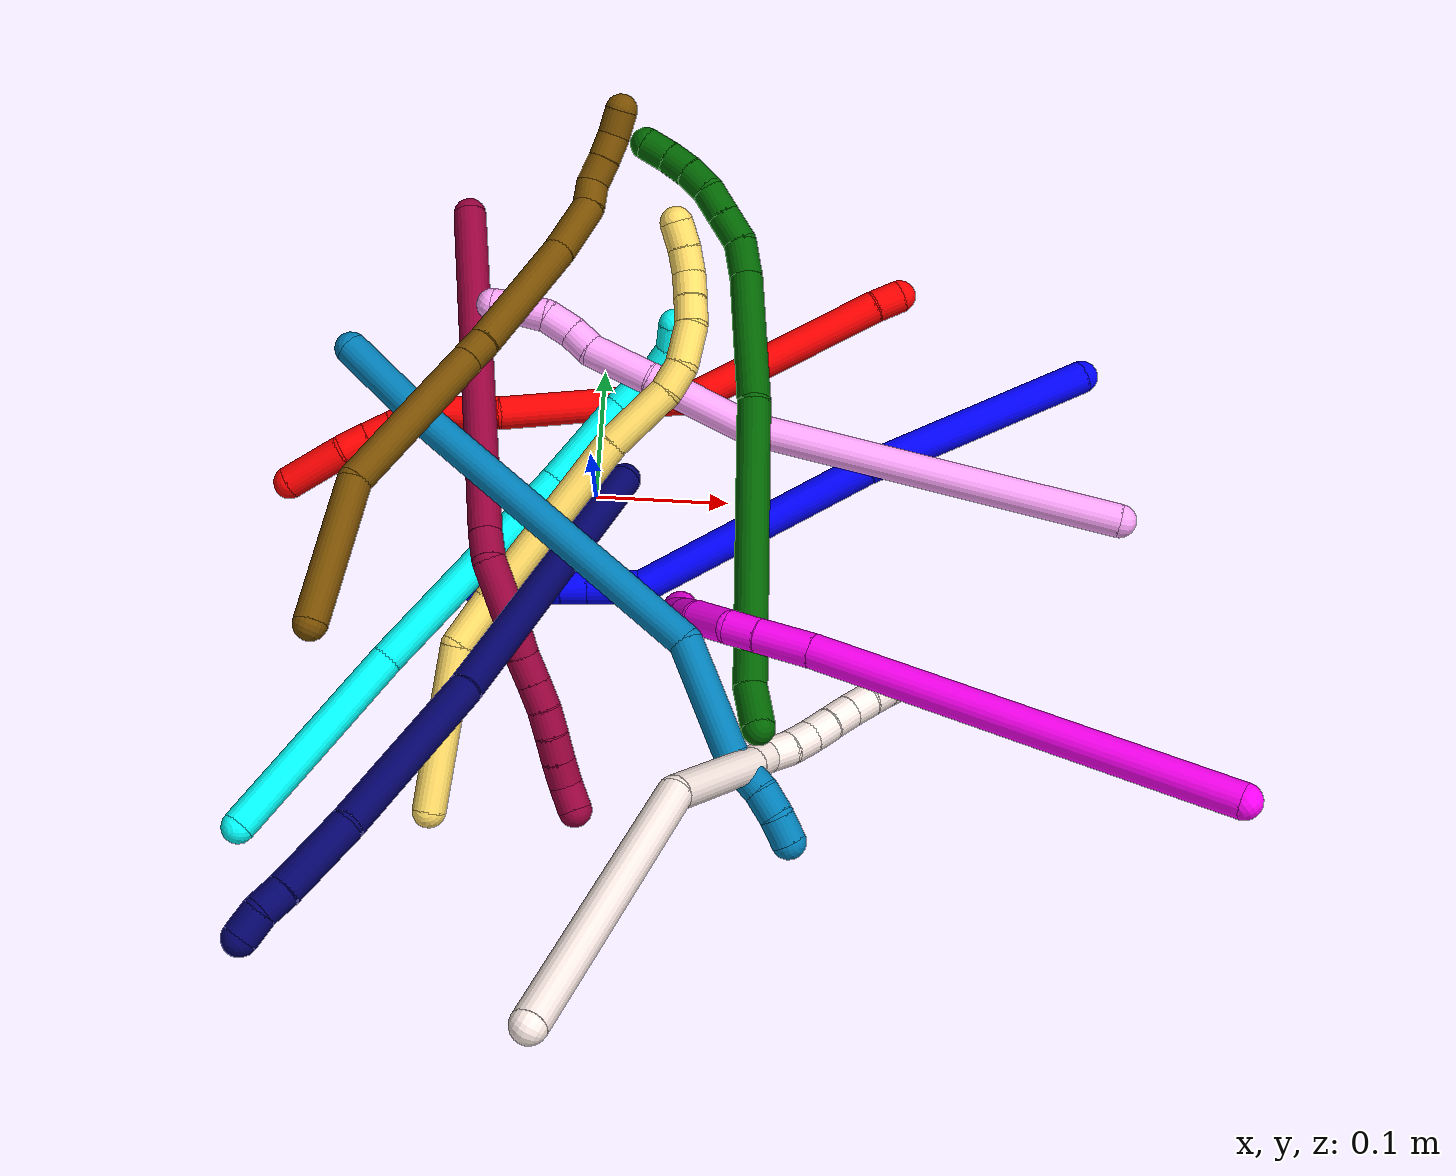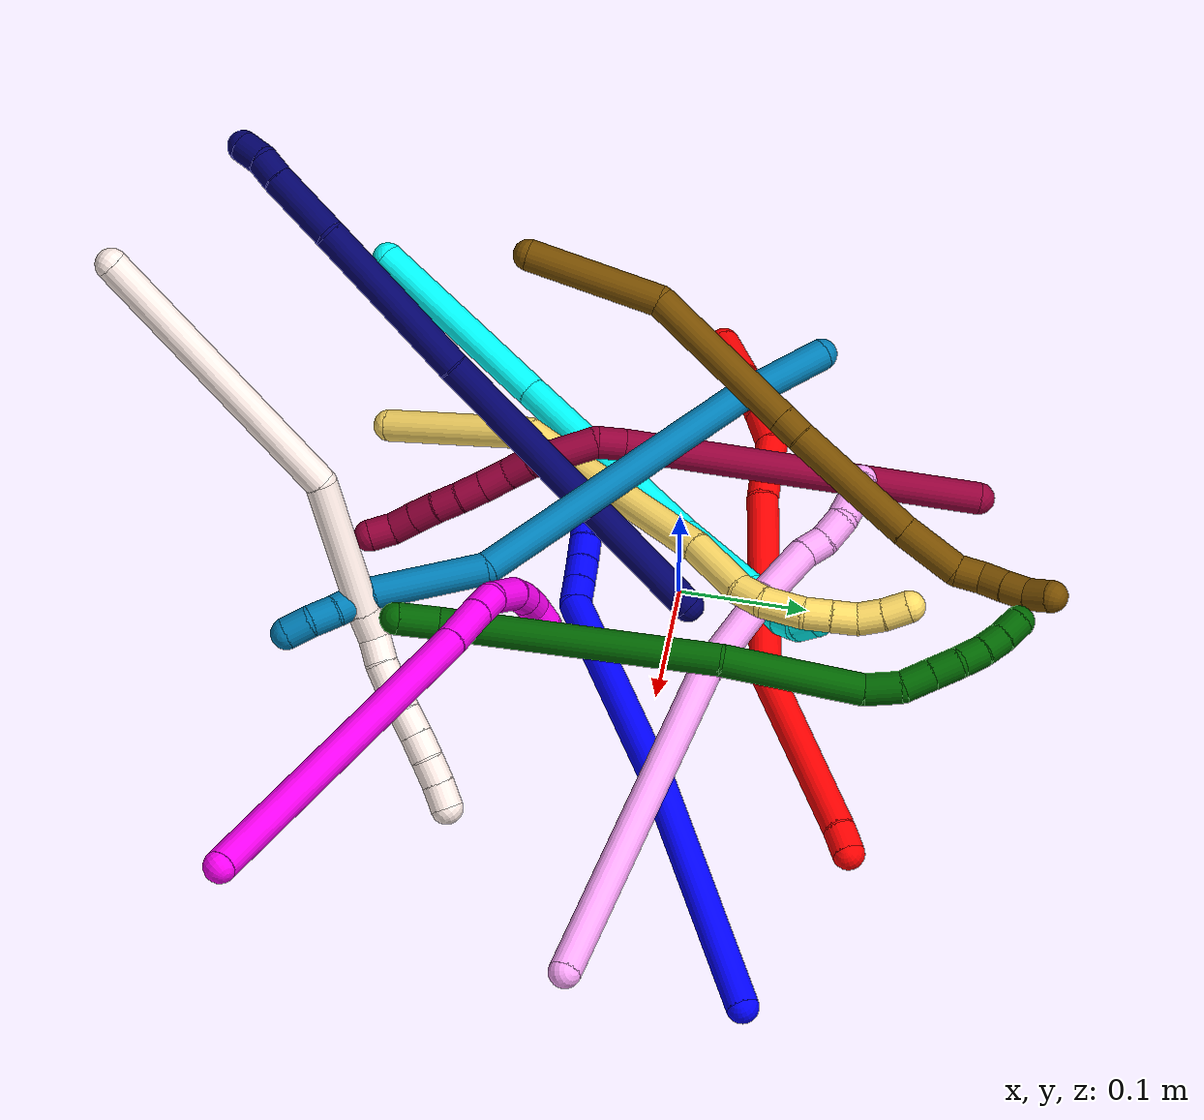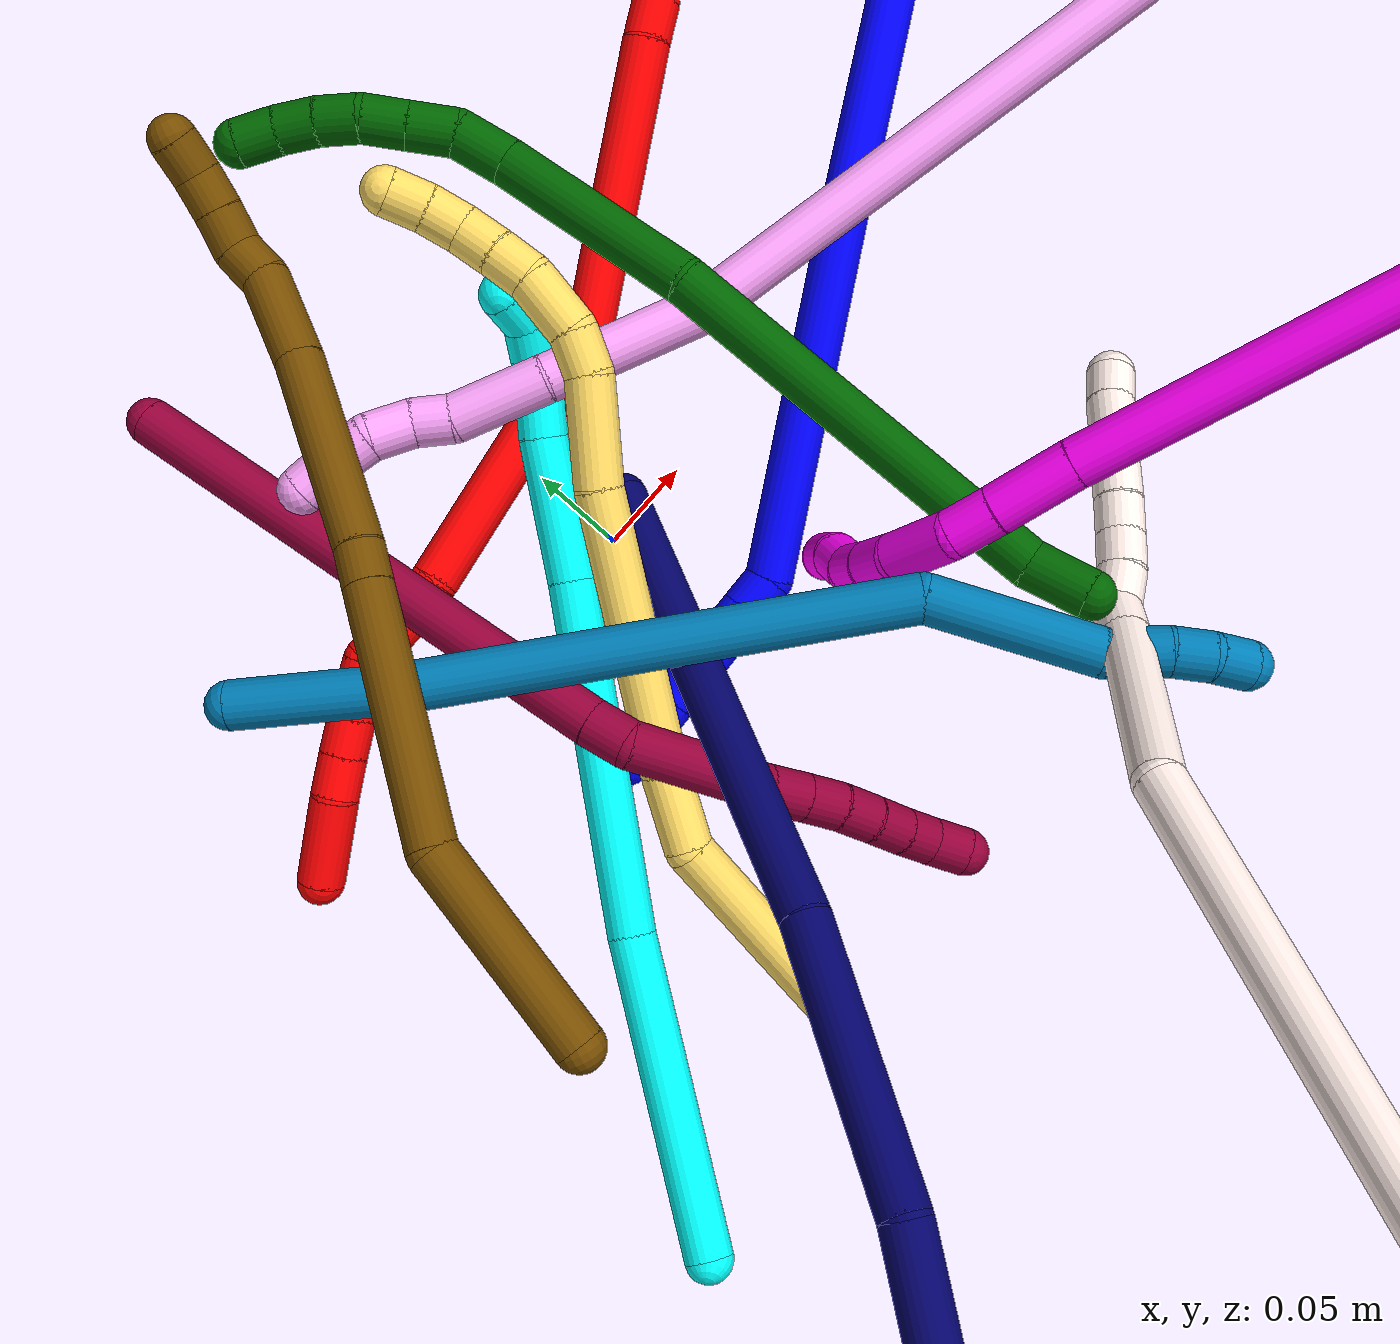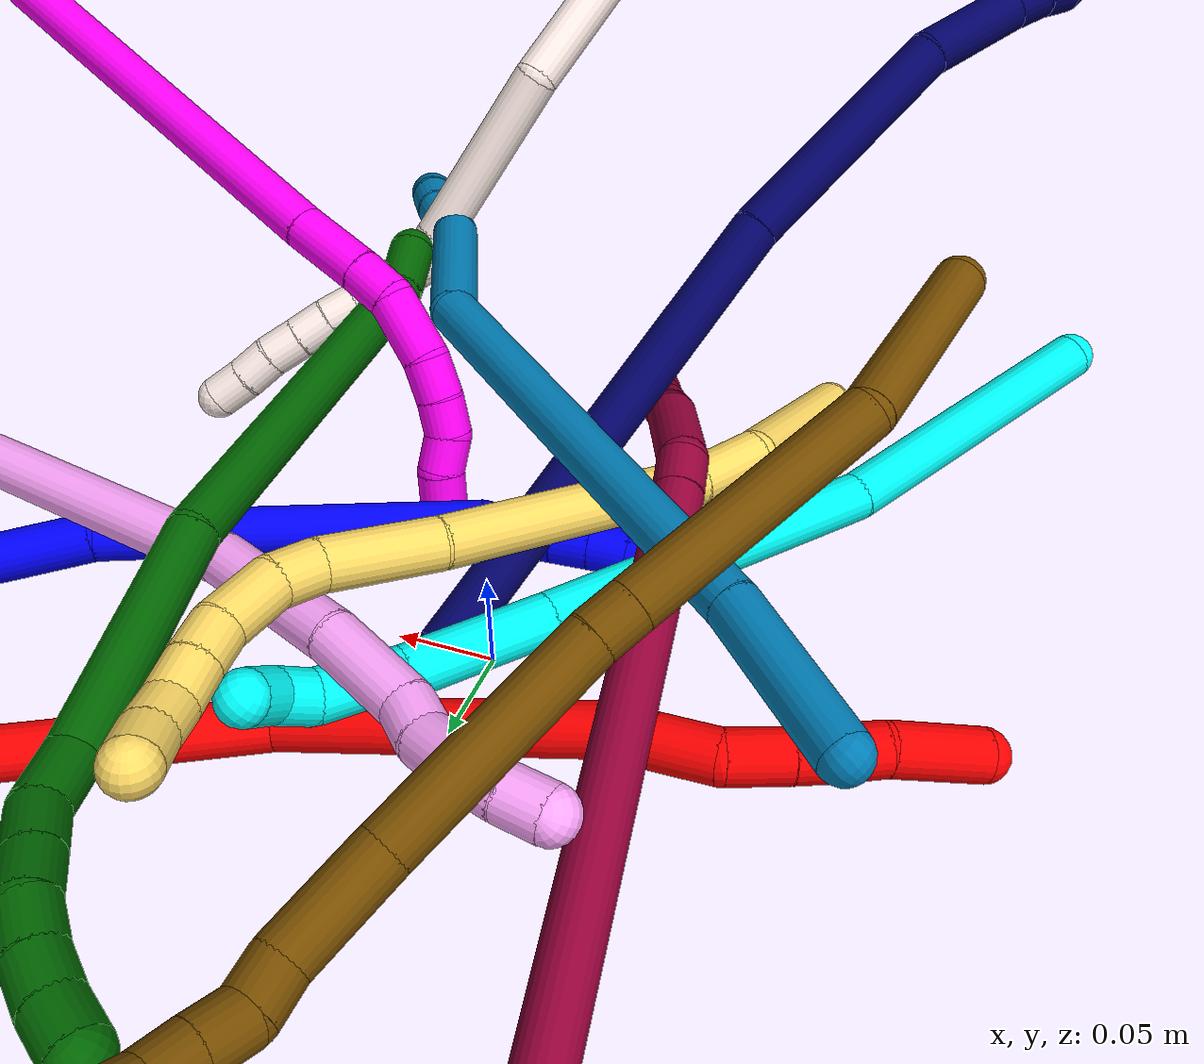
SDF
<sdf version="1.7">
 <world name="default">
  <plugin name="TubeGeneratorPlugin" filename="libtube_generator_plugin.so"/>
  <model name="photoneo_s_sensor">
   <static>1</static>
   <pose>0 0 2 1.57079 1.57079 3.14159</pose>
   <link name="link">
    <inertial><mass>0.1</mass></inertial>
    <sensor name="sensor" type="depth">
     <update_rate>30</update_rate>
     <camera>
      <horizontal_fov>1.22</horizontal_fov>
      <image><width>1920</width><height>1200</height><format>B8G8R8</format></image>
      <clip><near>0.1</near><far>4</far></clip>
      <depth_camera><output>points</output></depth_camera>
     </camera>
     <plugin name="camera_plugin" filename="libgazebo_ros_depth_camera.so">
      <baseline>0.2</baseline>
      <alwaysOn>1</alwaysOn>
      <updateRate>0.0</updateRate>
      <cameraName>camera_ir</cameraName>
      <imageTopicName>/camera/color/image_raw</imageTopicName>
      <cameraInfoTopicName>/camera/color/camera_info</cameraInfoTopicName>
      <depthImageTopicName>/camera/depth/image_raw</depthImageTopicName>
      <depthImageCameraInfoTopicName>/camera/depth/camera_info</depthImageCameraInfoTopicName>
      <pointCloudTopicName>/camera/depth/points</pointCloudTopicName>
      <frameName>fr_optical</frameName>
      <pointCloudCutoff>0.1</pointCloudCutoff>
      <pointCloudCutoffMax>2.0</pointCloudCutoffMax>
      <distortionK1>0</distortionK1>
      <distortionK2>0</distortionK2>
      <distortionK3>0</distortionK3>
      <distortionT1>0</distortionT1>
      <distortionT2>0</distortionT2>
      <CxPrime>0</CxPrime>
      <Cx>0</Cx>
      <Cy>0</Cy>
      <focalLength>0</focalLength>
      <hackBaseline>0</hackBaseline>
     </plugin>
    </sensor>
   </link>
  </model>
  <gravity>0 0 -9.8</gravity>
  <magnetic_field>6e-06 2.3e-05 -4.2e-05</magnetic_field>
  <atmosphere type="adiabatic"/>
  <physics name="default_physics" default="0" type="ode">
   <max_step_size>0.003</max_step_size>
   <real_time_factor>1</real_time_factor>
   <real_time_update_rate>1000</real_time_update_rate>
   <max_contacts>10000</max_contacts>
   <ode>
    <solver>
     <type>quick</type>
     <iters>100</iters>
     <sor>1.3</sor>
     <use_dynamic_moi_rescaling>0</use_dynamic_moi_rescaling>
    </solver>
    <constraints>
     <contact_max_correcting_vel>0</contact_max_correcting_vel>
     <contact_surface_layer>0.001</contact_surface_layer>
     <cfm>0</cfm>
     <erp>0.2</erp>
    </constraints>
   </ode>
  </physics>
  <scene><ambient>0.4 0.4 0.4 1</ambient><background>0.7 0.7 0.7 1</background><shadows>0</shadows></scene>
  <audio><device>default</device></audio>
  <spherical_coordinates>
   <surface_model>EARTH_WGS84</surface_model>
   <latitude_deg>0</latitude_deg>
   <longitude_deg>0</longitude_deg>
   <elevation>0</elevation>
   <heading_deg>0</heading_deg>
  </spherical_coordinates>
  <model name="bin">
   <static>1</static>
   <link name="bottom">
    <collision name="collision-bottom">
     <pose>0 0 -0.01 0 -0 0</pose>
     <geometry><box><size>0.8 0.6 0.02</size></box></geometry>
     <surface>
      <friction><ode><mu>100</mu><mu2>100</mu2></ode></friction>
      <contact><collide_bitmask>65535</collide_bitmask></contact>
     </surface>
    </collision>
   </link>
   <link name="west_wall">
    <collision name="collision-west_wall">
     <pose>-0.41 0 0.1 0 -0 0</pose>
     <geometry><box><size>0.02 0.6 0.2</size></box></geometry>
     <surface>
      <friction><ode><mu>100</mu><mu2>100</mu2></ode></friction>
      <contact><collide_bitmask>65535</collide_bitmask></contact>
     </surface>
    </collision>
   </link>
   <link name="east_wall">
    <collision name="collision-east_wall">
     <pose>0.41 0 0.1 0 -0 0</pose>
     <geometry><box><size>0.02 0.6 0.2</size></box></geometry>
     <surface>
      <friction><ode><mu>100</mu><mu2>100</mu2></ode></friction>
      <contact><collide_bitmask>65535</collide_bitmask></contact>
     </surface>
    </collision>
   </link>
   <link name="south_wall">
    <collision name="collision-south_wall">
     <pose>0 -0.31 0.1 0 -0 0</pose>
     <geometry><box><size>0.8 0.02 0.2</size></box></geometry>
     <surface>
      <friction><ode><mu>100</mu><mu2>100</mu2></ode></friction>
      <contact><collide_bitmask>65535</collide_bitmask></contact>
     </surface>
    </collision>
   </link>
   <link name="north_wall">
    <collision name="collision-north_wall">
     <pose>0 0.31 0.1 0 -0 0</pose>
     <geometry><box><size>0.8 0.02 0.2</size></box></geometry>
     <surface>
      <friction><ode><mu>100</mu><mu2>100</mu2></ode></friction>
      <contact><collide_bitmask>65535</collide_bitmask></contact>
     </surface>
    </collision>
   </link>
  </model>
  <model name="1">
   <static>0</static>
   <link name="1">
    <collision name="collision-cylinder-e_1_1_4">
     <pose>-0.08236 -0.040824 0.022036 1.07584 -1.05781 -0.67101</pose>
     <geometry><cylinder><radius>0.0125</radius><length>0.189054</length></cylinder></geometry>
     <surface>
      <friction><ode><mu>1.16</mu><mu2>1.16</mu2><slip1>0</slip1><slip2>0</slip2></ode></friction>
      <contact><ode><kp>1e+06</kp><kd>1</kd><max_vel>0</max_vel><min_depth>0.001</min_depth></ode></contact>
     </surface>
    </collision>
    <visual name="visual-cylinder-e_1_1_4">
     <pose>-0.08236 -0.040824 0.022036 1.07584 -1.05781 -0.67101</pose>
     <geometry><cylinder><radius>0.0125</radius><length>0.189054</length></cylinder></geometry>
     <material><ambient>0 0 1 1</ambient></material>
    </visual>
    <collision name="collision-cylinder-e_2_4_5">
     <pose>-0.246485 -0.130541 0.042995 1.5928 -1.03177 -1.05076</pose>
     <geometry><cylinder><radius>0.0125</radius><length>0.190548</length></cylinder></geometry>
     <surface>
      <friction><ode><mu>1.16</mu><mu2>1.16</mu2><slip1>0</slip1><slip2>0</slip2></ode></friction>
      <contact><ode><kp>1e+06</kp><kd>1</kd><max_vel>0</max_vel><min_depth>0.001</min_depth></ode></contact>
     </surface>
    </collision>
    <visual name="visual-cylinder-e_2_4_5">
     <pose>-0.246485 -0.130541 0.042995 1.5928 -1.03177 -1.05076</pose>
     <geometry><cylinder><radius>0.0125</radius><length>0.190548</length></cylinder></geometry>
     <material><ambient>0 0 1 1</ambient></material>
    </visual>
    <collision name="collision-cylinder-e_3_5_6">
     <pose>-0.338211 -0.179946 0.041197 2.52395 -1.48214 -2.47065</pose>
     <geometry><cylinder><radius>0.0125</radius><length>0.02</length></cylinder></geometry>
     <surface>
      <friction><ode><mu>1.16</mu><mu2>1.16</mu2><slip1>0</slip1><slip2>0</slip2></ode></friction>
      <contact><ode><kp>1e+06</kp><kd>1</kd><max_vel>0</max_vel><min_depth>0.001</min_depth></ode></contact>
     </surface>
    </collision>
    <visual name="visual-cylinder-e_3_5_6">
     <pose>-0.338211 -0.179946 0.041197 2.52395 -1.48214 -2.47065</pose>
     <geometry><cylinder><radius>0.0125</radius><length>0.02</length></cylinder></geometry>
     <material><ambient>0 0 1 1</ambient></material>
    </visual>
    <collision name="collision-cylinder-e_4_6_7">
     <pose>-0.358248 -0.181055 0.040085 2.15082 -1.50027 -2.09065</pose>
     <geometry><cylinder><radius>0.0125</radius><length>0.020202</length></cylinder></geometry>
     <surface>
      <friction><ode><mu>1.16</mu><mu2>1.16</mu2><slip1>0</slip1><slip2>0</slip2></ode></friction>
      <contact><ode><kp>1e+06</kp><kd>1</kd><max_vel>0</max_vel><min_depth>0.001</min_depth></ode></contact>
     </surface>
    </collision>
    <visual name="visual-cylinder-e_4_6_7">
     <pose>-0.358248 -0.181055 0.040085 2.15082 -1.50027 -2.09065</pose>
     <geometry><cylinder><radius>0.0125</radius><length>0.020202</length></cylinder></geometry>
     <material><ambient>0 0 1 1</ambient></material>
    </visual>
    <collision name="collision-cylinder-e_5_7_8">
     <pose>-0.378349 -0.182355 0.039443 1.91376 -1.49627 -1.84268</pose>
     <geometry><cylinder><radius>0.0125</radius><length>0.020106</length></cylinder></geometry>
     <surface>
      <friction><ode><mu>1.16</mu><mu2>1.16</mu2><slip1>0</slip1><slip2>0</slip2></ode></friction>
      <contact><ode><kp>1e+06</kp><kd>1</kd><max_vel>0</max_vel><min_depth>0.001</min_depth></ode></contact>
     </surface>
    </collision>
    <visual name="visual-cylinder-e_5_7_8">
     <pose>-0.378349 -0.182355 0.039443 1.91376 -1.49627 -1.84268</pose>
     <geometry><cylinder><radius>0.0125</radius><length>0.020106</length></cylinder></geometry>
     <material><ambient>0 0 1 1</ambient></material>
    </visual>
    <collision name="collision-cylinder-e_6_8_9">
     <pose>-0.398369 -0.183689 0.03863 2.29944 -1.48655 -2.23475</pose>
     <geometry><cylinder><radius>0.0125</radius><length>0.02006</length></cylinder></geometry>
     <surface>
      <friction><ode><mu>1.16</mu><mu2>1.16</mu2><slip1>0</slip1><slip2>0</slip2></ode></friction>
      <contact><ode><kp>1e+06</kp><kd>1</kd><max_vel>0</max_vel><min_depth>0.001</min_depth></ode></contact>
     </surface>
    </collision>
    <visual name="visual-cylinder-e_6_8_9">
     <pose>-0.398369 -0.183689 0.03863 2.29944 -1.48655 -2.23475</pose>
     <geometry><cylinder><radius>0.0125</radius><length>0.02006</length></cylinder></geometry>
     <material><ambient>0 0 1 1</ambient></material>
    </visual>
    <collision name="collision-cylinder-e_7_9_10">
     <pose>-0.418336 -0.184914 0.037489 2.34265 -1.48773 -2.28133</pose>
     <geometry><cylinder><radius>0.0125</radius><length>0.020014</length></cylinder></geometry>
     <surface>
      <friction><ode><mu>1.16</mu><mu2>1.16</mu2><slip1>0</slip1><slip2>0</slip2></ode></friction>
      <contact><ode><kp>1e+06</kp><kd>1</kd><max_vel>0</max_vel><min_depth>0.001</min_depth></ode></contact>
     </surface>
    </collision>
    <visual name="visual-cylinder-e_7_9_10">
     <pose>-0.418336 -0.184914 0.037489 2.34265 -1.48773 -2.28133</pose>
     <geometry><cylinder><radius>0.0125</radius><length>0.020014</length></cylinder></geometry>
     <material><ambient>0 0 1 1</ambient></material>
    </visual>
    <collision name="collision-cylinder-e_8_10_2">
     <pose>-0.438087 -0.187073 0.035467 2.31589 -1.35662 -2.14585</pose>
     <geometry><cylinder><radius>0.0125</radius><length>0.020015</length></cylinder></geometry>
     <surface>
      <friction><ode><mu>1.16</mu><mu2>1.16</mu2><slip1>0</slip1><slip2>0</slip2></ode></friction>
      <contact><ode><kp>1e+06</kp><kd>1</kd><max_vel>0</max_vel><min_depth>0.001</min_depth></ode></contact>
     </surface>
    </collision>
    <visual name="visual-cylinder-e_8_10_2">
     <pose>-0.438087 -0.187073 0.035467 2.31589 -1.35662 -2.14585</pose>
     <geometry><cylinder><radius>0.0125</radius><length>0.020015</length></cylinder></geometry>
     <material><ambient>0 0 1 1</ambient></material>
    </visual>
    <collision name="collision-sphere-2">
     <pose>-0.447866 -0.188636 0.034025 0 -0 0</pose>
     <geometry><sphere><radius>0.0125</radius></sphere></geometry>
     <surface>
      <friction><ode><mu>1.16</mu><mu2>1.16</mu2><slip1>0</slip1><slip2>0</slip2></ode></friction>
      <contact><ode><kp>1e+06</kp><kd>1</kd><max_vel>0</max_vel><min_depth>0.001</min_depth></ode></contact>
     </surface>
    </collision>
    <visual name="visual-sphere-2">
     <pose>-0.447866 -0.188636 0.034025 0 -0 0</pose>
     <geometry><sphere><radius>0.0125</radius></sphere></geometry>
     <material><ambient>0 0 1 1</ambient></material>
    </visual>
    <collision name="collision-sphere-10">
     <pose>-0.428308 -0.185509 0.03691 0 -0 0</pose>
     <geometry><sphere><radius>0.0125</radius></sphere></geometry>
     <surface>
      <friction><ode><mu>1.16</mu><mu2>1.16</mu2><slip1>0</slip1><slip2>0</slip2></ode></friction>
      <contact><ode><kp>1e+06</kp><kd>1</kd><max_vel>0</max_vel><min_depth>0.001</min_depth></ode></contact>
     </surface>
    </collision>
    <visual name="visual-sphere-10">
     <pose>-0.428308 -0.185509 0.03691 0 -0 0</pose>
     <geometry><sphere><radius>0.0125</radius></sphere></geometry>
     <material><ambient>0 0 1 1</ambient></material>
    </visual>
    <collision name="collision-sphere-9">
     <pose>-0.408363 -0.184319 0.038068 0 -0 0</pose>
     <geometry><sphere><radius>0.0125</radius></sphere></geometry>
     <surface>
      <friction><ode><mu>1.16</mu><mu2>1.16</mu2><slip1>0</slip1><slip2>0</slip2></ode></friction>
      <contact><ode><kp>1e+06</kp><kd>1</kd><max_vel>0</max_vel><min_depth>0.001</min_depth></ode></contact>
     </surface>
    </collision>
    <visual name="visual-sphere-9">
     <pose>-0.408363 -0.184319 0.038068 0 -0 0</pose>
     <geometry><sphere><radius>0.0125</radius></sphere></geometry>
     <material><ambient>0 0 1 1</ambient></material>
    </visual>
    <collision name="collision-sphere-4">
     <pose>-0.16472 -0.081649 0.044071 0 -0 0</pose>
     <geometry><sphere><radius>0.0125</radius></sphere></geometry>
     <surface>
      <friction><ode><mu>1.16</mu><mu2>1.16</mu2><slip1>0</slip1><slip2>0</slip2></ode></friction>
      <contact><ode><kp>1e+06</kp><kd>1</kd><max_vel>0</max_vel><min_depth>0.001</min_depth></ode></contact>
     </surface>
    </collision>
    <visual name="visual-sphere-4">
     <pose>-0.16472 -0.081649 0.044071 0 -0 0</pose>
     <geometry><sphere><radius>0.0125</radius></sphere></geometry>
     <material><ambient>0 0 1 1</ambient></material>
    </visual>
    <collision name="collision-sphere-1">
     <geometry><sphere><radius>0.0125</radius></sphere></geometry>
     <surface>
      <friction><ode><mu>1.16</mu><mu2>1.16</mu2><slip1>0</slip1><slip2>0</slip2></ode></friction>
      <contact><ode><kp>1e+06</kp><kd>1</kd><max_vel>0</max_vel><min_depth>0.001</min_depth></ode></contact>
     </surface>
    </collision>
    <visual name="visual-sphere-1">
     <geometry><sphere><radius>0.0125</radius></sphere></geometry>
     <material><ambient>0 0 1 1</ambient></material>
    </visual>
    <collision name="collision-sphere-8">
     <pose>-0.388375 -0.18306 0.039192 0 -0 0</pose>
     <geometry><sphere><radius>0.0125</radius></sphere></geometry>
     <surface>
      <friction><ode><mu>1.16</mu><mu2>1.16</mu2><slip1>0</slip1><slip2>0</slip2></ode></friction>
      <contact><ode><kp>1e+06</kp><kd>1</kd><max_vel>0</max_vel><min_depth>0.001</min_depth></ode></contact>
     </surface>
    </collision>
    <visual name="visual-sphere-8">
     <pose>-0.388375 -0.18306 0.039192 0 -0 0</pose>
     <geometry><sphere><radius>0.0125</radius></sphere></geometry>
     <material><ambient>0 0 1 1</ambient></material>
    </visual>
    <collision name="collision-sphere-5">
     <pose>-0.32825 -0.179434 0.041919 0 -0 0</pose>
     <geometry><sphere><radius>0.0125</radius></sphere></geometry>
     <surface>
      <friction><ode><mu>1.16</mu><mu2>1.16</mu2><slip1>0</slip1><slip2>0</slip2></ode></friction>
      <contact><ode><kp>1e+06</kp><kd>1</kd><max_vel>0</max_vel><min_depth>0.001</min_depth></ode></contact>
     </surface>
    </collision>
    <visual name="visual-sphere-5">
     <pose>-0.32825 -0.179434 0.041919 0 -0 0</pose>
     <geometry><sphere><radius>0.0125</radius></sphere></geometry>
     <material><ambient>0 0 1 1</ambient></material>
    </visual>
    <collision name="collision-sphere-6">
     <pose>-0.348172 -0.180459 0.040475 0 -0 0</pose>
     <geometry><sphere><radius>0.0125</radius></sphere></geometry>
     <surface>
      <friction><ode><mu>1.16</mu><mu2>1.16</mu2><slip1>0</slip1><slip2>0</slip2></ode></friction>
      <contact><ode><kp>1e+06</kp><kd>1</kd><max_vel>0</max_vel><min_depth>0.001</min_depth></ode></contact>
     </surface>
    </collision>
    <visual name="visual-sphere-6">
     <pose>-0.348172 -0.180459 0.040475 0 -0 0</pose>
     <geometry><sphere><radius>0.0125</radius></sphere></geometry>
     <material><ambient>0 0 1 1</ambient></material>
    </visual>
    <collision name="collision-sphere-7">
     <pose>-0.368324 -0.18165 0.039695 0 -0 0</pose>
     <geometry><sphere><radius>0.0125</radius></sphere></geometry>
     <surface>
      <friction><ode><mu>1.16</mu><mu2>1.16</mu2><slip1>0</slip1><slip2>0</slip2></ode></friction>
      <contact><ode><kp>1e+06</kp><kd>1</kd><max_vel>0</max_vel><min_depth>0.001</min_depth></ode></contact>
     </surface>
    </collision>
    <visual name="visual-sphere-7">
     <pose>-0.368324 -0.18165 0.039695 0 -0 0</pose>
     <geometry><sphere><radius>0.0125</radius></sphere></geometry>
     <material><ambient>0 0 1 1</ambient></material>
    </visual>
    <inertial>
     <pose>-0.218558 -0.109291 0.034041 0 -0 0</pose>
     <mass>0.5</mass>
     <inertia>
      <ixx>-0.000102</ixx>
      <ixy>0</ixy>
      <ixz>0</ixz>
      <iyy>0.000472</iyy>
      <iyz>0</iyz>
      <izz>0.001556</izz>
     </inertia>
    </inertial>
   </link>
   <pose>0.365273 0.112607 0.011497 0.26449 0.036742 0.008762</pose>
  </model>
  <model name="2">
   <static>0</static>
   <link name="2">
    <collision name="collision-cylinder-e_1_1_4">
     <pose>-0.009713 -0.004741 -0.000447 1.66475 -1.11497 -1.20112</pose>
     <geometry><cylinder><radius>0.0125</radius><length>0.021635</length></cylinder></geometry>
     <surface>
      <friction><ode><mu>1.16</mu><mu2>1.16</mu2><slip1>0</slip1><slip2>0</slip2></ode></friction>
      <contact><ode><kp>1e+06</kp><kd>1</kd><max_vel>0</max_vel><min_depth>0.001</min_depth></ode></contact>
     </surface>
    </collision>
    <visual name="visual-cylinder-e_1_1_4">
     <pose>-0.009713 -0.004741 -0.000447 1.66475 -1.11497 -1.20112</pose>
     <geometry><cylinder><radius>0.0125</radius><length>0.021635</length></cylinder></geometry>
     <material><ambient>1 0 0 1</ambient></material>
    </visual>
    <collision name="collision-cylinder-e_2_4_5">
     <pose>-0.086082 -0.048306 -0.012602 1.86369 -1.02425 -1.29553</pose>
     <geometry><cylinder><radius>0.0125</radius><length>0.156045</length></cylinder></geometry>
     <surface>
      <friction><ode><mu>1.16</mu><mu2>1.16</mu2><slip1>0</slip1><slip2>0</slip2></ode></friction>
      <contact><ode><kp>1e+06</kp><kd>1</kd><max_vel>0</max_vel><min_depth>0.001</min_depth></ode></contact>
     </surface>
    </collision>
    <visual name="visual-cylinder-e_2_4_5">
     <pose>-0.086082 -0.048306 -0.012602 1.86369 -1.02425 -1.29553</pose>
     <geometry><cylinder><radius>0.0125</radius><length>0.156045</length></cylinder></geometry>
     <material><ambient>1 0 0 1</ambient></material>
    </visual>
    <collision name="collision-cylinder-e_3_5_6">
     <pose>-0.226538 -0.09763 -0.031081 2.14354 -1.4031 -1.99581</pose>
     <geometry><cylinder><radius>0.0125</radius><length>0.149699</length></cylinder></geometry>
     <surface>
      <friction><ode><mu>1.16</mu><mu2>1.16</mu2><slip1>0</slip1><slip2>0</slip2></ode></friction>
      <contact><ode><kp>1e+06</kp><kd>1</kd><max_vel>0</max_vel><min_depth>0.001</min_depth></ode></contact>
     </surface>
    </collision>
    <visual name="visual-cylinder-e_3_5_6">
     <pose>-0.226538 -0.09763 -0.031081 2.14354 -1.4031 -1.99581</pose>
     <geometry><cylinder><radius>0.0125</radius><length>0.149699</length></cylinder></geometry>
     <material><ambient>1 0 0 1</ambient></material>
    </visual>
    <collision name="collision-cylinder-e_4_6_7">
     <pose>-0.311511 -0.108681 -0.040679 2.94893 -1.31842 -2.89345</pose>
     <geometry><cylinder><radius>0.0125</radius><length>0.023079</length></cylinder></geometry>
     <surface>
      <friction><ode><mu>1.16</mu><mu2>1.16</mu2><slip1>0</slip1><slip2>0</slip2></ode></friction>
      <contact><ode><kp>1e+06</kp><kd>1</kd><max_vel>0</max_vel><min_depth>0.001</min_depth></ode></contact>
     </surface>
    </collision>
    <visual name="visual-cylinder-e_4_6_7">
     <pose>-0.311511 -0.108681 -0.040679 2.94893 -1.31842 -2.89345</pose>
     <geometry><cylinder><radius>0.0125</radius><length>0.023079</length></cylinder></geometry>
     <material><ambient>1 0 0 1</ambient></material>
    </visual>
    <collision name="collision-cylinder-e_5_7_8">
     <pose>-0.337176 -0.109286 -0.047207 3.1273 -1.32084 -3.12319</pose>
     <geometry><cylinder><radius>0.0125</radius><length>0.029911</length></cylinder></geometry>
     <surface>
      <friction><ode><mu>1.16</mu><mu2>1.16</mu2><slip1>0</slip1><slip2>0</slip2></ode></friction>
      <contact><ode><kp>1e+06</kp><kd>1</kd><max_vel>0</max_vel><min_depth>0.001</min_depth></ode></contact>
     </surface>
    </collision>
    <visual name="visual-cylinder-e_5_7_8">
     <pose>-0.337176 -0.109286 -0.047207 3.1273 -1.32084 -3.12319</pose>
     <geometry><cylinder><radius>0.0125</radius><length>0.029911</length></cylinder></geometry>
     <material><ambient>1 0 0 1</ambient></material>
    </visual>
    <collision name="collision-cylinder-e_6_8_9">
     <pose>-0.364691 -0.115896 -0.054297 2.04808 -1.05512 -1.52715</pose>
     <geometry><cylinder><radius>0.0125</radius><length>0.02994</length></cylinder></geometry>
     <surface>
      <friction><ode><mu>1.16</mu><mu2>1.16</mu2><slip1>0</slip1><slip2>0</slip2></ode></friction>
      <contact><ode><kp>1e+06</kp><kd>1</kd><max_vel>0</max_vel><min_depth>0.001</min_depth></ode></contact>
     </surface>
    </collision>
    <visual name="visual-cylinder-e_6_8_9">
     <pose>-0.364691 -0.115896 -0.054297 2.04808 -1.05512 -1.52715</pose>
     <geometry><cylinder><radius>0.0125</radius><length>0.02994</length></cylinder></geometry>
     <material><ambient>1 0 0 1</ambient></material>
    </visual>
    <collision name="collision-cylinder-e_7_9_10">
     <pose>-0.386388 -0.127222 -0.059774 1.98311 -1.03029 -1.4269</pose>
     <geometry><cylinder><radius>0.0125</radius><length>0.020233</length></cylinder></geometry>
     <surface>
      <friction><ode><mu>1.16</mu><mu2>1.16</mu2><slip1>0</slip1><slip2>0</slip2></ode></friction>
      <contact><ode><kp>1e+06</kp><kd>1</kd><max_vel>0</max_vel><min_depth>0.001</min_depth></ode></contact>
     </surface>
    </collision>
    <visual name="visual-cylinder-e_7_9_10">
     <pose>-0.386388 -0.127222 -0.059774 1.98311 -1.03029 -1.4269</pose>
     <geometry><cylinder><radius>0.0125</radius><length>0.020233</length></cylinder></geometry>
     <material><ambient>1 0 0 1</ambient></material>
    </visual>
    <collision name="collision-cylinder-e_8_10_11">
     <pose>-0.404475 -0.13743 -0.063784 1.91091 -1.02091 -1.33985</pose>
     <geometry><cylinder><radius>0.0125</radius><length>0.022078</length></cylinder></geometry>
     <surface>
      <friction><ode><mu>1.16</mu><mu2>1.16</mu2><slip1>0</slip1><slip2>0</slip2></ode></friction>
      <contact><ode><kp>1e+06</kp><kd>1</kd><max_vel>0</max_vel><min_depth>0.001</min_depth></ode></contact>
     </surface>
    </collision>
    <visual name="visual-cylinder-e_8_10_11">
     <pose>-0.404475 -0.13743 -0.063784 1.91091 -1.02091 -1.33985</pose>
     <geometry><cylinder><radius>0.0125</radius><length>0.022078</length></cylinder></geometry>
     <material><ambient>1 0 0 1</ambient></material>
    </visual>
    <collision name="collision-cylinder-e_9_11_2">
     <pose>-0.432081 -0.155357 -0.074324 2.17466 -0.875757 -1.45648</pose>
     <geometry><cylinder><radius>0.0125</radius><length>0.04738</length></cylinder></geometry>
     <surface>
      <friction><ode><mu>1.16</mu><mu2>1.16</mu2><slip1>0</slip1><slip2>0</slip2></ode></friction>
      <contact><ode><kp>1e+06</kp><kd>1</kd><max_vel>0</max_vel><min_depth>0.001</min_depth></ode></contact>
     </surface>
    </collision>
    <visual name="visual-cylinder-e_9_11_2">
     <pose>-0.432081 -0.155357 -0.074324 2.17466 -0.875757 -1.45648</pose>
     <geometry><cylinder><radius>0.0125</radius><length>0.04738</length></cylinder></geometry>
     <material><ambient>1 0 0 1</ambient></material>
    </visual>
    <collision name="collision-sphere-2">
     <pose>-0.450275 -0.167845 -0.082938 0 -0 0</pose>
     <geometry><sphere><radius>0.0125</radius></sphere></geometry>
     <surface>
      <friction><ode><mu>1.16</mu><mu2>1.16</mu2><slip1>0</slip1><slip2>0</slip2></ode></friction>
      <contact><ode><kp>1e+06</kp><kd>1</kd><max_vel>0</max_vel><min_depth>0.001</min_depth></ode></contact>
     </surface>
    </collision>
    <visual name="visual-sphere-2">
     <pose>-0.450275 -0.167845 -0.082938 0 -0 0</pose>
     <geometry><sphere><radius>0.0125</radius></sphere></geometry>
     <material><ambient>1 0 0 1</ambient></material>
    </visual>
    <collision name="collision-sphere-11">
     <pose>-0.413886 -0.142868 -0.065709 0 -0 0</pose>
     <geometry><sphere><radius>0.0125</radius></sphere></geometry>
     <surface>
      <friction><ode><mu>1.16</mu><mu2>1.16</mu2><slip1>0</slip1><slip2>0</slip2></ode></friction>
      <contact><ode><kp>1e+06</kp><kd>1</kd><max_vel>0</max_vel><min_depth>0.001</min_depth></ode></contact>
     </surface>
    </collision>
    <visual name="visual-sphere-11">
     <pose>-0.413886 -0.142868 -0.065709 0 -0 0</pose>
     <geometry><sphere><radius>0.0125</radius></sphere></geometry>
     <material><ambient>1 0 0 1</ambient></material>
    </visual>
    <collision name="collision-sphere-10">
     <pose>-0.395063 -0.131991 -0.06186 0 -0 0</pose>
     <geometry><sphere><radius>0.0125</radius></sphere></geometry>
     <surface>
      <friction><ode><mu>1.16</mu><mu2>1.16</mu2><slip1>0</slip1><slip2>0</slip2></ode></friction>
      <contact><ode><kp>1e+06</kp><kd>1</kd><max_vel>0</max_vel><min_depth>0.001</min_depth></ode></contact>
     </surface>
    </collision>
    <visual name="visual-sphere-10">
     <pose>-0.395063 -0.131991 -0.06186 0 -0 0</pose>
     <geometry><sphere><radius>0.0125</radius></sphere></geometry>
     <material><ambient>1 0 0 1</ambient></material>
    </visual>
    <collision name="collision-sphere-9">
     <pose>-0.377714 -0.122453 -0.057688 0 -0 0</pose>
     <geometry><sphere><radius>0.0125</radius></sphere></geometry>
     <surface>
      <friction><ode><mu>1.16</mu><mu2>1.16</mu2><slip1>0</slip1><slip2>0</slip2></ode></friction>
      <contact><ode><kp>1e+06</kp><kd>1</kd><max_vel>0</max_vel><min_depth>0.001</min_depth></ode></contact>
     </surface>
    </collision>
    <visual name="visual-sphere-9">
     <pose>-0.377714 -0.122453 -0.057688 0 -0 0</pose>
     <geometry><sphere><radius>0.0125</radius></sphere></geometry>
     <material><ambient>1 0 0 1</ambient></material>
    </visual>
    <collision name="collision-sphere-4">
     <pose>-0.019426 -0.009482 -0.000894 0 -0 0</pose>
     <geometry><sphere><radius>0.0125</radius></sphere></geometry>
     <surface>
      <friction><ode><mu>1.16</mu><mu2>1.16</mu2><slip1>0</slip1><slip2>0</slip2></ode></friction>
      <contact><ode><kp>1e+06</kp><kd>1</kd><max_vel>0</max_vel><min_depth>0.001</min_depth></ode></contact>
     </surface>
    </collision>
    <visual name="visual-sphere-4">
     <pose>-0.019426 -0.009482 -0.000894 0 -0 0</pose>
     <geometry><sphere><radius>0.0125</radius></sphere></geometry>
     <material><ambient>1 0 0 1</ambient></material>
    </visual>
    <collision name="collision-sphere-1">
     <geometry><sphere><radius>0.0125</radius></sphere></geometry>
     <surface>
      <friction><ode><mu>1.16</mu><mu2>1.16</mu2><slip1>0</slip1><slip2>0</slip2></ode></friction>
      <contact><ode><kp>1e+06</kp><kd>1</kd><max_vel>0</max_vel><min_depth>0.001</min_depth></ode></contact>
     </surface>
    </collision>
    <visual name="visual-sphere-1">
     <geometry><sphere><radius>0.0125</radius></sphere></geometry>
     <material><ambient>1 0 0 1</ambient></material>
    </visual>
    <collision name="collision-sphere-8">
     <pose>-0.351667 -0.109339 -0.050906 0 -0 0</pose>
     <geometry><sphere><radius>0.0125</radius></sphere></geometry>
     <surface>
      <friction><ode><mu>1.16</mu><mu2>1.16</mu2><slip1>0</slip1><slip2>0</slip2></ode></friction>
      <contact><ode><kp>1e+06</kp><kd>1</kd><max_vel>0</max_vel><min_depth>0.001</min_depth></ode></contact>
     </surface>
    </collision>
    <visual name="visual-sphere-8">
     <pose>-0.351667 -0.109339 -0.050906 0 -0 0</pose>
     <geometry><sphere><radius>0.0125</radius></sphere></geometry>
     <material><ambient>1 0 0 1</ambient></material>
    </visual>
    <collision name="collision-sphere-5">
     <pose>-0.152738 -0.087131 -0.02431 0 -0 0</pose>
     <geometry><sphere><radius>0.0125</radius></sphere></geometry>
     <surface>
      <friction><ode><mu>1.16</mu><mu2>1.16</mu2><slip1>0</slip1><slip2>0</slip2></ode></friction>
      <contact><ode><kp>1e+06</kp><kd>1</kd><max_vel>0</max_vel><min_depth>0.001</min_depth></ode></contact>
     </surface>
    </collision>
    <visual name="visual-sphere-5">
     <pose>-0.152738 -0.087131 -0.02431 0 -0 0</pose>
     <geometry><sphere><radius>0.0125</radius></sphere></geometry>
     <material><ambient>1 0 0 1</ambient></material>
    </visual>
    <collision name="collision-sphere-6">
     <pose>-0.300338 -0.108129 -0.037851 0 -0 0</pose>
     <geometry><sphere><radius>0.0125</radius></sphere></geometry>
     <surface>
      <friction><ode><mu>1.16</mu><mu2>1.16</mu2><slip1>0</slip1><slip2>0</slip2></ode></friction>
      <contact><ode><kp>1e+06</kp><kd>1</kd><max_vel>0</max_vel><min_depth>0.001</min_depth></ode></contact>
     </surface>
    </collision>
    <visual name="visual-sphere-6">
     <pose>-0.300338 -0.108129 -0.037851 0 -0 0</pose>
     <geometry><sphere><radius>0.0125</radius></sphere></geometry>
     <material><ambient>1 0 0 1</ambient></material>
    </visual>
    <collision name="collision-sphere-7">
     <pose>-0.322685 -0.109233 -0.043507 0 -0 0</pose>
     <geometry><sphere><radius>0.0125</radius></sphere></geometry>
     <surface>
      <friction><ode><mu>1.16</mu><mu2>1.16</mu2><slip1>0</slip1><slip2>0</slip2></ode></friction>
      <contact><ode><kp>1e+06</kp><kd>1</kd><max_vel>0</max_vel><min_depth>0.001</min_depth></ode></contact>
     </surface>
    </collision>
    <visual name="visual-sphere-7">
     <pose>-0.322685 -0.109233 -0.043507 0 -0 0</pose>
     <geometry><sphere><radius>0.0125</radius></sphere></geometry>
     <material><ambient>1 0 0 1</ambient></material>
    </visual>
    <inertial>
     <pose>-0.225937 -0.088943 -0.033489 0 -0 0</pose>
     <mass>0.5</mass>
     <inertia>
      <ixx>-0.000225</ixx>
      <ixy>0</ixy>
      <ixz>0</ixz>
      <iyy>0.000297</iyy>
      <iyz>0</iyz>
      <izz>0.000781</izz>
     </inertia>
    </inertial>
   </link>
   <pose>0.223218 0.168714 0.017846 0.263502 0.255459 0.072366</pose>
  </model>
  <model name="3">
   <static>0</static>
   <link name="3">
    <collision name="collision-cylinder-e_1_1_4">
     <pose>0.021062 0.045059 -0.064751 -2.53364 0.260905 -0.792243</pose>
     <geometry><cylinder><radius>0.0125</radius><length>0.163298</length></cylinder></geometry>
     <surface>
      <friction><ode><mu>1.16</mu><mu2>1.16</mu2><slip1>0</slip1><slip2>0</slip2></ode></friction>
      <contact><ode><kp>1e+06</kp><kd>1</kd><max_vel>0</max_vel><min_depth>0.001</min_depth></ode></contact>
     </surface>
    </collision>
    <visual name="visual-cylinder-e_1_1_4">
     <pose>0.021062 0.045059 -0.064751 -2.53364 0.260905 -0.792243</pose>
     <geometry><cylinder><radius>0.0125</radius><length>0.163298</length></cylinder></geometry>
     <material><ambient>0.003922 1 0.996078 1</ambient></material>
    </visual>
    <collision name="collision-cylinder-e_2_4_5">
     <pose>0.081304 0.141392 -0.19421 -2.4715 0.443092 -1.14843</pose>
     <geometry><cylinder><radius>0.0125</radius><length>0.182772</length></cylinder></geometry>
     <surface>
      <friction><ode><mu>1.16</mu><mu2>1.16</mu2><slip1>0</slip1><slip2>0</slip2></ode></friction>
      <contact><ode><kp>1e+06</kp><kd>1</kd><max_vel>0</max_vel><min_depth>0.001</min_depth></ode></contact>
     </surface>
    </collision>
    <visual name="visual-cylinder-e_2_4_5">
     <pose>0.081304 0.141392 -0.19421 -2.4715 0.443092 -1.14843</pose>
     <geometry><cylinder><radius>0.0125</radius><length>0.182772</length></cylinder></geometry>
     <material><ambient>0.003922 1 0.996078 1</ambient></material>
    </visual>
    <collision name="collision-cylinder-e_3_5_6">
     <pose>0.136883 0.214837 -0.283464 -2.40701 0.460293 -1.09397</pose>
     <geometry><cylinder><radius>0.0125</radius><length>0.073834</length></cylinder></geometry>
     <surface>
      <friction><ode><mu>1.16</mu><mu2>1.16</mu2><slip1>0</slip1><slip2>0</slip2></ode></friction>
      <contact><ode><kp>1e+06</kp><kd>1</kd><max_vel>0</max_vel><min_depth>0.001</min_depth></ode></contact>
     </surface>
    </collision>
    <visual name="visual-cylinder-e_3_5_6">
     <pose>0.136883 0.214837 -0.283464 -2.40701 0.460293 -1.09397</pose>
     <geometry><cylinder><radius>0.0125</radius><length>0.073834</length></cylinder></geometry>
     <material><ambient>0.003922 1 0.996078 1</ambient></material>
    </visual>
    <collision name="collision-cylinder-e_4_6_7">
     <pose>0.158918 0.242409 -0.31432 -2.43356 0.596106 -1.38696</pose>
     <geometry><cylinder><radius>0.0125</radius><length>0.020077</length></cylinder></geometry>
     <surface>
      <friction><ode><mu>1.16</mu><mu2>1.16</mu2><slip1>0</slip1><slip2>0</slip2></ode></friction>
      <contact><ode><kp>1e+06</kp><kd>1</kd><max_vel>0</max_vel><min_depth>0.001</min_depth></ode></contact>
     </surface>
    </collision>
    <visual name="visual-cylinder-e_4_6_7">
     <pose>0.158918 0.242409 -0.31432 -2.43356 0.596106 -1.38696</pose>
     <geometry><cylinder><radius>0.0125</radius><length>0.020077</length></cylinder></geometry>
     <material><ambient>0.003922 1 0.996078 1</ambient></material>
    </visual>
    <collision name="collision-cylinder-e_5_7_8">
     <pose>0.169442 0.253102 -0.327569 -2.49011 0.510624 -1.31579</pose>
     <geometry><cylinder><radius>0.0125</radius><length>0.020004</length></cylinder></geometry>
     <surface>
      <friction><ode><mu>1.16</mu><mu2>1.16</mu2><slip1>0</slip1><slip2>0</slip2></ode></friction>
      <contact><ode><kp>1e+06</kp><kd>1</kd><max_vel>0</max_vel><min_depth>0.001</min_depth></ode></contact>
     </surface>
    </collision>
    <visual name="visual-cylinder-e_5_7_8">
     <pose>0.169442 0.253102 -0.327569 -2.49011 0.510624 -1.31579</pose>
     <geometry><cylinder><radius>0.0125</radius><length>0.020004</length></cylinder></geometry>
     <material><ambient>0.003922 1 0.996078 1</ambient></material>
    </visual>
    <collision name="collision-cylinder-e_6_8_9">
     <pose>0.18132 0.265051 -0.33714 -1.9473 0.773395 -1.07916</pose>
     <geometry><cylinder><radius>0.0125</radius><length>0.020012</length></cylinder></geometry>
     <surface>
      <friction><ode><mu>1.16</mu><mu2>1.16</mu2><slip1>0</slip1><slip2>0</slip2></ode></friction>
      <contact><ode><kp>1e+06</kp><kd>1</kd><max_vel>0</max_vel><min_depth>0.001</min_depth></ode></contact>
     </surface>
    </collision>
    <visual name="visual-cylinder-e_6_8_9">
     <pose>0.18132 0.265051 -0.33714 -1.9473 0.773395 -1.07916</pose>
     <geometry><cylinder><radius>0.0125</radius><length>0.020012</length></cylinder></geometry>
     <material><ambient>0.003922 1 0.996078 1</ambient></material>
    </visual>
    <collision name="collision-cylinder-e_7_9_2">
     <pose>0.192648 0.280705 -0.339237 -1.51139 0.448702 -0.423597</pose>
     <geometry><cylinder><radius>0.0125</radius><length>0.020003</length></cylinder></geometry>
     <surface>
      <friction><ode><mu>1.16</mu><mu2>1.16</mu2><slip1>0</slip1><slip2>0</slip2></ode></friction>
      <contact><ode><kp>1e+06</kp><kd>1</kd><max_vel>0</max_vel><min_depth>0.001</min_depth></ode></contact>
     </surface>
    </collision>
    <visual name="visual-cylinder-e_7_9_2">
     <pose>0.192648 0.280705 -0.339237 -1.51139 0.448702 -0.423597</pose>
     <geometry><cylinder><radius>0.0125</radius><length>0.020003</length></cylinder></geometry>
     <material><ambient>0.003922 1 0.996078 1</ambient></material>
    </visual>
    <collision name="collision-sphere-2">
     <pose>0.196987 0.289701 -0.338702 0 -0 0</pose>
     <geometry><sphere><radius>0.0125</radius></sphere></geometry>
     <surface>
      <friction><ode><mu>1.16</mu><mu2>1.16</mu2><slip1>0</slip1><slip2>0</slip2></ode></friction>
      <contact><ode><kp>1e+06</kp><kd>1</kd><max_vel>0</max_vel><min_depth>0.001</min_depth></ode></contact>
     </surface>
    </collision>
    <visual name="visual-sphere-2">
     <pose>0.196987 0.289701 -0.338702 0 -0 0</pose>
     <geometry><sphere><radius>0.0125</radius></sphere></geometry>
     <material><ambient>0.003922 1 0.996078 1</ambient></material>
    </visual>
    <collision name="collision-sphere-9">
     <pose>0.18831 0.271709 -0.339772 0 -0 0</pose>
     <geometry><sphere><radius>0.0125</radius></sphere></geometry>
     <surface>
      <friction><ode><mu>1.16</mu><mu2>1.16</mu2><slip1>0</slip1><slip2>0</slip2></ode></friction>
      <contact><ode><kp>1e+06</kp><kd>1</kd><max_vel>0</max_vel><min_depth>0.001</min_depth></ode></contact>
     </surface>
    </collision>
    <visual name="visual-sphere-9">
     <pose>0.18831 0.271709 -0.339772 0 -0 0</pose>
     <geometry><sphere><radius>0.0125</radius></sphere></geometry>
     <material><ambient>0.003922 1 0.996078 1</ambient></material>
    </visual>
    <collision name="collision-sphere-4">
     <pose>0.042124 0.090117 -0.129502 0 -0 0</pose>
     <geometry><sphere><radius>0.0125</radius></sphere></geometry>
     <surface>
      <friction><ode><mu>1.16</mu><mu2>1.16</mu2><slip1>0</slip1><slip2>0</slip2></ode></friction>
      <contact><ode><kp>1e+06</kp><kd>1</kd><max_vel>0</max_vel><min_depth>0.001</min_depth></ode></contact>
     </surface>
    </collision>
    <visual name="visual-sphere-4">
     <pose>0.042124 0.090117 -0.129502 0 -0 0</pose>
     <geometry><sphere><radius>0.0125</radius></sphere></geometry>
     <material><ambient>0.003922 1 0.996078 1</ambient></material>
    </visual>
    <collision name="collision-sphere-1">
     <geometry><sphere><radius>0.0125</radius></sphere></geometry>
     <surface>
      <friction><ode><mu>1.16</mu><mu2>1.16</mu2><slip1>0</slip1><slip2>0</slip2></ode></friction>
      <contact><ode><kp>1e+06</kp><kd>1</kd><max_vel>0</max_vel><min_depth>0.001</min_depth></ode></contact>
     </surface>
    </collision>
    <visual name="visual-sphere-1">
     <geometry><sphere><radius>0.0125</radius></sphere></geometry>
     <material><ambient>0.003922 1 0.996078 1</ambient></material>
    </visual>
    <collision name="collision-sphere-8">
     <pose>0.17433 0.258393 -0.334508 0 -0 0</pose>
     <geometry><sphere><radius>0.0125</radius></sphere></geometry>
     <surface>
      <friction><ode><mu>1.16</mu><mu2>1.16</mu2><slip1>0</slip1><slip2>0</slip2></ode></friction>
      <contact><ode><kp>1e+06</kp><kd>1</kd><max_vel>0</max_vel><min_depth>0.001</min_depth></ode></contact>
     </surface>
    </collision>
    <visual name="visual-sphere-8">
     <pose>0.17433 0.258393 -0.334508 0 -0 0</pose>
     <geometry><sphere><radius>0.0125</radius></sphere></geometry>
     <material><ambient>0.003922 1 0.996078 1</ambient></material>
    </visual>
    <collision name="collision-sphere-5">
     <pose>0.120484 0.192668 -0.258919 0 -0 0</pose>
     <geometry><sphere><radius>0.0125</radius></sphere></geometry>
     <surface>
      <friction><ode><mu>1.16</mu><mu2>1.16</mu2><slip1>0</slip1><slip2>0</slip2></ode></friction>
      <contact><ode><kp>1e+06</kp><kd>1</kd><max_vel>0</max_vel><min_depth>0.001</min_depth></ode></contact>
     </surface>
    </collision>
    <visual name="visual-sphere-5">
     <pose>0.120484 0.192668 -0.258919 0 -0 0</pose>
     <geometry><sphere><radius>0.0125</radius></sphere></geometry>
     <material><ambient>0.003922 1 0.996078 1</ambient></material>
    </visual>
    <collision name="collision-sphere-6">
     <pose>0.153282 0.237006 -0.308009 0 -0 0</pose>
     <geometry><sphere><radius>0.0125</radius></sphere></geometry>
     <surface>
      <friction><ode><mu>1.16</mu><mu2>1.16</mu2><slip1>0</slip1><slip2>0</slip2></ode></friction>
      <contact><ode><kp>1e+06</kp><kd>1</kd><max_vel>0</max_vel><min_depth>0.001</min_depth></ode></contact>
     </surface>
    </collision>
    <visual name="visual-sphere-6">
     <pose>0.153282 0.237006 -0.308009 0 -0 0</pose>
     <geometry><sphere><radius>0.0125</radius></sphere></geometry>
     <material><ambient>0.003922 1 0.996078 1</ambient></material>
    </visual>
    <collision name="collision-sphere-7">
     <pose>0.164554 0.247811 -0.32063 0 -0 0</pose>
     <geometry><sphere><radius>0.0125</radius></sphere></geometry>
     <surface>
      <friction><ode><mu>1.16</mu><mu2>1.16</mu2><slip1>0</slip1><slip2>0</slip2></ode></friction>
      <contact><ode><kp>1e+06</kp><kd>1</kd><max_vel>0</max_vel><min_depth>0.001</min_depth></ode></contact>
     </surface>
    </collision>
    <visual name="visual-sphere-7">
     <pose>0.164554 0.247811 -0.32063 0 -0 0</pose>
     <geometry><sphere><radius>0.0125</radius></sphere></geometry>
     <material><ambient>0.003922 1 0.996078 1</ambient></material>
    </visual>
    <inertial>
     <pose>0.084937 0.139824 -0.18679 0 -0 0</pose>
     <mass>0.5</mass>
     <inertia>
      <ixx>-0.000238</ixx>
      <ixy>0</ixy>
      <ixz>0</ixz>
      <iyy>-0.000905</iyy>
      <iyz>0</iyz>
      <izz>-0.000881</izz>
     </inertia>
    </inertial>
   </link>
   <pose>-0.234533 -0.276831 0.055589 0.495612 -0.734322 -0.0856</pose>
  </model>
  <model name="4">
   <static>0</static>
   <link name="4">
    <collision name="collision-cylinder-e_1_1_4">
     <pose>-0.13087 0.04819 0.017667 -1.21939 -1.19704 0.889064</pose>
     <geometry><cylinder><radius>0.0125</radius><length>0.28115</length></cylinder></geometry>
     <surface>
      <friction><ode><mu>1.16</mu><mu2>1.16</mu2><slip1>0</slip1><slip2>0</slip2></ode></friction>
      <contact><ode><kp>1e+06</kp><kd>1</kd><max_vel>0</max_vel><min_depth>0.001</min_depth></ode></contact>
     </surface>
    </collision>
    <visual name="visual-cylinder-e_1_1_4">
     <pose>-0.13087 0.04819 0.017667 -1.21939 -1.19704 0.889064</pose>
     <geometry><cylinder><radius>0.0125</radius><length>0.28115</length></cylinder></geometry>
     <material><ambient>1 0.65098 0.996078 1</ambient></material>
    </visual>
    <collision name="collision-cylinder-e_2_4_5">
     <pose>-0.30213 0.10589 0.032926 -1.8189 -1.3325 1.5809</pose>
     <geometry><cylinder><radius>0.0125</radius><length>0.083129</length></cylinder></geometry>
     <surface>
      <friction><ode><mu>1.16</mu><mu2>1.16</mu2><slip1>0</slip1><slip2>0</slip2></ode></friction>
      <contact><ode><kp>1e+06</kp><kd>1</kd><max_vel>0</max_vel><min_depth>0.001</min_depth></ode></contact>
     </surface>
    </collision>
    <visual name="visual-cylinder-e_2_4_5">
     <pose>-0.30213 0.10589 0.032926 -1.8189 -1.3325 1.5809</pose>
     <geometry><cylinder><radius>0.0125</radius><length>0.083129</length></cylinder></geometry>
     <material><ambient>1 0.65098 0.996078 1</ambient></material>
    </visual>
    <collision name="collision-cylinder-e_3_5_6">
     <pose>-0.367354 0.118041 0.031172 -1.32722 -1.4617 1.22271</pose>
     <geometry><cylinder><radius>0.0125</radius><length>0.049965</length></cylinder></geometry>
     <surface>
      <friction><ode><mu>1.16</mu><mu2>1.16</mu2><slip1>0</slip1><slip2>0</slip2></ode></friction>
      <contact><ode><kp>1e+06</kp><kd>1</kd><max_vel>0</max_vel><min_depth>0.001</min_depth></ode></contact>
     </surface>
    </collision>
    <visual name="visual-cylinder-e_3_5_6">
     <pose>-0.367354 0.118041 0.031172 -1.32722 -1.4617 1.22271</pose>
     <geometry><cylinder><radius>0.0125</radius><length>0.049965</length></cylinder></geometry>
     <material><ambient>1 0.65098 0.996078 1</ambient></material>
    </visual>
    <collision name="collision-cylinder-e_4_6_7">
     <pose>-0.402101 0.119942 0.029686 2.80943 -1.34607 -2.7271</pose>
     <geometry><cylinder><radius>0.0125</radius><length>0.020337</length></cylinder></geometry>
     <surface>
      <friction><ode><mu>1.16</mu><mu2>1.16</mu2><slip1>0</slip1><slip2>0</slip2></ode></friction>
      <contact><ode><kp>1e+06</kp><kd>1</kd><max_vel>0</max_vel><min_depth>0.001</min_depth></ode></contact>
     </surface>
    </collision>
    <visual name="visual-cylinder-e_4_6_7">
     <pose>-0.402101 0.119942 0.029686 2.80943 -1.34607 -2.7271</pose>
     <geometry><cylinder><radius>0.0125</radius><length>0.020337</length></cylinder></geometry>
     <material><ambient>1 0.65098 0.996078 1</ambient></material>
    </visual>
    <collision name="collision-cylinder-e_5_7_8">
     <pose>-0.42303 0.121934 0.025383 -2.24012 -1.26459 1.97404</pose>
     <geometry><cylinder><radius>0.0125</radius><length>0.023108</length></cylinder></geometry>
     <surface>
      <friction><ode><mu>1.16</mu><mu2>1.16</mu2><slip1>0</slip1><slip2>0</slip2></ode></friction>
      <contact><ode><kp>1e+06</kp><kd>1</kd><max_vel>0</max_vel><min_depth>0.001</min_depth></ode></contact>
     </surface>
    </collision>
    <visual name="visual-cylinder-e_5_7_8">
     <pose>-0.42303 0.121934 0.025383 -2.24012 -1.26459 1.97404</pose>
     <geometry><cylinder><radius>0.0125</radius><length>0.023108</length></cylinder></geometry>
     <material><ambient>1 0.65098 0.996078 1</ambient></material>
    </visual>
    <collision name="collision-cylinder-e_6_8_9">
     <pose>-0.444371 0.127372 0.025093 -0.96593 -1.26231 0.731996</pose>
     <geometry><cylinder><radius>0.0125</radius><length>0.021671</length></cylinder></geometry>
     <surface>
      <friction><ode><mu>1.16</mu><mu2>1.16</mu2><slip1>0</slip1><slip2>0</slip2></ode></friction>
      <contact><ode><kp>1e+06</kp><kd>1</kd><max_vel>0</max_vel><min_depth>0.001</min_depth></ode></contact>
     </surface>
    </collision>
    <visual name="visual-cylinder-e_6_8_9">
     <pose>-0.444371 0.127372 0.025093 -0.96593 -1.26231 0.731996</pose>
     <geometry><cylinder><radius>0.0125</radius><length>0.021671</length></cylinder></geometry>
     <material><ambient>1 0.65098 0.996078 1</ambient></material>
    </visual>
    <collision name="collision-cylinder-e_7_9_2">
     <pose>-0.464185 0.133436 0.029237 -0.97573 -1.167 0.673925</pose>
     <geometry><cylinder><radius>0.0125</radius><length>0.02064</length></cylinder></geometry>
     <surface>
      <friction><ode><mu>1.16</mu><mu2>1.16</mu2><slip1>0</slip1><slip2>0</slip2></ode></friction>
      <contact><ode><kp>1e+06</kp><kd>1</kd><max_vel>0</max_vel><min_depth>0.001</min_depth></ode></contact>
     </surface>
    </collision>
    <visual name="visual-cylinder-e_7_9_2">
     <pose>-0.464185 0.133436 0.029237 -0.97573 -1.167 0.673925</pose>
     <geometry><cylinder><radius>0.0125</radius><length>0.02064</length></cylinder></geometry>
     <material><ambient>1 0.65098 0.996078 1</ambient></material>
    </visual>
    <collision name="collision-sphere-2">
     <pose>-0.473675 0.136794 0.03151 0 -0 0</pose>
     <geometry><sphere><radius>0.0125</radius></sphere></geometry>
     <surface>
      <friction><ode><mu>1.16</mu><mu2>1.16</mu2><slip1>0</slip1><slip2>0</slip2></ode></friction>
      <contact><ode><kp>1e+06</kp><kd>1</kd><max_vel>0</max_vel><min_depth>0.001</min_depth></ode></contact>
     </surface>
    </collision>
    <visual name="visual-sphere-2">
     <pose>-0.473675 0.136794 0.03151 0 -0 0</pose>
     <geometry><sphere><radius>0.0125</radius></sphere></geometry>
     <material><ambient>1 0.65098 0.996078 1</ambient></material>
    </visual>
    <collision name="collision-sphere-9">
     <pose>-0.454695 0.130078 0.026964 0 -0 0</pose>
     <geometry><sphere><radius>0.0125</radius></sphere></geometry>
     <surface>
      <friction><ode><mu>1.16</mu><mu2>1.16</mu2><slip1>0</slip1><slip2>0</slip2></ode></friction>
      <contact><ode><kp>1e+06</kp><kd>1</kd><max_vel>0</max_vel><min_depth>0.001</min_depth></ode></contact>
     </surface>
    </collision>
    <visual name="visual-sphere-9">
     <pose>-0.454695 0.130078 0.026964 0 -0 0</pose>
     <geometry><sphere><radius>0.0125</radius></sphere></geometry>
     <material><ambient>1 0.65098 0.996078 1</ambient></material>
    </visual>
    <collision name="collision-sphere-4">
     <pose>-0.26174 0.09638 0.035335 0 -0 0</pose>
     <geometry><sphere><radius>0.0125</radius></sphere></geometry>
     <surface>
      <friction><ode><mu>1.16</mu><mu2>1.16</mu2><slip1>0</slip1><slip2>0</slip2></ode></friction>
      <contact><ode><kp>1e+06</kp><kd>1</kd><max_vel>0</max_vel><min_depth>0.001</min_depth></ode></contact>
     </surface>
    </collision>
    <visual name="visual-sphere-4">
     <pose>-0.26174 0.09638 0.035335 0 -0 0</pose>
     <geometry><sphere><radius>0.0125</radius></sphere></geometry>
     <material><ambient>1 0.65098 0.996078 1</ambient></material>
    </visual>
    <collision name="collision-sphere-1">
     <geometry><sphere><radius>0.0125</radius></sphere></geometry>
     <surface>
      <friction><ode><mu>1.16</mu><mu2>1.16</mu2><slip1>0</slip1><slip2>0</slip2></ode></friction>
      <contact><ode><kp>1e+06</kp><kd>1</kd><max_vel>0</max_vel><min_depth>0.001</min_depth></ode></contact>
     </surface>
    </collision>
    <visual name="visual-sphere-1">
     <geometry><sphere><radius>0.0125</radius></sphere></geometry>
     <material><ambient>1 0.65098 0.996078 1</ambient></material>
    </visual>
    <collision name="collision-sphere-8">
     <pose>-0.434046 0.124666 0.023222 0 -0 0</pose>
     <geometry><sphere><radius>0.0125</radius></sphere></geometry>
     <surface>
      <friction><ode><mu>1.16</mu><mu2>1.16</mu2><slip1>0</slip1><slip2>0</slip2></ode></friction>
      <contact><ode><kp>1e+06</kp><kd>1</kd><max_vel>0</max_vel><min_depth>0.001</min_depth></ode></contact>
     </surface>
    </collision>
    <visual name="visual-sphere-8">
     <pose>-0.434046 0.124666 0.023222 0 -0 0</pose>
     <geometry><sphere><radius>0.0125</radius></sphere></geometry>
     <material><ambient>1 0.65098 0.996078 1</ambient></material>
    </visual>
    <collision name="collision-sphere-5">
     <pose>-0.34252 0.115401 0.030516 0 -0 0</pose>
     <geometry><sphere><radius>0.0125</radius></sphere></geometry>
     <surface>
      <friction><ode><mu>1.16</mu><mu2>1.16</mu2><slip1>0</slip1><slip2>0</slip2></ode></friction>
      <contact><ode><kp>1e+06</kp><kd>1</kd><max_vel>0</max_vel><min_depth>0.001</min_depth></ode></contact>
     </surface>
    </collision>
    <visual name="visual-sphere-5">
     <pose>-0.34252 0.115401 0.030516 0 -0 0</pose>
     <geometry><sphere><radius>0.0125</radius></sphere></geometry>
     <material><ambient>1 0.65098 0.996078 1</ambient></material>
    </visual>
    <collision name="collision-sphere-6">
     <pose>-0.392188 0.120681 0.031828 0 -0 0</pose>
     <geometry><sphere><radius>0.0125</radius></sphere></geometry>
     <surface>
      <friction><ode><mu>1.16</mu><mu2>1.16</mu2><slip1>0</slip1><slip2>0</slip2></ode></friction>
      <contact><ode><kp>1e+06</kp><kd>1</kd><max_vel>0</max_vel><min_depth>0.001</min_depth></ode></contact>
     </surface>
    </collision>
    <visual name="visual-sphere-6">
     <pose>-0.392188 0.120681 0.031828 0 -0 0</pose>
     <geometry><sphere><radius>0.0125</radius></sphere></geometry>
     <material><ambient>1 0.65098 0.996078 1</ambient></material>
    </visual>
    <collision name="collision-sphere-7">
     <pose>-0.412013 0.119203 0.027544 0 -0 0</pose>
     <geometry><sphere><radius>0.0125</radius></sphere></geometry>
     <surface>
      <friction><ode><mu>1.16</mu><mu2>1.16</mu2><slip1>0</slip1><slip2>0</slip2></ode></friction>
      <contact><ode><kp>1e+06</kp><kd>1</kd><max_vel>0</max_vel><min_depth>0.001</min_depth></ode></contact>
     </surface>
    </collision>
    <visual name="visual-sphere-7">
     <pose>-0.412013 0.119203 0.027544 0 -0 0</pose>
     <geometry><sphere><radius>0.0125</radius></sphere></geometry>
     <material><ambient>1 0.65098 0.996078 1</ambient></material>
    </visual>
    <inertial>
     <pose>-0.234857 0.078041 0.023199 0 -0 0</pose>
     <mass>0.5</mass>
     <inertia>
      <ixx>0.000935</ixx>
      <ixy>0</ixy>
      <ixz>0</ixz>
      <iyy>0.002289</iyy>
      <iyz>0</iyz>
      <izz>0.001152</izz>
     </inertia>
    </inertial>
   </link>
   <pose>0.388514 -0.016619 0.060998 2.38194 -0.143204 -0.541617</pose>
  </model>
  <model name="5">
   <static>0</static>
   <link name="5">
    <collision name="collision-cylinder-e_1_1_4">
     <pose>0.051582 0.026971 -0.020256 -2.21497 0.991675 -1.6502</pose>
     <geometry><cylinder><radius>0.0125</radius><length>0.123263</length></cylinder></geometry>
     <surface>
      <friction><ode><mu>1.16</mu><mu2>1.16</mu2><slip1>0</slip1><slip2>0</slip2></ode></friction>
      <contact><ode><kp>1e+06</kp><kd>1</kd><max_vel>0</max_vel><min_depth>0.001</min_depth></ode></contact>
     </surface>
    </collision>
    <visual name="visual-cylinder-e_1_1_4">
     <pose>0.051582 0.026971 -0.020256 -2.21497 0.991675 -1.6502</pose>
     <geometry><cylinder><radius>0.0125</radius><length>0.123263</length></cylinder></geometry>
     <material><ambient>1 0.858824 0.4 1</ambient></material>
    </visual>
    <collision name="collision-cylinder-e_2_4_5">
     <pose>0.116227 0.069155 -0.04052 -1.57127 0.709479 -0.709786</pose>
     <geometry><cylinder><radius>0.0125</radius><length>0.040104</length></cylinder></geometry>
     <surface>
      <friction><ode><mu>1.16</mu><mu2>1.16</mu2><slip1>0</slip1><slip2>0</slip2></ode></friction>
      <contact><ode><kp>1e+06</kp><kd>1</kd><max_vel>0</max_vel><min_depth>0.001</min_depth></ode></contact>
     </surface>
    </collision>
    <visual name="visual-cylinder-e_2_4_5">
     <pose>0.116227 0.069155 -0.04052 -1.57127 0.709479 -0.709786</pose>
     <geometry><cylinder><radius>0.0125</radius><length>0.040104</length></cylinder></geometry>
     <material><ambient>1 0.858824 0.4 1</ambient></material>
    </visual>
    <collision name="collision-cylinder-e_3_5_6">
     <pose>0.170898 0.142988 -0.052031 -1.76459 0.608386 -0.728981</pose>
     <geometry><cylinder><radius>0.0125</radius><length>0.145602</length></cylinder></geometry>
     <surface>
      <friction><ode><mu>1.16</mu><mu2>1.16</mu2><slip1>0</slip1><slip2>0</slip2></ode></friction>
      <contact><ode><kp>1e+06</kp><kd>1</kd><max_vel>0</max_vel><min_depth>0.001</min_depth></ode></contact>
     </surface>
    </collision>
    <visual name="visual-cylinder-e_3_5_6">
     <pose>0.170898 0.142988 -0.052031 -1.76459 0.608386 -0.728981</pose>
     <geometry><cylinder><radius>0.0125</radius><length>0.145602</length></cylinder></geometry>
     <material><ambient>1 0.858824 0.4 1</ambient></material>
    </visual>
    <collision name="collision-cylinder-e_4_6_7">
     <pose>0.225113 0.2259 -0.066315 -1.6847 0.476025 -0.531056</pose>
     <geometry><cylinder><radius>0.0125</radius><length>0.055018</length></cylinder></geometry>
     <surface>
      <friction><ode><mu>1.16</mu><mu2>1.16</mu2><slip1>0</slip1><slip2>0</slip2></ode></friction>
      <contact><ode><kp>1e+06</kp><kd>1</kd><max_vel>0</max_vel><min_depth>0.001</min_depth></ode></contact>
     </surface>
    </collision>
    <visual name="visual-cylinder-e_4_6_7">
     <pose>0.225113 0.2259 -0.066315 -1.6847 0.476025 -0.531056</pose>
     <geometry><cylinder><radius>0.0125</radius><length>0.055018</length></cylinder></geometry>
     <material><ambient>1 0.858824 0.4 1</ambient></material>
    </visual>
    <collision name="collision-cylinder-e_5_7_8">
     <pose>0.245323 0.258341 -0.070453 -1.73597 0.743999 -0.863243</pose>
     <geometry><cylinder><radius>0.0125</radius><length>0.022456</length></cylinder></geometry>
     <surface>
      <friction><ode><mu>1.16</mu><mu2>1.16</mu2><slip1>0</slip1><slip2>0</slip2></ode></friction>
      <contact><ode><kp>1e+06</kp><kd>1</kd><max_vel>0</max_vel><min_depth>0.001</min_depth></ode></contact>
     </surface>
    </collision>
    <visual name="visual-cylinder-e_5_7_8">
     <pose>0.245323 0.258341 -0.070453 -1.73597 0.743999 -0.863243</pose>
     <geometry><cylinder><radius>0.0125</radius><length>0.022456</length></cylinder></geometry>
     <material><ambient>1 0.858824 0.4 1</ambient></material>
    </visual>
    <collision name="collision-cylinder-e_6_8_9">
     <pose>0.267235 0.273977 -0.072475 -1.65927 1.08708 -1.16705</pose>
     <geometry><cylinder><radius>0.0125</radius><length>0.032324</length></cylinder></geometry>
     <surface>
      <friction><ode><mu>1.16</mu><mu2>1.16</mu2><slip1>0</slip1><slip2>0</slip2></ode></friction>
      <contact><ode><kp>1e+06</kp><kd>1</kd><max_vel>0</max_vel><min_depth>0.001</min_depth></ode></contact>
     </surface>
    </collision>
    <visual name="visual-cylinder-e_6_8_9">
     <pose>0.267235 0.273977 -0.072475 -1.65927 1.08708 -1.16705</pose>
     <geometry><cylinder><radius>0.0125</radius><length>0.032324</length></cylinder></geometry>
     <material><ambient>1 0.858824 0.4 1</ambient></material>
    </visual>
    <collision name="collision-cylinder-e_7_9_10">
     <pose>0.291476 0.283787 -0.072955 -1.49166 1.34037 -1.26402</pose>
     <geometry><cylinder><radius>0.0125</radius><length>0.020407</length></cylinder></geometry>
     <surface>
      <friction><ode><mu>1.16</mu><mu2>1.16</mu2><slip1>0</slip1><slip2>0</slip2></ode></friction>
      <contact><ode><kp>1e+06</kp><kd>1</kd><max_vel>0</max_vel><min_depth>0.001</min_depth></ode></contact>
     </surface>
    </collision>
    <visual name="visual-cylinder-e_7_9_10">
     <pose>0.291476 0.283787 -0.072955 -1.49166 1.34037 -1.26402</pose>
     <geometry><cylinder><radius>0.0125</radius><length>0.020407</length></cylinder></geometry>
     <material><ambient>1 0.858824 0.4 1</ambient></material>
    </visual>
    <collision name="collision-cylinder-e_8_10_11">
     <pose>0.311459 0.288135 -0.072115 -1.25742 1.36211 -1.065</pose>
     <geometry><cylinder><radius>0.0125</radius><length>0.020544</length></cylinder></geometry>
     <surface>
      <friction><ode><mu>1.16</mu><mu2>1.16</mu2><slip1>0</slip1><slip2>0</slip2></ode></friction>
      <contact><ode><kp>1e+06</kp><kd>1</kd><max_vel>0</max_vel><min_depth>0.001</min_depth></ode></contact>
     </surface>
    </collision>
    <visual name="visual-cylinder-e_8_10_11">
     <pose>0.311459 0.288135 -0.072115 -1.25742 1.36211 -1.065</pose>
     <geometry><cylinder><radius>0.0125</radius><length>0.020544</length></cylinder></geometry>
     <material><ambient>1 0.858824 0.4 1</ambient></material>
    </visual>
    <collision name="collision-cylinder-e_9_11_12">
     <pose>0.331183 0.291193 -0.074091 -2.76738 1.28643 -2.64678</pose>
     <geometry><cylinder><radius>0.0125</radius><length>0.020158</length></cylinder></geometry>
     <surface>
      <friction><ode><mu>1.16</mu><mu2>1.16</mu2><slip1>0</slip1><slip2>0</slip2></ode></friction>
      <contact><ode><kp>1e+06</kp><kd>1</kd><max_vel>0</max_vel><min_depth>0.001</min_depth></ode></contact>
     </surface>
    </collision>
    <visual name="visual-cylinder-e_9_11_12">
     <pose>0.331183 0.291193 -0.074091 -2.76738 1.28643 -2.64678</pose>
     <geometry><cylinder><radius>0.0125</radius><length>0.020158</length></cylinder></geometry>
     <material><ambient>1 0.858824 0.4 1</ambient></material>
    </visual>
    <collision name="collision-cylinder-e_10_12_2">
     <pose>0.350328 0.292003 -0.080115 3.07571 1.22623 3.04799</pose>
     <geometry><cylinder><radius>0.0125</radius><length>0.020125</length></cylinder></geometry>
     <surface>
      <friction><ode><mu>1.16</mu><mu2>1.16</mu2><slip1>0</slip1><slip2>0</slip2></ode></friction>
      <contact><ode><kp>1e+06</kp><kd>1</kd><max_vel>0</max_vel><min_depth>0.001</min_depth></ode></contact>
     </surface>
    </collision>
    <visual name="visual-cylinder-e_10_12_2">
     <pose>0.350328 0.292003 -0.080115 3.07571 1.22623 3.04799</pose>
     <geometry><cylinder><radius>0.0125</radius><length>0.020125</length></cylinder></geometry>
     <material><ambient>1 0.858824 0.4 1</ambient></material>
    </visual>
    <collision name="collision-sphere-2">
     <pose>0.359799 0.291779 -0.083506 0 -0 0</pose>
     <geometry><sphere><radius>0.0125</radius></sphere></geometry>
     <surface>
      <friction><ode><mu>1.16</mu><mu2>1.16</mu2><slip1>0</slip1><slip2>0</slip2></ode></friction>
      <contact><ode><kp>1e+06</kp><kd>1</kd><max_vel>0</max_vel><min_depth>0.001</min_depth></ode></contact>
     </surface>
    </collision>
    <visual name="visual-sphere-2">
     <pose>0.359799 0.291779 -0.083506 0 -0 0</pose>
     <geometry><sphere><radius>0.0125</radius></sphere></geometry>
     <material><ambient>1 0.858824 0.4 1</ambient></material>
    </visual>
    <collision name="collision-sphere-12">
     <pose>0.340857 0.292226 -0.076723 0 -0 0</pose>
     <geometry><sphere><radius>0.0125</radius></sphere></geometry>
     <surface>
      <friction><ode><mu>1.16</mu><mu2>1.16</mu2><slip1>0</slip1><slip2>0</slip2></ode></friction>
      <contact><ode><kp>1e+06</kp><kd>1</kd><max_vel>0</max_vel><min_depth>0.001</min_depth></ode></contact>
     </surface>
    </collision>
    <visual name="visual-sphere-12">
     <pose>0.340857 0.292226 -0.076723 0 -0 0</pose>
     <geometry><sphere><radius>0.0125</radius></sphere></geometry>
     <material><ambient>1 0.858824 0.4 1</ambient></material>
    </visual>
    <collision name="collision-sphere-11">
     <pose>0.321508 0.290159 -0.071459 0 -0 0</pose>
     <geometry><sphere><radius>0.0125</radius></sphere></geometry>
     <surface>
      <friction><ode><mu>1.16</mu><mu2>1.16</mu2><slip1>0</slip1><slip2>0</slip2></ode></friction>
      <contact><ode><kp>1e+06</kp><kd>1</kd><max_vel>0</max_vel><min_depth>0.001</min_depth></ode></contact>
     </surface>
    </collision>
    <visual name="visual-sphere-11">
     <pose>0.321508 0.290159 -0.071459 0 -0 0</pose>
     <geometry><sphere><radius>0.0125</radius></sphere></geometry>
     <material><ambient>1 0.858824 0.4 1</ambient></material>
    </visual>
    <collision name="collision-sphere-10">
     <pose>0.30141 0.28611 -0.072771 0 -0 0</pose>
     <geometry><sphere><radius>0.0125</radius></sphere></geometry>
     <surface>
      <friction><ode><mu>1.16</mu><mu2>1.16</mu2><slip1>0</slip1><slip2>0</slip2></ode></friction>
      <contact><ode><kp>1e+06</kp><kd>1</kd><max_vel>0</max_vel><min_depth>0.001</min_depth></ode></contact>
     </surface>
    </collision>
    <visual name="visual-sphere-10">
     <pose>0.30141 0.28611 -0.072771 0 -0 0</pose>
     <geometry><sphere><radius>0.0125</radius></sphere></geometry>
     <material><ambient>1 0.858824 0.4 1</ambient></material>
    </visual>
    <collision name="collision-sphere-9">
     <pose>0.281543 0.281464 -0.073139 0 -0 0</pose>
     <geometry><sphere><radius>0.0125</radius></sphere></geometry>
     <surface>
      <friction><ode><mu>1.16</mu><mu2>1.16</mu2><slip1>0</slip1><slip2>0</slip2></ode></friction>
      <contact><ode><kp>1e+06</kp><kd>1</kd><max_vel>0</max_vel><min_depth>0.001</min_depth></ode></contact>
     </surface>
    </collision>
    <visual name="visual-sphere-9">
     <pose>0.281543 0.281464 -0.073139 0 -0 0</pose>
     <geometry><sphere><radius>0.0125</radius></sphere></geometry>
     <material><ambient>1 0.858824 0.4 1</ambient></material>
    </visual>
    <collision name="collision-sphere-4">
     <pose>0.103164 0.053941 -0.040512 0 -0 0</pose>
     <geometry><sphere><radius>0.0125</radius></sphere></geometry>
     <surface>
      <friction><ode><mu>1.16</mu><mu2>1.16</mu2><slip1>0</slip1><slip2>0</slip2></ode></friction>
      <contact><ode><kp>1e+06</kp><kd>1</kd><max_vel>0</max_vel><min_depth>0.001</min_depth></ode></contact>
     </surface>
    </collision>
    <visual name="visual-sphere-4">
     <pose>0.103164 0.053941 -0.040512 0 -0 0</pose>
     <geometry><sphere><radius>0.0125</radius></sphere></geometry>
     <material><ambient>1 0.858824 0.4 1</ambient></material>
    </visual>
    <collision name="collision-sphere-1">
     <geometry><sphere><radius>0.0125</radius></sphere></geometry>
     <surface>
      <friction><ode><mu>1.16</mu><mu2>1.16</mu2><slip1>0</slip1><slip2>0</slip2></ode></friction>
      <contact><ode><kp>1e+06</kp><kd>1</kd><max_vel>0</max_vel><min_depth>0.001</min_depth></ode></contact>
     </surface>
    </collision>
    <visual name="visual-sphere-1">
     <geometry><sphere><radius>0.0125</radius></sphere></geometry>
     <material><ambient>1 0.858824 0.4 1</ambient></material>
    </visual>
    <collision name="collision-sphere-8">
     <pose>0.252927 0.26649 -0.071811 0 -0 0</pose>
     <geometry><sphere><radius>0.0125</radius></sphere></geometry>
     <surface>
      <friction><ode><mu>1.16</mu><mu2>1.16</mu2><slip1>0</slip1><slip2>0</slip2></ode></friction>
      <contact><ode><kp>1e+06</kp><kd>1</kd><max_vel>0</max_vel><min_depth>0.001</min_depth></ode></contact>
     </surface>
    </collision>
    <visual name="visual-sphere-8">
     <pose>0.252927 0.26649 -0.071811 0 -0 0</pose>
     <geometry><sphere><radius>0.0125</radius></sphere></geometry>
     <material><ambient>1 0.858824 0.4 1</ambient></material>
    </visual>
    <collision name="collision-sphere-5">
     <pose>0.12929 0.084368 -0.040527 0 -0 0</pose>
     <geometry><sphere><radius>0.0125</radius></sphere></geometry>
     <surface>
      <friction><ode><mu>1.16</mu><mu2>1.16</mu2><slip1>0</slip1><slip2>0</slip2></ode></friction>
      <contact><ode><kp>1e+06</kp><kd>1</kd><max_vel>0</max_vel><min_depth>0.001</min_depth></ode></contact>
     </surface>
    </collision>
    <visual name="visual-sphere-5">
     <pose>0.12929 0.084368 -0.040527 0 -0 0</pose>
     <geometry><sphere><radius>0.0125</radius></sphere></geometry>
     <material><ambient>1 0.858824 0.4 1</ambient></material>
    </visual>
    <collision name="collision-sphere-6">
     <pose>0.212507 0.201608 -0.063536 0 -0 0</pose>
     <geometry><sphere><radius>0.0125</radius></sphere></geometry>
     <surface>
      <friction><ode><mu>1.16</mu><mu2>1.16</mu2><slip1>0</slip1><slip2>0</slip2></ode></friction>
      <contact><ode><kp>1e+06</kp><kd>1</kd><max_vel>0</max_vel><min_depth>0.001</min_depth></ode></contact>
     </surface>
    </collision>
    <visual name="visual-sphere-6">
     <pose>0.212507 0.201608 -0.063536 0 -0 0</pose>
     <geometry><sphere><radius>0.0125</radius></sphere></geometry>
     <material><ambient>1 0.858824 0.4 1</ambient></material>
    </visual>
    <collision name="collision-sphere-7">
     <pose>0.237719 0.250192 -0.069094 0 -0 0</pose>
     <geometry><sphere><radius>0.0125</radius></sphere></geometry>
     <surface>
      <friction><ode><mu>1.16</mu><mu2>1.16</mu2><slip1>0</slip1><slip2>0</slip2></ode></friction>
      <contact><ode><kp>1e+06</kp><kd>1</kd><max_vel>0</max_vel><min_depth>0.001</min_depth></ode></contact>
     </surface>
    </collision>
    <visual name="visual-sphere-7">
     <pose>0.237719 0.250192 -0.069094 0 -0 0</pose>
     <geometry><sphere><radius>0.0125</radius></sphere></geometry>
     <material><ambient>1 0.858824 0.4 1</ambient></material>
    </visual>
    <inertial>
     <pose>0.177015 0.15492 -0.050694 0 -0 0</pose>
     <mass>0.5</mass>
     <inertia>
      <ixx>-4.6e-05</ixx>
      <ixy>0</ixy>
      <ixz>0</ixz>
      <iyy>-3.3e-05</iyy>
      <iyz>0</iyz>
      <izz>-0.000619</izz>
     </inertia>
    </inertial>
   </link>
   <pose>-0.10549 -0.250383 0.011482 3.05425 0.049175 1.88548</pose>
  </model>
  <model name="6">
   <static>0</static>
   <link name="6">
    <collision name="collision-cylinder-e_1_1_4">
     <pose>0.009204 0.013433 0.002909 -1.35756 0.590048 -0.480785</pose>
     <geometry><cylinder><radius>0.0125</radius><length>0.033083</length></cylinder></geometry>
     <surface>
      <friction><ode><mu>1.16</mu><mu2>1.16</mu2><slip1>0</slip1><slip2>0</slip2></ode></friction>
      <contact><ode><kp>1e+06</kp><kd>1</kd><max_vel>0</max_vel><min_depth>0.001</min_depth></ode></contact>
     </surface>
    </collision>
    <visual name="visual-cylinder-e_1_1_4">
     <pose>0.009204 0.013433 0.002909 -1.35756 0.590048 -0.480785</pose>
     <geometry><cylinder><radius>0.0125</radius><length>0.033083</length></cylinder></geometry>
     <material><ambient>0 0.392157 0.003922 1</ambient></material>
    </visual>
    <collision name="collision-cylinder-e_2_4_5">
     <pose>0.073224 0.118461 -0.007285 -1.71288 0.534843 -0.612079</pose>
     <geometry><cylinder><radius>0.0125</radius><length>0.215092</length></cylinder></geometry>
     <surface>
      <friction><ode><mu>1.16</mu><mu2>1.16</mu2><slip1>0</slip1><slip2>0</slip2></ode></friction>
      <contact><ode><kp>1e+06</kp><kd>1</kd><max_vel>0</max_vel><min_depth>0.001</min_depth></ode></contact>
     </surface>
    </collision>
    <visual name="visual-cylinder-e_2_4_5">
     <pose>0.073224 0.118461 -0.007285 -1.71288 0.534843 -0.612079</pose>
     <geometry><cylinder><radius>0.0125</radius><length>0.215092</length></cylinder></geometry>
     <material><ambient>0 0.392157 0.003922 1</ambient></material>
    </visual>
    <collision name="collision-cylinder-e_3_5_6">
     <pose>0.15452 0.258863 -0.014295 -1.44661 0.493844 -0.437975</pose>
     <geometry><cylinder><radius>0.0125</radius><length>0.111722</length></cylinder></geometry>
     <surface>
      <friction><ode><mu>1.16</mu><mu2>1.16</mu2><slip1>0</slip1><slip2>0</slip2></ode></friction>
      <contact><ode><kp>1e+06</kp><kd>1</kd><max_vel>0</max_vel><min_depth>0.001</min_depth></ode></contact>
     </surface>
    </collision>
    <visual name="visual-cylinder-e_3_5_6">
     <pose>0.15452 0.258863 -0.014295 -1.44661 0.493844 -0.437975</pose>
     <geometry><cylinder><radius>0.0125</radius><length>0.111722</length></cylinder></geometry>
     <material><ambient>0 0.392157 0.003922 1</ambient></material>
    </visual>
    <collision name="collision-cylinder-e_4_6_7">
     <pose>0.190649 0.31838 -0.009941 -1.73178 0.726926 -0.840897</pose>
     <geometry><cylinder><radius>0.0125</radius><length>0.029041</length></cylinder></geometry>
     <surface>
      <friction><ode><mu>1.16</mu><mu2>1.16</mu2><slip1>0</slip1><slip2>0</slip2></ode></friction>
      <contact><ode><kp>1e+06</kp><kd>1</kd><max_vel>0</max_vel><min_depth>0.001</min_depth></ode></contact>
     </surface>
    </collision>
    <visual name="visual-cylinder-e_4_6_7">
     <pose>0.190649 0.31838 -0.009941 -1.73178 0.726926 -0.840897</pose>
     <geometry><cylinder><radius>0.0125</radius><length>0.029041</length></cylinder></geometry>
     <material><ambient>0 0.392157 0.003922 1</ambient></material>
    </visual>
    <collision name="collision-cylinder-e_5_7_8">
     <pose>0.211266 0.334708 -0.011368 -1.51531 1.09683 -1.04808</pose>
     <geometry><cylinder><radius>0.0125</radius><length>0.024654</length></cylinder></geometry>
     <surface>
      <friction><ode><mu>1.16</mu><mu2>1.16</mu2><slip1>0</slip1><slip2>0</slip2></ode></friction>
      <contact><ode><kp>1e+06</kp><kd>1</kd><max_vel>0</max_vel><min_depth>0.001</min_depth></ode></contact>
     </surface>
    </collision>
    <visual name="visual-cylinder-e_5_7_8">
     <pose>0.211266 0.334708 -0.011368 -1.51531 1.09683 -1.04808</pose>
     <geometry><cylinder><radius>0.0125</radius><length>0.024654</length></cylinder></geometry>
     <material><ambient>0 0.392157 0.003922 1</ambient></material>
    </visual>
    <collision name="collision-cylinder-e_6_8_9">
     <pose>0.232317 0.345591 -0.010802 -1.52261 1.08898 -1.04675</pose>
     <geometry><cylinder><radius>0.0125</radius><length>0.022755</length></cylinder></geometry>
     <surface>
      <friction><ode><mu>1.16</mu><mu2>1.16</mu2><slip1>0</slip1><slip2>0</slip2></ode></friction>
      <contact><ode><kp>1e+06</kp><kd>1</kd><max_vel>0</max_vel><min_depth>0.001</min_depth></ode></contact>
     </surface>
    </collision>
    <visual name="visual-cylinder-e_6_8_9">
     <pose>0.232317 0.345591 -0.010802 -1.52261 1.08898 -1.04675</pose>
     <geometry><cylinder><radius>0.0125</radius><length>0.022755</length></cylinder></geometry>
     <material><ambient>0 0.392157 0.003922 1</ambient></material>
    </visual>
    <collision name="collision-cylinder-e_7_9_10">
     <pose>0.251889 0.35506 -0.007443 -0.934501 1.06746 -0.57949</pose>
     <geometry><cylinder><radius>0.0125</radius><length>0.021668</length></cylinder></geometry>
     <surface>
      <friction><ode><mu>1.16</mu><mu2>1.16</mu2><slip1>0</slip1><slip2>0</slip2></ode></friction>
      <contact><ode><kp>1e+06</kp><kd>1</kd><max_vel>0</max_vel><min_depth>0.001</min_depth></ode></contact>
     </surface>
    </collision>
    <visual name="visual-cylinder-e_7_9_10">
     <pose>0.251889 0.35506 -0.007443 -0.934501 1.06746 -0.57949</pose>
     <geometry><cylinder><radius>0.0125</radius><length>0.021668</length></cylinder></geometry>
     <material><ambient>0 0.392157 0.003922 1</ambient></material>
    </visual>
    <collision name="collision-cylinder-e_8_10_11">
     <pose>0.270699 0.361943 -0.000753 -0.641879 1.12301 -0.412291</pose>
     <geometry><cylinder><radius>0.0125</radius><length>0.020677</length></cylinder></geometry>
     <surface>
      <friction><ode><mu>1.16</mu><mu2>1.16</mu2><slip1>0</slip1><slip2>0</slip2></ode></friction>
      <contact><ode><kp>1e+06</kp><kd>1</kd><max_vel>0</max_vel><min_depth>0.001</min_depth></ode></contact>
     </surface>
    </collision>
    <visual name="visual-cylinder-e_8_10_11">
     <pose>0.270699 0.361943 -0.000753 -0.641879 1.12301 -0.412291</pose>
     <geometry><cylinder><radius>0.0125</radius><length>0.020677</length></cylinder></geometry>
     <material><ambient>0 0.392157 0.003922 1</ambient></material>
    </visual>
    <collision name="collision-cylinder-e_9_11_2">
     <pose>0.289993 0.365991 0.006317 -0.374108 1.21185 -0.260787</pose>
     <geometry><cylinder><radius>0.0125</radius><length>0.021309</length></cylinder></geometry>
     <surface>
      <friction><ode><mu>1.16</mu><mu2>1.16</mu2><slip1>0</slip1><slip2>0</slip2></ode></friction>
      <contact><ode><kp>1e+06</kp><kd>1</kd><max_vel>0</max_vel><min_depth>0.001</min_depth></ode></contact>
     </surface>
    </collision>
    <visual name="visual-cylinder-e_9_11_2">
     <pose>0.289993 0.365991 0.006317 -0.374108 1.21185 -0.260787</pose>
     <geometry><cylinder><radius>0.0125</radius><length>0.021309</length></cylinder></geometry>
     <material><ambient>0 0.392157 0.003922 1</ambient></material>
    </visual>
    <collision name="collision-sphere-2">
     <pose>0.299969 0.367359 0.009801 0 -0 0</pose>
     <geometry><sphere><radius>0.0125</radius></sphere></geometry>
     <surface>
      <friction><ode><mu>1.16</mu><mu2>1.16</mu2><slip1>0</slip1><slip2>0</slip2></ode></friction>
      <contact><ode><kp>1e+06</kp><kd>1</kd><max_vel>0</max_vel><min_depth>0.001</min_depth></ode></contact>
     </surface>
    </collision>
    <visual name="visual-sphere-2">
     <pose>0.299969 0.367359 0.009801 0 -0 0</pose>
     <geometry><sphere><radius>0.0125</radius></sphere></geometry>
     <material><ambient>0 0.392157 0.003922 1</ambient></material>
    </visual>
    <collision name="collision-sphere-11">
     <pose>0.280018 0.364623 0.002833 0 -0 0</pose>
     <geometry><sphere><radius>0.0125</radius></sphere></geometry>
     <surface>
      <friction><ode><mu>1.16</mu><mu2>1.16</mu2><slip1>0</slip1><slip2>0</slip2></ode></friction>
      <contact><ode><kp>1e+06</kp><kd>1</kd><max_vel>0</max_vel><min_depth>0.001</min_depth></ode></contact>
     </surface>
    </collision>
    <visual name="visual-sphere-11">
     <pose>0.280018 0.364623 0.002833 0 -0 0</pose>
     <geometry><sphere><radius>0.0125</radius></sphere></geometry>
     <material><ambient>0 0.392157 0.003922 1</ambient></material>
    </visual>
    <collision name="collision-sphere-10">
     <pose>0.261379 0.359264 -0.004338 0 -0 0</pose>
     <geometry><sphere><radius>0.0125</radius></sphere></geometry>
     <surface>
      <friction><ode><mu>1.16</mu><mu2>1.16</mu2><slip1>0</slip1><slip2>0</slip2></ode></friction>
      <contact><ode><kp>1e+06</kp><kd>1</kd><max_vel>0</max_vel><min_depth>0.001</min_depth></ode></contact>
     </surface>
    </collision>
    <visual name="visual-sphere-10">
     <pose>0.261379 0.359264 -0.004338 0 -0 0</pose>
     <geometry><sphere><radius>0.0125</radius></sphere></geometry>
     <material><ambient>0 0.392157 0.003922 1</ambient></material>
    </visual>
    <collision name="collision-sphere-9">
     <pose>0.242399 0.350857 -0.010548 0 -0 0</pose>
     <geometry><sphere><radius>0.0125</radius></sphere></geometry>
     <surface>
      <friction><ode><mu>1.16</mu><mu2>1.16</mu2><slip1>0</slip1><slip2>0</slip2></ode></friction>
      <contact><ode><kp>1e+06</kp><kd>1</kd><max_vel>0</max_vel><min_depth>0.001</min_depth></ode></contact>
     </surface>
    </collision>
    <visual name="visual-sphere-9">
     <pose>0.242399 0.350857 -0.010548 0 -0 0</pose>
     <geometry><sphere><radius>0.0125</radius></sphere></geometry>
     <material><ambient>0 0.392157 0.003922 1</ambient></material>
    </visual>
    <collision name="collision-sphere-4">
     <pose>0.018407 0.026866 0.005817 0 -0 0</pose>
     <geometry><sphere><radius>0.0125</radius></sphere></geometry>
     <surface>
      <friction><ode><mu>1.16</mu><mu2>1.16</mu2><slip1>0</slip1><slip2>0</slip2></ode></friction>
      <contact><ode><kp>1e+06</kp><kd>1</kd><max_vel>0</max_vel><min_depth>0.001</min_depth></ode></contact>
     </surface>
    </collision>
    <visual name="visual-sphere-4">
     <pose>0.018407 0.026866 0.005817 0 -0 0</pose>
     <geometry><sphere><radius>0.0125</radius></sphere></geometry>
     <material><ambient>0 0.392157 0.003922 1</ambient></material>
    </visual>
    <collision name="collision-sphere-1">
     <geometry><sphere><radius>0.0125</radius></sphere></geometry>
     <surface>
      <friction><ode><mu>1.16</mu><mu2>1.16</mu2><slip1>0</slip1><slip2>0</slip2></ode></friction>
      <contact><ode><kp>1e+06</kp><kd>1</kd><max_vel>0</max_vel><min_depth>0.001</min_depth></ode></contact>
     </surface>
    </collision>
    <visual name="visual-sphere-1">
     <geometry><sphere><radius>0.0125</radius></sphere></geometry>
     <material><ambient>0 0.392157 0.003922 1</ambient></material>
    </visual>
    <collision name="collision-sphere-8">
     <pose>0.222235 0.340325 -0.011056 0 -0 0</pose>
     <geometry><sphere><radius>0.0125</radius></sphere></geometry>
     <surface>
      <friction><ode><mu>1.16</mu><mu2>1.16</mu2><slip1>0</slip1><slip2>0</slip2></ode></friction>
      <contact><ode><kp>1e+06</kp><kd>1</kd><max_vel>0</max_vel><min_depth>0.001</min_depth></ode></contact>
     </surface>
    </collision>
    <visual name="visual-sphere-8">
     <pose>0.222235 0.340325 -0.011056 0 -0 0</pose>
     <geometry><sphere><radius>0.0125</radius></sphere></geometry>
     <material><ambient>0 0.392157 0.003922 1</ambient></material>
    </visual>
    <collision name="collision-sphere-5">
     <pose>0.128041 0.210055 -0.020388 0 -0 0</pose>
     <geometry><sphere><radius>0.0125</radius></sphere></geometry>
     <surface>
      <friction><ode><mu>1.16</mu><mu2>1.16</mu2><slip1>0</slip1><slip2>0</slip2></ode></friction>
      <contact><ode><kp>1e+06</kp><kd>1</kd><max_vel>0</max_vel><min_depth>0.001</min_depth></ode></contact>
     </surface>
    </collision>
    <visual name="visual-sphere-5">
     <pose>0.128041 0.210055 -0.020388 0 -0 0</pose>
     <geometry><sphere><radius>0.0125</radius></sphere></geometry>
     <material><ambient>0 0.392157 0.003922 1</ambient></material>
    </visual>
    <collision name="collision-sphere-6">
     <pose>0.180999 0.307671 -0.008202 0 -0 0</pose>
     <geometry><sphere><radius>0.0125</radius></sphere></geometry>
     <surface>
      <friction><ode><mu>1.16</mu><mu2>1.16</mu2><slip1>0</slip1><slip2>0</slip2></ode></friction>
      <contact><ode><kp>1e+06</kp><kd>1</kd><max_vel>0</max_vel><min_depth>0.001</min_depth></ode></contact>
     </surface>
    </collision>
    <visual name="visual-sphere-6">
     <pose>0.180999 0.307671 -0.008202 0 -0 0</pose>
     <geometry><sphere><radius>0.0125</radius></sphere></geometry>
     <material><ambient>0 0.392157 0.003922 1</ambient></material>
    </visual>
    <collision name="collision-sphere-7">
     <pose>0.200298 0.32909 -0.01168 0 -0 0</pose>
     <geometry><sphere><radius>0.0125</radius></sphere></geometry>
     <surface>
      <friction><ode><mu>1.16</mu><mu2>1.16</mu2><slip1>0</slip1><slip2>0</slip2></ode></friction>
      <contact><ode><kp>1e+06</kp><kd>1</kd><max_vel>0</max_vel><min_depth>0.001</min_depth></ode></contact>
     </surface>
    </collision>
    <visual name="visual-sphere-7">
     <pose>0.200298 0.32909 -0.01168 0 -0 0</pose>
     <geometry><sphere><radius>0.0125</radius></sphere></geometry>
     <material><ambient>0 0.392157 0.003922 1</ambient></material>
    </visual>
    <inertial>
     <pose>0.133167 0.206366 -0.00785 0 -0 0</pose>
     <mass>0.5</mass>
     <inertia>
      <ixx>0.000252</ixx>
      <ixy>0</ixy>
      <ixz>0</ixz>
      <iyy>-0.000242</iyy>
      <iyz>0</iyz>
      <izz>-0.001324</izz>
     </inertia>
    </inertial>
   </link>
   <pose>0.131039 -0.1948 0.099856 -2.78864 -0.31426 2.60812</pose>
  </model>
  <model name="7">
   <static>0</static>
   <link name="7">
    <collision name="collision-cylinder-e_1_1_4">
     <pose>3e-06 0.000513 0.130298 -0.003939 2.4e-05 -0</pose>
     <geometry><cylinder><radius>0.0125</radius><length>0.260598</length></cylinder></geometry>
     <surface>
      <friction><ode><mu>1.16</mu><mu2>1.16</mu2><slip1>0</slip1><slip2>0</slip2></ode></friction>
      <contact><ode><kp>1e+06</kp><kd>1</kd><max_vel>0</max_vel><min_depth>0.001</min_depth></ode></contact>
     </surface>
    </collision>
    <visual name="visual-cylinder-e_1_1_4">
     <pose>3e-06 0.000513 0.130298 -0.003939 2.4e-05 -0</pose>
     <geometry><cylinder><radius>0.0125</radius><length>0.260598</length></cylinder></geometry>
     <material><ambient>0.003922 0 0.403922 1</ambient></material>
    </visual>
    <collision name="collision-cylinder-e_2_4_5">
     <pose>0.003391 -0.007315 0.329418 0.120618 0.048791 0.002947</pose>
     <geometry><cylinder><radius>0.0125</radius><length>0.138817</length></cylinder></geometry>
     <surface>
      <friction><ode><mu>1.16</mu><mu2>1.16</mu2><slip1>0</slip1><slip2>0</slip2></ode></friction>
      <contact><ode><kp>1e+06</kp><kd>1</kd><max_vel>0</max_vel><min_depth>0.001</min_depth></ode></contact>
     </surface>
    </collision>
    <visual name="visual-cylinder-e_2_4_5">
     <pose>0.003391 -0.007315 0.329418 0.120618 0.048791 0.002947</pose>
     <geometry><cylinder><radius>0.0125</radius><length>0.138817</length></cylinder></geometry>
     <material><ambient>0.003922 0 0.403922 1</ambient></material>
    </visual>
    <collision name="collision-cylinder-e_3_5_6">
     <pose>0.012306 -0.025372 0.425804 0.338868 0.186989 0.03208</pose>
     <geometry><cylinder><radius>0.0125</radius><length>0.059487</length></cylinder></geometry>
     <surface>
      <friction><ode><mu>1.16</mu><mu2>1.16</mu2><slip1>0</slip1><slip2>0</slip2></ode></friction>
      <contact><ode><kp>1e+06</kp><kd>1</kd><max_vel>0</max_vel><min_depth>0.001</min_depth></ode></contact>
     </surface>
    </collision>
    <visual name="visual-cylinder-e_3_5_6">
     <pose>0.012306 -0.025372 0.425804 0.338868 0.186989 0.03208</pose>
     <geometry><cylinder><radius>0.0125</radius><length>0.059487</length></cylinder></geometry>
     <material><ambient>0.003922 0 0.403922 1</ambient></material>
    </visual>
    <collision name="collision-cylinder-e_4_6_7">
     <pose>0.019419 -0.039275 0.462539 0.428382 0.155829 0.033963</pose>
     <geometry><cylinder><radius>0.0125</radius><length>0.020414</length></cylinder></geometry>
     <surface>
      <friction><ode><mu>1.16</mu><mu2>1.16</mu2><slip1>0</slip1><slip2>0</slip2></ode></friction>
      <contact><ode><kp>1e+06</kp><kd>1</kd><max_vel>0</max_vel><min_depth>0.001</min_depth></ode></contact>
     </surface>
    </collision>
    <visual name="visual-cylinder-e_4_6_7">
     <pose>0.019419 -0.039275 0.462539 0.428382 0.155829 0.033963</pose>
     <geometry><cylinder><radius>0.0125</radius><length>0.020414</length></cylinder></geometry>
     <material><ambient>0.003922 0 0.403922 1</ambient></material>
    </visual>
    <collision name="collision-cylinder-e_5_7_2">
     <pose>0.02537 -0.047598 0.480125 0.456661 0.435864 0.102831</pose>
     <geometry><cylinder><radius>0.0125</radius><length>0.020684</length></cylinder></geometry>
     <surface>
      <friction><ode><mu>1.16</mu><mu2>1.16</mu2><slip1>0</slip1><slip2>0</slip2></ode></friction>
      <contact><ode><kp>1e+06</kp><kd>1</kd><max_vel>0</max_vel><min_depth>0.001</min_depth></ode></contact>
     </surface>
    </collision>
    <visual name="visual-cylinder-e_5_7_2">
     <pose>0.02537 -0.047598 0.480125 0.456661 0.435864 0.102831</pose>
     <geometry><cylinder><radius>0.0125</radius><length>0.020684</length></cylinder></geometry>
     <material><ambient>0.003922 0 0.403922 1</ambient></material>
    </visual>
    <collision name="collision-sphere-2">
     <pose>0.029736 -0.051732 0.48854 0 -0 0</pose>
     <geometry><sphere><radius>0.0125</radius></sphere></geometry>
     <surface>
      <friction><ode><mu>1.16</mu><mu2>1.16</mu2><slip1>0</slip1><slip2>0</slip2></ode></friction>
      <contact><ode><kp>1e+06</kp><kd>1</kd><max_vel>0</max_vel><min_depth>0.001</min_depth></ode></contact>
     </surface>
    </collision>
    <visual name="visual-sphere-2">
     <pose>0.029736 -0.051732 0.48854 0 -0 0</pose>
     <geometry><sphere><radius>0.0125</radius></sphere></geometry>
     <material><ambient>0.003922 0 0.403922 1</ambient></material>
    </visual>
    <collision name="collision-sphere-7">
     <pose>0.021003 -0.043464 0.471711 0 -0 0</pose>
     <geometry><sphere><radius>0.0125</radius></sphere></geometry>
     <surface>
      <friction><ode><mu>1.16</mu><mu2>1.16</mu2><slip1>0</slip1><slip2>0</slip2></ode></friction>
      <contact><ode><kp>1e+06</kp><kd>1</kd><max_vel>0</max_vel><min_depth>0.001</min_depth></ode></contact>
     </surface>
    </collision>
    <visual name="visual-sphere-7">
     <pose>0.021003 -0.043464 0.471711 0 -0 0</pose>
     <geometry><sphere><radius>0.0125</radius></sphere></geometry>
     <material><ambient>0.003922 0 0.403922 1</ambient></material>
    </visual>
    <collision name="collision-sphere-6">
     <pose>0.017835 -0.035087 0.453367 0 -0 0</pose>
     <geometry><sphere><radius>0.0125</radius></sphere></geometry>
     <surface>
      <friction><ode><mu>1.16</mu><mu2>1.16</mu2><slip1>0</slip1><slip2>0</slip2></ode></friction>
      <contact><ode><kp>1e+06</kp><kd>1</kd><max_vel>0</max_vel><min_depth>0.001</min_depth></ode></contact>
     </surface>
    </collision>
    <visual name="visual-sphere-6">
     <pose>0.017835 -0.035087 0.453367 0 -0 0</pose>
     <geometry><sphere><radius>0.0125</radius></sphere></geometry>
     <material><ambient>0.003922 0 0.403922 1</ambient></material>
    </visual>
    <collision name="collision-sphere-5">
     <pose>0.006776 -0.015657 0.39824 0 -0 0</pose>
     <geometry><sphere><radius>0.0125</radius></sphere></geometry>
     <surface>
      <friction><ode><mu>1.16</mu><mu2>1.16</mu2><slip1>0</slip1><slip2>0</slip2></ode></friction>
      <contact><ode><kp>1e+06</kp><kd>1</kd><max_vel>0</max_vel><min_depth>0.001</min_depth></ode></contact>
     </surface>
    </collision>
    <visual name="visual-sphere-5">
     <pose>0.006776 -0.015657 0.39824 0 -0 0</pose>
     <geometry><sphere><radius>0.0125</radius></sphere></geometry>
     <material><ambient>0.003922 0 0.403922 1</ambient></material>
    </visual>
    <collision name="collision-sphere-1">
     <geometry><sphere><radius>0.0125</radius></sphere></geometry>
     <surface>
      <friction><ode><mu>1.16</mu><mu2>1.16</mu2><slip1>0</slip1><slip2>0</slip2></ode></friction>
      <contact><ode><kp>1e+06</kp><kd>1</kd><max_vel>0</max_vel><min_depth>0.001</min_depth></ode></contact>
     </surface>
    </collision>
    <visual name="visual-sphere-1">
     <geometry><sphere><radius>0.0125</radius></sphere></geometry>
     <material><ambient>0.003922 0 0.403922 1</ambient></material>
    </visual>
    <collision name="collision-sphere-4">
     <pose>6e-06 0.001027 0.260596 0 -0 0</pose>
     <geometry><sphere><radius>0.0125</radius></sphere></geometry>
     <surface>
      <friction><ode><mu>1.16</mu><mu2>1.16</mu2><slip1>0</slip1><slip2>0</slip2></ode></friction>
      <contact><ode><kp>1e+06</kp><kd>1</kd><max_vel>0</max_vel><min_depth>0.001</min_depth></ode></contact>
     </surface>
    </collision>
    <visual name="visual-sphere-4">
     <pose>6e-06 0.001027 0.260596 0 -0 0</pose>
     <geometry><sphere><radius>0.0125</radius></sphere></geometry>
     <material><ambient>0.003922 0 0.403922 1</ambient></material>
    </visual>
    <inertial>
     <pose>0.00425 -0.008355 0.248774 0 -0 0</pose>
     <mass>0.5</mass>
     <inertia>
      <ixx>0.001739</ixx>
      <ixy>0</ixy>
      <ixz>0</ixz>
      <iyy>0.001731</iyy>
      <iyz>0</iyz>
      <izz>5.2e-05</izz>
     </inertia>
    </inertial>
   </link>
   <pose>0.02052 0.010775 0.012023 0.666111 0.828656 -1.18583</pose>
  </model>
  <model name="8">
   <static>0</static>
   <link name="8">
    <collision name="collision-cylinder-e_1_1_4">
     <pose>0.00202 -0.09416 0.104857 0.731698 0.01433 0.00549</pose>
     <geometry><cylinder><radius>0.0125</radius><length>0.281887</length></cylinder></geometry>
     <surface>
      <friction><ode><mu>1.16</mu><mu2>1.16</mu2><slip1>0</slip1><slip2>0</slip2></ode></friction>
      <contact><ode><kp>1e+06</kp><kd>1</kd><max_vel>0</max_vel><min_depth>0.001</min_depth></ode></contact>
     </surface>
    </collision>
    <visual name="visual-cylinder-e_1_1_4">
     <pose>0.00202 -0.09416 0.104857 0.731698 0.01433 0.00549</pose>
     <geometry><cylinder><radius>0.0125</radius><length>0.281887</length></cylinder></geometry>
     <material><ambient>0.584314 0 0.227451 1</ambient></material>
    </visual>
    <collision name="collision-cylinder-e_2_4_5">
     <pose>0.004825 -0.195802 0.21752 0.764263 0.072517 0.029154</pose>
     <geometry><cylinder><radius>0.0125</radius><length>0.021684</length></cylinder></geometry>
     <surface>
      <friction><ode><mu>1.16</mu><mu2>1.16</mu2><slip1>0</slip1><slip2>0</slip2></ode></friction>
      <contact><ode><kp>1e+06</kp><kd>1</kd><max_vel>0</max_vel><min_depth>0.001</min_depth></ode></contact>
     </surface>
    </collision>
    <visual name="visual-cylinder-e_2_4_5">
     <pose>0.004825 -0.195802 0.21752 0.764263 0.072517 0.029154</pose>
     <geometry><cylinder><radius>0.0125</radius><length>0.021684</length></cylinder></geometry>
     <material><ambient>0.584314 0 0.227451 1</ambient></material>
    </visual>
    <collision name="collision-cylinder-e_3_5_6">
     <pose>0.007858 -0.228046 0.234905 1.20167 0.084437 0.057888</pose>
     <geometry><cylinder><radius>0.0125</radius><length>0.053288</length></cylinder></geometry>
     <surface>
      <friction><ode><mu>1.16</mu><mu2>1.16</mu2><slip1>0</slip1><slip2>0</slip2></ode></friction>
      <contact><ode><kp>1e+06</kp><kd>1</kd><max_vel>0</max_vel><min_depth>0.001</min_depth></ode></contact>
     </surface>
    </collision>
    <visual name="visual-cylinder-e_3_5_6">
     <pose>0.007858 -0.228046 0.234905 1.20167 0.084437 0.057888</pose>
     <geometry><cylinder><radius>0.0125</radius><length>0.053288</length></cylinder></geometry>
     <material><ambient>0.584314 0 0.227451 1</ambient></material>
    </visual>
    <collision name="collision-cylinder-e_4_6_7">
     <pose>0.008704 -0.262783 0.245204 1.49874 -0.139101 -0.129451</pose>
     <geometry><cylinder><radius>0.0125</radius><length>0.020198</length></cylinder></geometry>
     <surface>
      <friction><ode><mu>1.16</mu><mu2>1.16</mu2><slip1>0</slip1><slip2>0</slip2></ode></friction>
      <contact><ode><kp>1e+06</kp><kd>1</kd><max_vel>0</max_vel><min_depth>0.001</min_depth></ode></contact>
     </surface>
    </collision>
    <visual name="visual-cylinder-e_4_6_7">
     <pose>0.008704 -0.262783 0.245204 1.49874 -0.139101 -0.129451</pose>
     <geometry><cylinder><radius>0.0125</radius><length>0.020198</length></cylinder></geometry>
     <material><ambient>0.584314 0 0.227451 1</ambient></material>
    </visual>
    <collision name="collision-cylinder-e_5_7_8">
     <pose>0.007513 -0.283796 0.24755 1.42451 0.018716 0.016161</pose>
     <geometry><cylinder><radius>0.0125</radius><length>0.022317</length></cylinder></geometry>
     <surface>
      <friction><ode><mu>1.16</mu><mu2>1.16</mu2><slip1>0</slip1><slip2>0</slip2></ode></friction>
      <contact><ode><kp>1e+06</kp><kd>1</kd><max_vel>0</max_vel><min_depth>0.001</min_depth></ode></contact>
     </surface>
    </collision>
    <visual name="visual-cylinder-e_5_7_8">
     <pose>0.007513 -0.283796 0.24755 1.42451 0.018716 0.016161</pose>
     <geometry><cylinder><radius>0.0125</radius><length>0.022317</length></cylinder></geometry>
     <material><ambient>0.584314 0 0.227451 1</ambient></material>
    </visual>
    <collision name="collision-cylinder-e_6_8_9">
     <pose>0.007937 -0.304921 0.251032 1.38892 0.021028 0.017514</pose>
     <geometry><cylinder><radius>0.0125</radius><length>0.020519</length></cylinder></geometry>
     <surface>
      <friction><ode><mu>1.16</mu><mu2>1.16</mu2><slip1>0</slip1><slip2>0</slip2></ode></friction>
      <contact><ode><kp>1e+06</kp><kd>1</kd><max_vel>0</max_vel><min_depth>0.001</min_depth></ode></contact>
     </surface>
    </collision>
    <visual name="visual-cylinder-e_6_8_9">
     <pose>0.007937 -0.304921 0.251032 1.38892 0.021028 0.017514</pose>
     <geometry><cylinder><radius>0.0125</radius><length>0.020519</length></cylinder></geometry>
     <material><ambient>0.584314 0 0.227451 1</ambient></material>
    </visual>
    <collision name="collision-cylinder-e_7_9_10">
     <pose>0.007205 -0.324813 0.254697 1.38829 -0.094828 -0.078947</pose>
     <geometry><cylinder><radius>0.0125</radius><length>0.020029</length></cylinder></geometry>
     <surface>
      <friction><ode><mu>1.16</mu><mu2>1.16</mu2><slip1>0</slip1><slip2>0</slip2></ode></friction>
      <contact><ode><kp>1e+06</kp><kd>1</kd><max_vel>0</max_vel><min_depth>0.001</min_depth></ode></contact>
     </surface>
    </collision>
    <visual name="visual-cylinder-e_7_9_10">
     <pose>0.007205 -0.324813 0.254697 1.38829 -0.094828 -0.078947</pose>
     <geometry><cylinder><radius>0.0125</radius><length>0.020029</length></cylinder></geometry>
     <material><ambient>0.584314 0 0.227451 1</ambient></material>
    </visual>
    <collision name="collision-cylinder-e_8_10_11">
     <pose>0.004649 -0.344457 0.257425 1.47766 -0.161266 -0.146959</pose>
     <geometry><cylinder><radius>0.0125</radius><length>0.020025</length></cylinder></geometry>
     <surface>
      <friction><ode><mu>1.16</mu><mu2>1.16</mu2><slip1>0</slip1><slip2>0</slip2></ode></friction>
      <contact><ode><kp>1e+06</kp><kd>1</kd><max_vel>0</max_vel><min_depth>0.001</min_depth></ode></contact>
     </surface>
    </collision>
    <visual name="visual-cylinder-e_8_10_11">
     <pose>0.004649 -0.344457 0.257425 1.47766 -0.161266 -0.146959</pose>
     <geometry><cylinder><radius>0.0125</radius><length>0.020025</length></cylinder></geometry>
     <material><ambient>0.584314 0 0.227451 1</ambient></material>
    </visual>
    <collision name="collision-cylinder-e_9_11_12">
     <pose>0.001662 -0.364198 0.258966 1.50809 -0.138165 -0.129787</pose>
     <geometry><cylinder><radius>0.0125</radius><length>0.020032</length></cylinder></geometry>
     <surface>
      <friction><ode><mu>1.16</mu><mu2>1.16</mu2><slip1>0</slip1><slip2>0</slip2></ode></friction>
      <contact><ode><kp>1e+06</kp><kd>1</kd><max_vel>0</max_vel><min_depth>0.001</min_depth></ode></contact>
     </surface>
    </collision>
    <visual name="visual-cylinder-e_9_11_12">
     <pose>0.001662 -0.364198 0.258966 1.50809 -0.138165 -0.129787</pose>
     <geometry><cylinder><radius>0.0125</radius><length>0.020032</length></cylinder></geometry>
     <material><ambient>0.584314 0 0.227451 1</ambient></material>
    </visual>
    <collision name="collision-cylinder-e_10_12_2">
     <pose>0.001154 -0.38334 0.263336 1.18544 0.087175 0.058733</pose>
     <geometry><cylinder><radius>0.0125</radius><length>0.02002</length></cylinder></geometry>
     <surface>
      <friction><ode><mu>1.16</mu><mu2>1.16</mu2><slip1>0</slip1><slip2>0</slip2></ode></friction>
      <contact><ode><kp>1e+06</kp><kd>1</kd><max_vel>0</max_vel><min_depth>0.001</min_depth></ode></contact>
     </surface>
    </collision>
    <visual name="visual-cylinder-e_10_12_2">
     <pose>0.001154 -0.38334 0.263336 1.18544 0.087175 0.058733</pose>
     <geometry><cylinder><radius>0.0125</radius><length>0.02002</length></cylinder></geometry>
     <material><ambient>0.584314 0 0.227451 1</ambient></material>
    </visual>
    <collision name="collision-sphere-2">
     <pose>0.002026 -0.39258 0.267084 0 -0 0</pose>
     <geometry><sphere><radius>0.0125</radius></sphere></geometry>
     <surface>
      <friction><ode><mu>1.16</mu><mu2>1.16</mu2><slip1>0</slip1><slip2>0</slip2></ode></friction>
      <contact><ode><kp>1e+06</kp><kd>1</kd><max_vel>0</max_vel><min_depth>0.001</min_depth></ode></contact>
     </surface>
    </collision>
    <visual name="visual-sphere-2">
     <pose>0.002026 -0.39258 0.267084 0 -0 0</pose>
     <geometry><sphere><radius>0.0125</radius></sphere></geometry>
     <material><ambient>0.584314 0 0.227451 1</ambient></material>
    </visual>
    <collision name="collision-sphere-12">
     <pose>0.000282 -0.374099 0.259587 0 -0 0</pose>
     <geometry><sphere><radius>0.0125</radius></sphere></geometry>
     <surface>
      <friction><ode><mu>1.16</mu><mu2>1.16</mu2><slip1>0</slip1><slip2>0</slip2></ode></friction>
      <contact><ode><kp>1e+06</kp><kd>1</kd><max_vel>0</max_vel><min_depth>0.001</min_depth></ode></contact>
     </surface>
    </collision>
    <visual name="visual-sphere-12">
     <pose>0.000282 -0.374099 0.259587 0 -0 0</pose>
     <geometry><sphere><radius>0.0125</radius></sphere></geometry>
     <material><ambient>0.584314 0 0.227451 1</ambient></material>
    </visual>
    <collision name="collision-sphere-11">
     <pose>0.003041 -0.354297 0.258344 0 -0 0</pose>
     <geometry><sphere><radius>0.0125</radius></sphere></geometry>
     <surface>
      <friction><ode><mu>1.16</mu><mu2>1.16</mu2><slip1>0</slip1><slip2>0</slip2></ode></friction>
      <contact><ode><kp>1e+06</kp><kd>1</kd><max_vel>0</max_vel><min_depth>0.001</min_depth></ode></contact>
     </surface>
    </collision>
    <visual name="visual-sphere-11">
     <pose>0.003041 -0.354297 0.258344 0 -0 0</pose>
     <geometry><sphere><radius>0.0125</radius></sphere></geometry>
     <material><ambient>0.584314 0 0.227451 1</ambient></material>
    </visual>
    <collision name="collision-sphere-10">
     <pose>0.006257 -0.334617 0.256506 0 -0 0</pose>
     <geometry><sphere><radius>0.0125</radius></sphere></geometry>
     <surface>
      <friction><ode><mu>1.16</mu><mu2>1.16</mu2><slip1>0</slip1><slip2>0</slip2></ode></friction>
      <contact><ode><kp>1e+06</kp><kd>1</kd><max_vel>0</max_vel><min_depth>0.001</min_depth></ode></contact>
     </surface>
    </collision>
    <visual name="visual-sphere-10">
     <pose>0.006257 -0.334617 0.256506 0 -0 0</pose>
     <geometry><sphere><radius>0.0125</radius></sphere></geometry>
     <material><ambient>0.584314 0 0.227451 1</ambient></material>
    </visual>
    <collision name="collision-sphere-9">
     <pose>0.008153 -0.31501 0.252887 0 -0 0</pose>
     <geometry><sphere><radius>0.0125</radius></sphere></geometry>
     <surface>
      <friction><ode><mu>1.16</mu><mu2>1.16</mu2><slip1>0</slip1><slip2>0</slip2></ode></friction>
      <contact><ode><kp>1e+06</kp><kd>1</kd><max_vel>0</max_vel><min_depth>0.001</min_depth></ode></contact>
     </surface>
    </collision>
    <visual name="visual-sphere-9">
     <pose>0.008153 -0.31501 0.252887 0 -0 0</pose>
     <geometry><sphere><radius>0.0125</radius></sphere></geometry>
     <material><ambient>0.584314 0 0.227451 1</ambient></material>
    </visual>
    <collision name="collision-sphere-4">
     <pose>0.004039 -0.188319 0.209714 0 -0 0</pose>
     <geometry><sphere><radius>0.0125</radius></sphere></geometry>
     <surface>
      <friction><ode><mu>1.16</mu><mu2>1.16</mu2><slip1>0</slip1><slip2>0</slip2></ode></friction>
      <contact><ode><kp>1e+06</kp><kd>1</kd><max_vel>0</max_vel><min_depth>0.001</min_depth></ode></contact>
     </surface>
    </collision>
    <visual name="visual-sphere-4">
     <pose>0.004039 -0.188319 0.209714 0 -0 0</pose>
     <geometry><sphere><radius>0.0125</radius></sphere></geometry>
     <material><ambient>0.584314 0 0.227451 1</ambient></material>
    </visual>
    <collision name="collision-sphere-1">
     <geometry><sphere><radius>0.0125</radius></sphere></geometry>
     <surface>
      <friction><ode><mu>1.16</mu><mu2>1.16</mu2><slip1>0</slip1><slip2>0</slip2></ode></friction>
      <contact><ode><kp>1e+06</kp><kd>1</kd><max_vel>0</max_vel><min_depth>0.001</min_depth></ode></contact>
     </surface>
    </collision>
    <visual name="visual-sphere-1">
     <geometry><sphere><radius>0.0125</radius></sphere></geometry>
     <material><ambient>0.584314 0 0.227451 1</ambient></material>
    </visual>
    <collision name="collision-sphere-8">
     <pose>0.007722 -0.294833 0.249177 0 -0 0</pose>
     <geometry><sphere><radius>0.0125</radius></sphere></geometry>
     <surface>
      <friction><ode><mu>1.16</mu><mu2>1.16</mu2><slip1>0</slip1><slip2>0</slip2></ode></friction>
      <contact><ode><kp>1e+06</kp><kd>1</kd><max_vel>0</max_vel><min_depth>0.001</min_depth></ode></contact>
     </surface>
    </collision>
    <visual name="visual-sphere-8">
     <pose>0.007722 -0.294833 0.249177 0 -0 0</pose>
     <geometry><sphere><radius>0.0125</radius></sphere></geometry>
     <material><ambient>0.584314 0 0.227451 1</ambient></material>
    </visual>
    <collision name="collision-sphere-5">
     <pose>0.00561 -0.203285 0.225326 0 -0 0</pose>
     <geometry><sphere><radius>0.0125</radius></sphere></geometry>
     <surface>
      <friction><ode><mu>1.16</mu><mu2>1.16</mu2><slip1>0</slip1><slip2>0</slip2></ode></friction>
      <contact><ode><kp>1e+06</kp><kd>1</kd><max_vel>0</max_vel><min_depth>0.001</min_depth></ode></contact>
     </surface>
    </collision>
    <visual name="visual-sphere-5">
     <pose>0.00561 -0.203285 0.225326 0 -0 0</pose>
     <geometry><sphere><radius>0.0125</radius></sphere></geometry>
     <material><ambient>0.584314 0 0.227451 1</ambient></material>
    </visual>
    <collision name="collision-sphere-6">
     <pose>0.010105 -0.252807 0.244484 0 -0 0</pose>
     <geometry><sphere><radius>0.0125</radius></sphere></geometry>
     <surface>
      <friction><ode><mu>1.16</mu><mu2>1.16</mu2><slip1>0</slip1><slip2>0</slip2></ode></friction>
      <contact><ode><kp>1e+06</kp><kd>1</kd><max_vel>0</max_vel><min_depth>0.001</min_depth></ode></contact>
     </surface>
    </collision>
    <visual name="visual-sphere-6">
     <pose>0.010105 -0.252807 0.244484 0 -0 0</pose>
     <geometry><sphere><radius>0.0125</radius></sphere></geometry>
     <material><ambient>0.584314 0 0.227451 1</ambient></material>
    </visual>
    <collision name="collision-sphere-7">
     <pose>0.007304 -0.272758 0.245924 0 -0 0</pose>
     <geometry><sphere><radius>0.0125</radius></sphere></geometry>
     <surface>
      <friction><ode><mu>1.16</mu><mu2>1.16</mu2><slip1>0</slip1><slip2>0</slip2></ode></friction>
      <contact><ode><kp>1e+06</kp><kd>1</kd><max_vel>0</max_vel><min_depth>0.001</min_depth></ode></contact>
     </surface>
    </collision>
    <visual name="visual-sphere-7">
     <pose>0.007304 -0.272758 0.245924 0 -0 0</pose>
     <geometry><sphere><radius>0.0125</radius></sphere></geometry>
     <material><ambient>0.584314 0 0.227451 1</ambient></material>
    </visual>
    <inertial>
     <pose>0.003786 -0.178424 0.166273 0 -0 0</pose>
     <mass>0.5</mass>
     <inertia>
      <ixx>0.001915</ixx>
      <ixy>0</ixy>
      <ixz>0</ixz>
      <iyy>0.001385</iyy>
      <iyz>0</iyz>
      <izz>0.001273</izz>
     </inertia>
    </inertial>
   </link>
   <pose>-0.112766 0.216704 0.02361 0.627202 -0.468445 0.224783</pose>
  </model>
  <model name="9">
   <static>0</static>
   <link name="9">
    <collision name="collision-cylinder-e_1_1_4">
     <pose>0.028176 -0.005378 0.029554 0.180013 0.753402 0.071375</pose>
     <geometry><cylinder><radius>0.0125</radius><length>0.082371</length></cylinder></geometry>
     <surface>
      <friction><ode><mu>1.16</mu><mu2>1.16</mu2><slip1>0</slip1><slip2>0</slip2></ode></friction>
      <contact><ode><kp>1e+06</kp><kd>1</kd><max_vel>0</max_vel><min_depth>0.001</min_depth></ode></contact>
     </surface>
    </collision>
    <visual name="visual-cylinder-e_1_1_4">
     <pose>0.028176 -0.005378 0.029554 0.180013 0.753402 0.071375</pose>
     <geometry><cylinder><radius>0.0125</radius><length>0.082371</length></cylinder></geometry>
     <material><ambient>0 0.490196 0.709804 1</ambient></material>
    </visual>
    <collision name="collision-cylinder-e_2_4_5">
     <pose>0.146737 -0.01459 0.149893 0.042194 0.78274 0.017414</pose>
     <geometry><cylinder><radius>0.0125</radius><length>0.256328</length></cylinder></geometry>
     <surface>
      <friction><ode><mu>1.16</mu><mu2>1.16</mu2><slip1>0</slip1><slip2>0</slip2></ode></friction>
      <contact><ode><kp>1e+06</kp><kd>1</kd><max_vel>0</max_vel><min_depth>0.001</min_depth></ode></contact>
     </surface>
    </collision>
    <visual name="visual-cylinder-e_2_4_5">
     <pose>0.146737 -0.01459 0.149893 0.042194 0.78274 0.017414</pose>
     <geometry><cylinder><radius>0.0125</radius><length>0.256328</length></cylinder></geometry>
     <material><ambient>0 0.490196 0.709804 1</ambient></material>
    </visual>
    <collision name="collision-cylinder-e_3_5_6">
     <pose>0.273602 -0.035679 0.259812 0.733883 0.95587 0.393037</pose>
     <geometry><cylinder><radius>0.0125</radius><length>0.089326</length></cylinder></geometry>
     <surface>
      <friction><ode><mu>1.16</mu><mu2>1.16</mu2><slip1>0</slip1><slip2>0</slip2></ode></friction>
      <contact><ode><kp>1e+06</kp><kd>1</kd><max_vel>0</max_vel><min_depth>0.001</min_depth></ode></contact>
     </surface>
    </collision>
    <visual name="visual-cylinder-e_3_5_6">
     <pose>0.273602 -0.035679 0.259812 0.733883 0.95587 0.393037</pose>
     <geometry><cylinder><radius>0.0125</radius><length>0.089326</length></cylinder></geometry>
     <material><ambient>0 0.490196 0.709804 1</ambient></material>
    </visual>
    <collision name="collision-cylinder-e_4_6_7">
     <pose>0.322006 -0.055272 0.288923 0.229944 0.860786 0.105935</pose>
     <geometry><cylinder><radius>0.0125</radius><length>0.031442</length></cylinder></geometry>
     <surface>
      <friction><ode><mu>1.16</mu><mu2>1.16</mu2><slip1>0</slip1><slip2>0</slip2></ode></friction>
      <contact><ode><kp>1e+06</kp><kd>1</kd><max_vel>0</max_vel><min_depth>0.001</min_depth></ode></contact>
     </surface>
    </collision>
    <visual name="visual-cylinder-e_4_6_7">
     <pose>0.322006 -0.055272 0.288923 0.229944 0.860786 0.105935</pose>
     <geometry><cylinder><radius>0.0125</radius><length>0.031442</length></cylinder></geometry>
     <material><ambient>0 0.490196 0.709804 1</ambient></material>
    </visual>
    <collision name="collision-cylinder-e_5_7_8">
     <pose>0.342505 -0.059823 0.303903 0.416884 1.00301 0.230898</pose>
     <geometry><cylinder><radius>0.0125</radius><length>0.020347</length></cylinder></geometry>
     <surface>
      <friction><ode><mu>1.16</mu><mu2>1.16</mu2><slip1>0</slip1><slip2>0</slip2></ode></friction>
      <contact><ode><kp>1e+06</kp><kd>1</kd><max_vel>0</max_vel><min_depth>0.001</min_depth></ode></contact>
     </surface>
    </collision>
    <visual name="visual-cylinder-e_5_7_8">
     <pose>0.342505 -0.059823 0.303903 0.416884 1.00301 0.230898</pose>
     <geometry><cylinder><radius>0.0125</radius><length>0.020347</length></cylinder></geometry>
     <material><ambient>0 0.490196 0.709804 1</ambient></material>
    </visual>
    <collision name="collision-cylinder-e_6_8_2">
     <pose>0.360744 -0.063366 0.311504 0.472634 1.27752 0.353929</pose>
     <geometry><cylinder><radius>0.0125</radius><length>0.020186</length></cylinder></geometry>
     <surface>
      <friction><ode><mu>1.16</mu><mu2>1.16</mu2><slip1>0</slip1><slip2>0</slip2></ode></friction>
      <contact><ode><kp>1e+06</kp><kd>1</kd><max_vel>0</max_vel><min_depth>0.001</min_depth></ode></contact>
     </surface>
    </collision>
    <visual name="visual-cylinder-e_6_8_2">
     <pose>0.360744 -0.063366 0.311504 0.472634 1.27752 0.353929</pose>
     <geometry><cylinder><radius>0.0125</radius><length>0.020186</length></cylinder></geometry>
     <material><ambient>0 0.490196 0.709804 1</ambient></material>
    </visual>
    <collision name="collision-sphere-2">
     <pose>0.370406 -0.064695 0.314102 0 -0 0</pose>
     <geometry><sphere><radius>0.0125</radius></sphere></geometry>
     <surface>
      <friction><ode><mu>1.16</mu><mu2>1.16</mu2><slip1>0</slip1><slip2>0</slip2></ode></friction>
      <contact><ode><kp>1e+06</kp><kd>1</kd><max_vel>0</max_vel><min_depth>0.001</min_depth></ode></contact>
     </surface>
    </collision>
    <visual name="visual-sphere-2">
     <pose>0.370406 -0.064695 0.314102 0 -0 0</pose>
     <geometry><sphere><radius>0.0125</radius></sphere></geometry>
     <material><ambient>0 0.490196 0.709804 1</ambient></material>
    </visual>
    <collision name="collision-sphere-4">
     <pose>0.056352 -0.010757 0.059108 0 -0 0</pose>
     <geometry><sphere><radius>0.0125</radius></sphere></geometry>
     <surface>
      <friction><ode><mu>1.16</mu><mu2>1.16</mu2><slip1>0</slip1><slip2>0</slip2></ode></friction>
      <contact><ode><kp>1e+06</kp><kd>1</kd><max_vel>0</max_vel><min_depth>0.001</min_depth></ode></contact>
     </surface>
    </collision>
    <visual name="visual-sphere-4">
     <pose>0.056352 -0.010757 0.059108 0 -0 0</pose>
     <geometry><sphere><radius>0.0125</radius></sphere></geometry>
     <material><ambient>0 0.490196 0.709804 1</ambient></material>
    </visual>
    <collision name="collision-sphere-1">
     <geometry><sphere><radius>0.0125</radius></sphere></geometry>
     <surface>
      <friction><ode><mu>1.16</mu><mu2>1.16</mu2><slip1>0</slip1><slip2>0</slip2></ode></friction>
      <contact><ode><kp>1e+06</kp><kd>1</kd><max_vel>0</max_vel><min_depth>0.001</min_depth></ode></contact>
     </surface>
    </collision>
    <visual name="visual-sphere-1">
     <geometry><sphere><radius>0.0125</radius></sphere></geometry>
     <material><ambient>0 0.490196 0.709804 1</ambient></material>
    </visual>
    <collision name="collision-sphere-8">
     <pose>0.351082 -0.062038 0.308906 0 -0 0</pose>
     <geometry><sphere><radius>0.0125</radius></sphere></geometry>
     <surface>
      <friction><ode><mu>1.16</mu><mu2>1.16</mu2><slip1>0</slip1><slip2>0</slip2></ode></friction>
      <contact><ode><kp>1e+06</kp><kd>1</kd><max_vel>0</max_vel><min_depth>0.001</min_depth></ode></contact>
     </surface>
    </collision>
    <visual name="visual-sphere-8">
     <pose>0.351082 -0.062038 0.308906 0 -0 0</pose>
     <geometry><sphere><radius>0.0125</radius></sphere></geometry>
     <material><ambient>0 0.490196 0.709804 1</ambient></material>
    </visual>
    <collision name="collision-sphere-5">
     <pose>0.237121 -0.018422 0.240679 0 -0 0</pose>
     <geometry><sphere><radius>0.0125</radius></sphere></geometry>
     <surface>
      <friction><ode><mu>1.16</mu><mu2>1.16</mu2><slip1>0</slip1><slip2>0</slip2></ode></friction>
      <contact><ode><kp>1e+06</kp><kd>1</kd><max_vel>0</max_vel><min_depth>0.001</min_depth></ode></contact>
     </surface>
    </collision>
    <visual name="visual-sphere-5">
     <pose>0.237121 -0.018422 0.240679 0 -0 0</pose>
     <geometry><sphere><radius>0.0125</radius></sphere></geometry>
     <material><ambient>0 0.490196 0.709804 1</ambient></material>
    </visual>
    <collision name="collision-sphere-6">
     <pose>0.310084 -0.052936 0.278945 0 -0 0</pose>
     <geometry><sphere><radius>0.0125</radius></sphere></geometry>
     <surface>
      <friction><ode><mu>1.16</mu><mu2>1.16</mu2><slip1>0</slip1><slip2>0</slip2></ode></friction>
      <contact><ode><kp>1e+06</kp><kd>1</kd><max_vel>0</max_vel><min_depth>0.001</min_depth></ode></contact>
     </surface>
    </collision>
    <visual name="visual-sphere-6">
     <pose>0.310084 -0.052936 0.278945 0 -0 0</pose>
     <geometry><sphere><radius>0.0125</radius></sphere></geometry>
     <material><ambient>0 0.490196 0.709804 1</ambient></material>
    </visual>
    <collision name="collision-sphere-7">
     <pose>0.333928 -0.057608 0.298901 0 -0 0</pose>
     <geometry><sphere><radius>0.0125</radius></sphere></geometry>
     <surface>
      <friction><ode><mu>1.16</mu><mu2>1.16</mu2><slip1>0</slip1><slip2>0</slip2></ode></friction>
      <contact><ode><kp>1e+06</kp><kd>1</kd><max_vel>0</max_vel><min_depth>0.001</min_depth></ode></contact>
     </surface>
    </collision>
    <visual name="visual-sphere-7">
     <pose>0.333928 -0.057608 0.298901 0 -0 0</pose>
     <geometry><sphere><radius>0.0125</radius></sphere></geometry>
     <material><ambient>0 0.490196 0.709804 1</ambient></material>
    </visual>
    <inertial>
     <pose>0.177498 -0.023208 0.17124 0 -0 0</pose>
     <mass>0.5</mass>
     <inertia>
      <ixx>0.001139</ixx>
      <ixy>0</ixy>
      <ixz>0</ixz>
      <iyy>0.001555</iyy>
      <iyz>0</iyz>
      <izz>-0.000989</izz>
     </inertia>
    </inertial>
   </link>
   <pose>-0.18388 0.078965 0.082921 -0.691149 0.626162 -1.115</pose>
  </model>
  <model name="10">
   <static>0</static>
   <link name="10">
    <collision name="collision-cylinder-e_1_1_4">
     <pose>-0.132178 -0.041349 -0.07534 2.63964 -0.994285 -2.25877</pose>
     <geometry><cylinder><radius>0.0125</radius><length>0.315322</length></cylinder></geometry>
     <surface>
      <friction><ode><mu>1.16</mu><mu2>1.16</mu2><slip1>0</slip1><slip2>0</slip2></ode></friction>
      <contact><ode><kp>1e+06</kp><kd>1</kd><max_vel>0</max_vel><min_depth>0.001</min_depth></ode></contact>
     </surface>
    </collision>
    <visual name="visual-cylinder-e_1_1_4">
     <pose>-0.132178 -0.041349 -0.07534 2.63964 -0.994285 -2.25877</pose>
     <geometry><cylinder><radius>0.0125</radius><length>0.315322</length></cylinder></geometry>
     <material><ambient>1 0 0.964706 1</ambient></material>
    </visual>
    <collision name="collision-cylinder-e_2_4_5">
     <pose>-0.281489 -0.087976 -0.161798 2.69842 -0.94792 -2.31393</pose>
     <geometry><cylinder><radius>0.0125</radius><length>0.04219</length></cylinder></geometry>
     <surface>
      <friction><ode><mu>1.16</mu><mu2>1.16</mu2><slip1>0</slip1><slip2>0</slip2></ode></friction>
      <contact><ode><kp>1e+06</kp><kd>1</kd><max_vel>0</max_vel><min_depth>0.001</min_depth></ode></contact>
     </surface>
    </collision>
    <visual name="visual-cylinder-e_2_4_5">
     <pose>-0.281489 -0.087976 -0.161798 2.69842 -0.94792 -2.31393</pose>
     <geometry><cylinder><radius>0.0125</radius><length>0.04219</length></cylinder></geometry>
     <material><ambient>1 0 0.964706 1</ambient></material>
    </visual>
    <collision name="collision-cylinder-e_3_5_6">
     <pose>-0.308662 -0.095708 -0.178956 2.75561 -0.994786 -2.45058</pose>
     <geometry><cylinder><radius>0.0125</radius><length>0.023943</length></cylinder></geometry>
     <surface>
      <friction><ode><mu>1.16</mu><mu2>1.16</mu2><slip1>0</slip1><slip2>0</slip2></ode></friction>
      <contact><ode><kp>1e+06</kp><kd>1</kd><max_vel>0</max_vel><min_depth>0.001</min_depth></ode></contact>
     </surface>
    </collision>
    <visual name="visual-cylinder-e_3_5_6">
     <pose>-0.308662 -0.095708 -0.178956 2.75561 -0.994786 -2.45058</pose>
     <geometry><cylinder><radius>0.0125</radius><length>0.023943</length></cylinder></geometry>
     <material><ambient>1 0 0.964706 1</ambient></material>
    </visual>
    <collision name="collision-cylinder-e_4_6_7">
     <pose>-0.335556 -0.095376 -0.19114 -2.71566 -1.19009 2.52315</pose>
     <geometry><cylinder><radius>0.0125</radius><length>0.036307</length></cylinder></geometry>
     <surface>
      <friction><ode><mu>1.16</mu><mu2>1.16</mu2><slip1>0</slip1><slip2>0</slip2></ode></friction>
      <contact><ode><kp>1e+06</kp><kd>1</kd><max_vel>0</max_vel><min_depth>0.001</min_depth></ode></contact>
     </surface>
    </collision>
    <visual name="visual-cylinder-e_4_6_7">
     <pose>-0.335556 -0.095376 -0.19114 -2.71566 -1.19009 2.52315</pose>
     <geometry><cylinder><radius>0.0125</radius><length>0.036307</length></cylinder></geometry>
     <material><ambient>1 0 0.964706 1</ambient></material>
    </visual>
    <collision name="collision-cylinder-e_5_7_8">
     <pose>-0.362174 -0.088035 -0.199774 -2.07146 -1.0822 1.58451</pose>
     <geometry><cylinder><radius>0.0125</radius><length>0.022117</length></cylinder></geometry>
     <surface>
      <friction><ode><mu>1.16</mu><mu2>1.16</mu2><slip1>0</slip1><slip2>0</slip2></ode></friction>
      <contact><ode><kp>1e+06</kp><kd>1</kd><max_vel>0</max_vel><min_depth>0.001</min_depth></ode></contact>
     </surface>
    </collision>
    <visual name="visual-cylinder-e_5_7_8">
     <pose>-0.362174 -0.088035 -0.199774 -2.07146 -1.0822 1.58451</pose>
     <geometry><cylinder><radius>0.0125</radius><length>0.022117</length></cylinder></geometry>
     <material><ambient>1 0 0.964706 1</ambient></material>
    </visual>
    <collision name="collision-cylinder-e_6_8_9">
     <pose>-0.38042 -0.078269 -0.20364 -1.82868 -1.00462 1.23876</pose>
     <geometry><cylinder><radius>0.0125</radius><length>0.020101</length></cylinder></geometry>
     <surface>
      <friction><ode><mu>1.16</mu><mu2>1.16</mu2><slip1>0</slip1><slip2>0</slip2></ode></friction>
      <contact><ode><kp>1e+06</kp><kd>1</kd><max_vel>0</max_vel><min_depth>0.001</min_depth></ode></contact>
     </surface>
    </collision>
    <visual name="visual-cylinder-e_6_8_9">
     <pose>-0.38042 -0.078269 -0.20364 -1.82868 -1.00462 1.23876</pose>
     <geometry><cylinder><radius>0.0125</radius><length>0.020101</length></cylinder></geometry>
     <material><ambient>1 0 0.964706 1</ambient></material>
    </visual>
    <collision name="collision-cylinder-e_7_9_10">
     <pose>-0.396612 -0.067275 -0.202323 -1.13494 -0.879651 0.582806</pose>
     <geometry><cylinder><radius>0.0125</radius><length>0.02001</length></cylinder></geometry>
     <surface>
      <friction><ode><mu>1.16</mu><mu2>1.16</mu2><slip1>0</slip1><slip2>0</slip2></ode></friction>
      <contact><ode><kp>1e+06</kp><kd>1</kd><max_vel>0</max_vel><min_depth>0.001</min_depth></ode></contact>
     </surface>
    </collision>
    <visual name="visual-cylinder-e_7_9_10">
     <pose>-0.396612 -0.067275 -0.202323 -1.13494 -0.879651 0.582806</pose>
     <geometry><cylinder><radius>0.0125</radius><length>0.02001</length></cylinder></geometry>
     <material><ambient>1 0 0.964706 1</ambient></material>
    </visual>
    <collision name="collision-cylinder-e_8_10_2">
     <pose>-0.411646 -0.054695 -0.200112 -1.64155 -0.821453 0.874543</pose>
     <geometry><cylinder><radius>0.0125</radius><length>0.020012</length></cylinder></geometry>
     <surface>
      <friction><ode><mu>1.16</mu><mu2>1.16</mu2><slip1>0</slip1><slip2>0</slip2></ode></friction>
      <contact><ode><kp>1e+06</kp><kd>1</kd><max_vel>0</max_vel><min_depth>0.001</min_depth></ode></contact>
     </surface>
    </collision>
    <visual name="visual-cylinder-e_8_10_2">
     <pose>-0.411646 -0.054695 -0.200112 -1.64155 -0.821453 0.874543</pose>
     <geometry><cylinder><radius>0.0125</radius><length>0.020012</length></cylinder></geometry>
     <material><ambient>1 0 0.964706 1</ambient></material>
    </visual>
    <collision name="collision-sphere-2">
     <pose>-0.418972 -0.047897 -0.200594 0 -0 0</pose>
     <geometry><sphere><radius>0.0125</radius></sphere></geometry>
     <surface>
      <friction><ode><mu>1.16</mu><mu2>1.16</mu2><slip1>0</slip1><slip2>0</slip2></ode></friction>
      <contact><ode><kp>1e+06</kp><kd>1</kd><max_vel>0</max_vel><min_depth>0.001</min_depth></ode></contact>
     </surface>
    </collision>
    <visual name="visual-sphere-2">
     <pose>-0.418972 -0.047897 -0.200594 0 -0 0</pose>
     <geometry><sphere><radius>0.0125</radius></sphere></geometry>
     <material><ambient>1 0 0.964706 1</ambient></material>
    </visual>
    <collision name="collision-sphere-10">
     <pose>-0.40432 -0.061494 -0.19963 0 -0 0</pose>
     <geometry><sphere><radius>0.0125</radius></sphere></geometry>
     <surface>
      <friction><ode><mu>1.16</mu><mu2>1.16</mu2><slip1>0</slip1><slip2>0</slip2></ode></friction>
      <contact><ode><kp>1e+06</kp><kd>1</kd><max_vel>0</max_vel><min_depth>0.001</min_depth></ode></contact>
     </surface>
    </collision>
    <visual name="visual-sphere-10">
     <pose>-0.40432 -0.061494 -0.19963 0 -0 0</pose>
     <geometry><sphere><radius>0.0125</radius></sphere></geometry>
     <material><ambient>1 0 0.964706 1</ambient></material>
    </visual>
    <collision name="collision-sphere-9">
     <pose>-0.388903 -0.073056 -0.205015 0 -0 0</pose>
     <geometry><sphere><radius>0.0125</radius></sphere></geometry>
     <surface>
      <friction><ode><mu>1.16</mu><mu2>1.16</mu2><slip1>0</slip1><slip2>0</slip2></ode></friction>
      <contact><ode><kp>1e+06</kp><kd>1</kd><max_vel>0</max_vel><min_depth>0.001</min_depth></ode></contact>
     </surface>
    </collision>
    <visual name="visual-sphere-9">
     <pose>-0.388903 -0.073056 -0.205015 0 -0 0</pose>
     <geometry><sphere><radius>0.0125</radius></sphere></geometry>
     <material><ambient>1 0 0.964706 1</ambient></material>
    </visual>
    <collision name="collision-sphere-4">
     <pose>-0.264356 -0.082699 -0.15068 0 -0 0</pose>
     <geometry><sphere><radius>0.0125</radius></sphere></geometry>
     <surface>
      <friction><ode><mu>1.16</mu><mu2>1.16</mu2><slip1>0</slip1><slip2>0</slip2></ode></friction>
      <contact><ode><kp>1e+06</kp><kd>1</kd><max_vel>0</max_vel><min_depth>0.001</min_depth></ode></contact>
     </surface>
    </collision>
    <visual name="visual-sphere-4">
     <pose>-0.264356 -0.082699 -0.15068 0 -0 0</pose>
     <geometry><sphere><radius>0.0125</radius></sphere></geometry>
     <material><ambient>1 0 0.964706 1</ambient></material>
    </visual>
    <collision name="collision-sphere-1">
     <geometry><sphere><radius>0.0125</radius></sphere></geometry>
     <surface>
      <friction><ode><mu>1.16</mu><mu2>1.16</mu2><slip1>0</slip1><slip2>0</slip2></ode></friction>
      <contact><ode><kp>1e+06</kp><kd>1</kd><max_vel>0</max_vel><min_depth>0.001</min_depth></ode></contact>
     </surface>
    </collision>
    <visual name="visual-sphere-1">
     <geometry><sphere><radius>0.0125</radius></sphere></geometry>
     <material><ambient>1 0 0.964706 1</ambient></material>
    </visual>
    <collision name="collision-sphere-8">
     <pose>-0.371938 -0.083482 -0.202265 0 -0 0</pose>
     <geometry><sphere><radius>0.0125</radius></sphere></geometry>
     <surface>
      <friction><ode><mu>1.16</mu><mu2>1.16</mu2><slip1>0</slip1><slip2>0</slip2></ode></friction>
      <contact><ode><kp>1e+06</kp><kd>1</kd><max_vel>0</max_vel><min_depth>0.001</min_depth></ode></contact>
     </surface>
    </collision>
    <visual name="visual-sphere-8">
     <pose>-0.371938 -0.083482 -0.202265 0 -0 0</pose>
     <geometry><sphere><radius>0.0125</radius></sphere></geometry>
     <material><ambient>1 0 0.964706 1</ambient></material>
    </visual>
    <collision name="collision-sphere-5">
     <pose>-0.298623 -0.093253 -0.172915 0 -0 0</pose>
     <geometry><sphere><radius>0.0125</radius></sphere></geometry>
     <surface>
      <friction><ode><mu>1.16</mu><mu2>1.16</mu2><slip1>0</slip1><slip2>0</slip2></ode></friction>
      <contact><ode><kp>1e+06</kp><kd>1</kd><max_vel>0</max_vel><min_depth>0.001</min_depth></ode></contact>
     </surface>
    </collision>
    <visual name="visual-sphere-5">
     <pose>-0.298623 -0.093253 -0.172915 0 -0 0</pose>
     <geometry><sphere><radius>0.0125</radius></sphere></geometry>
     <material><ambient>1 0 0.964706 1</ambient></material>
    </visual>
    <collision name="collision-sphere-6">
     <pose>-0.318702 -0.098163 -0.184997 0 -0 0</pose>
     <geometry><sphere><radius>0.0125</radius></sphere></geometry>
     <surface>
      <friction><ode><mu>1.16</mu><mu2>1.16</mu2><slip1>0</slip1><slip2>0</slip2></ode></friction>
      <contact><ode><kp>1e+06</kp><kd>1</kd><max_vel>0</max_vel><min_depth>0.001</min_depth></ode></contact>
     </surface>
    </collision>
    <visual name="visual-sphere-6">
     <pose>-0.318702 -0.098163 -0.184997 0 -0 0</pose>
     <geometry><sphere><radius>0.0125</radius></sphere></geometry>
     <material><ambient>1 0 0.964706 1</ambient></material>
    </visual>
    <collision name="collision-sphere-7">
     <pose>-0.352409 -0.092589 -0.197282 0 -0 0</pose>
     <geometry><sphere><radius>0.0125</radius></sphere></geometry>
     <surface>
      <friction><ode><mu>1.16</mu><mu2>1.16</mu2><slip1>0</slip1><slip2>0</slip2></ode></friction>
      <contact><ode><kp>1e+06</kp><kd>1</kd><max_vel>0</max_vel><min_depth>0.001</min_depth></ode></contact>
     </surface>
    </collision>
    <visual name="visual-sphere-7">
     <pose>-0.352409 -0.092589 -0.197282 0 -0 0</pose>
     <geometry><sphere><radius>0.0125</radius></sphere></geometry>
     <material><ambient>1 0 0.964706 1</ambient></material>
    </visual>
    <inertial>
     <pose>-0.209917 -0.056931 -0.116743 0 -0 0</pose>
     <mass>0.5</mass>
     <inertia>
      <ixx>-0.002051</ixx>
      <ixy>0</ixy>
      <ixz>0</ixz>
      <iyy>0.001188</iyy>
      <iyz>0</iyz>
      <izz>0.00289</izz>
     </inertia>
    </inertial>
   </link>
   <pose>0.446166 -0.254131 0.229179 -1.44915 -0.599808 -0.93114</pose>
  </model>
  <model name="11">
   <static>0</static>
   <link name="11">
    <collision name="collision-cylinder-e_1_1_4">
     <pose>0.100546 -0.053152 -0.002524 1.61824 1.08404 1.12645</pose>
     <geometry><cylinder><radius>0.0125</radius><length>0.227518</length></cylinder></geometry>
     <surface>
      <friction><ode><mu>1.16</mu><mu2>1.16</mu2><slip1>0</slip1><slip2>0</slip2></ode></friction>
      <contact><ode><kp>1e+06</kp><kd>1</kd><max_vel>0</max_vel><min_depth>0.001</min_depth></ode></contact>
     </surface>
    </collision>
    <visual name="visual-cylinder-e_1_1_4">
     <pose>0.100546 -0.053152 -0.002524 1.61824 1.08404 1.12645</pose>
     <geometry><cylinder><radius>0.0125</radius><length>0.227518</length></cylinder></geometry>
     <material><ambient>1 0.933333 0.909804 1</ambient></material>
    </visual>
    <collision name="collision-cylinder-e_2_4_5">
     <pose>0.251909 -0.113357 -0.022916 2.76568 1.20938 2.60442</pose>
     <geometry><cylinder><radius>0.0125</radius><length>0.108652</length></cylinder></geometry>
     <surface>
      <friction><ode><mu>1.16</mu><mu2>1.16</mu2><slip1>0</slip1><slip2>0</slip2></ode></friction>
      <contact><ode><kp>1e+06</kp><kd>1</kd><max_vel>0</max_vel><min_depth>0.001</min_depth></ode></contact>
     </surface>
    </collision>
    <visual name="visual-cylinder-e_2_4_5">
     <pose>0.251909 -0.113357 -0.022916 2.76568 1.20938 2.60442</pose>
     <geometry><cylinder><radius>0.0125</radius><length>0.108652</length></cylinder></geometry>
     <material><ambient>1 0.933333 0.909804 1</ambient></material>
    </visual>
    <collision name="collision-cylinder-e_3_5_6">
     <pose>0.313504 -0.122574 -0.043931 2.53911 1.23023 2.31303</pose>
     <geometry><cylinder><radius>0.0125</radius><length>0.022871</length></cylinder></geometry>
     <surface>
      <friction><ode><mu>1.16</mu><mu2>1.16</mu2><slip1>0</slip1><slip2>0</slip2></ode></friction>
      <contact><ode><kp>1e+06</kp><kd>1</kd><max_vel>0</max_vel><min_depth>0.001</min_depth></ode></contact>
     </surface>
    </collision>
    <visual name="visual-cylinder-e_3_5_6">
     <pose>0.313504 -0.122574 -0.043931 2.53911 1.23023 2.31303</pose>
     <geometry><cylinder><radius>0.0125</radius><length>0.022871</length></cylinder></geometry>
     <material><ambient>1 0.933333 0.909804 1</ambient></material>
    </visual>
    <collision name="collision-cylinder-e_4_6_7">
     <pose>0.331147 -0.129843 -0.053091 2.43771 0.716127 1.58959</pose>
     <geometry><cylinder><radius>0.0125</radius><length>0.020911</length></cylinder></geometry>
     <surface>
      <friction><ode><mu>1.16</mu><mu2>1.16</mu2><slip1>0</slip1><slip2>0</slip2></ode></friction>
      <contact><ode><kp>1e+06</kp><kd>1</kd><max_vel>0</max_vel><min_depth>0.001</min_depth></ode></contact>
     </surface>
    </collision>
    <visual name="visual-cylinder-e_4_6_7">
     <pose>0.331147 -0.129843 -0.053091 2.43771 0.716127 1.58959</pose>
     <geometry><cylinder><radius>0.0125</radius><length>0.020911</length></cylinder></geometry>
     <material><ambient>1 0.933333 0.909804 1</ambient></material>
    </visual>
    <collision name="collision-cylinder-e_5_7_8">
     <pose>0.345489 -0.140023 -0.063428 2.27637 0.842663 1.54087</pose>
     <geometry><cylinder><radius>0.0125</radius><length>0.020038</length></cylinder></geometry>
     <surface>
      <friction><ode><mu>1.16</mu><mu2>1.16</mu2><slip1>0</slip1><slip2>0</slip2></ode></friction>
      <contact><ode><kp>1e+06</kp><kd>1</kd><max_vel>0</max_vel><min_depth>0.001</min_depth></ode></contact>
     </surface>
    </collision>
    <visual name="visual-cylinder-e_5_7_8">
     <pose>0.345489 -0.140023 -0.063428 2.27637 0.842663 1.54087</pose>
     <geometry><cylinder><radius>0.0125</radius><length>0.020038</length></cylinder></geometry>
     <material><ambient>1 0.933333 0.909804 1</ambient></material>
    </visual>
    <collision name="collision-cylinder-e_6_8_9">
     <pose>0.359715 -0.151279 -0.071787 2.14933 0.740574 1.2443</pose>
     <geometry><cylinder><radius>0.0125</radius><length>0.020001</length></cylinder></geometry>
     <surface>
      <friction><ode><mu>1.16</mu><mu2>1.16</mu2><slip1>0</slip1><slip2>0</slip2></ode></friction>
      <contact><ode><kp>1e+06</kp><kd>1</kd><max_vel>0</max_vel><min_depth>0.001</min_depth></ode></contact>
     </surface>
    </collision>
    <visual name="visual-cylinder-e_6_8_9">
     <pose>0.359715 -0.151279 -0.071787 2.14933 0.740574 1.2443</pose>
     <geometry><cylinder><radius>0.0125</radius><length>0.020001</length></cylinder></geometry>
     <material><ambient>1 0.933333 0.909804 1</ambient></material>
    </visual>
    <collision name="collision-cylinder-e_7_9_10">
     <pose>0.373823 -0.163055 -0.079638 2.16911 0.826966 1.38569</pose>
     <geometry><cylinder><radius>0.0125</radius><length>0.020004</length></cylinder></geometry>
     <surface>
      <friction><ode><mu>1.16</mu><mu2>1.16</mu2><slip1>0</slip1><slip2>0</slip2></ode></friction>
      <contact><ode><kp>1e+06</kp><kd>1</kd><max_vel>0</max_vel><min_depth>0.001</min_depth></ode></contact>
     </surface>
    </collision>
    <visual name="visual-cylinder-e_7_9_10">
     <pose>0.373823 -0.163055 -0.079638 2.16911 0.826966 1.38569</pose>
     <geometry><cylinder><radius>0.0125</radius><length>0.020004</length></cylinder></geometry>
     <material><ambient>1 0.933333 0.909804 1</ambient></material>
    </visual>
    <collision name="collision-cylinder-e_8_10_11">
     <pose>0.388408 -0.174114 -0.087692 2.23073 0.807349 1.43438</pose>
     <geometry><cylinder><radius>0.0125</radius><length>0.020003</length></cylinder></geometry>
     <surface>
      <friction><ode><mu>1.16</mu><mu2>1.16</mu2><slip1>0</slip1><slip2>0</slip2></ode></friction>
      <contact><ode><kp>1e+06</kp><kd>1</kd><max_vel>0</max_vel><min_depth>0.001</min_depth></ode></contact>
     </surface>
    </collision>
    <visual name="visual-cylinder-e_8_10_11">
     <pose>0.388408 -0.174114 -0.087692 2.23073 0.807349 1.43438</pose>
     <geometry><cylinder><radius>0.0125</radius><length>0.020003</length></cylinder></geometry>
     <material><ambient>1 0.933333 0.909804 1</ambient></material>
    </visual>
    <collision name="collision-cylinder-e_9_11_12">
     <pose>0.403775 -0.183923 -0.095785 2.29616 0.951145 1.70566</pose>
     <geometry><cylinder><radius>0.0125</radius><length>0.020001</length></cylinder></geometry>
     <surface>
      <friction><ode><mu>1.16</mu><mu2>1.16</mu2><slip1>0</slip1><slip2>0</slip2></ode></friction>
      <contact><ode><kp>1e+06</kp><kd>1</kd><max_vel>0</max_vel><min_depth>0.001</min_depth></ode></contact>
     </surface>
    </collision>
    <visual name="visual-cylinder-e_9_11_12">
     <pose>0.403775 -0.183923 -0.095785 2.29616 0.951145 1.70566</pose>
     <geometry><cylinder><radius>0.0125</radius><length>0.020001</length></cylinder></geometry>
     <material><ambient>1 0.933333 0.909804 1</ambient></material>
    </visual>
    <collision name="collision-cylinder-e_10_12_2">
     <pose>0.419548 -0.192756 -0.104288 2.37398 0.868179 1.70834</pose>
     <geometry><cylinder><radius>0.0125</radius><length>0.020001</length></cylinder></geometry>
     <surface>
      <friction><ode><mu>1.16</mu><mu2>1.16</mu2><slip1>0</slip1><slip2>0</slip2></ode></friction>
      <contact><ode><kp>1e+06</kp><kd>1</kd><max_vel>0</max_vel><min_depth>0.001</min_depth></ode></contact>
     </surface>
    </collision>
    <visual name="visual-cylinder-e_10_12_2">
     <pose>0.419548 -0.192756 -0.104288 2.37398 0.868179 1.70834</pose>
     <geometry><cylinder><radius>0.0125</radius><length>0.020001</length></cylinder></geometry>
     <material><ambient>1 0.933333 0.909804 1</ambient></material>
    </visual>
    <collision name="collision-sphere-2">
     <pose>0.42718 -0.197244 -0.108938 0 -0 0</pose>
     <geometry><sphere><radius>0.0125</radius></sphere></geometry>
     <surface>
      <friction><ode><mu>1.16</mu><mu2>1.16</mu2><slip1>0</slip1><slip2>0</slip2></ode></friction>
      <contact><ode><kp>1e+06</kp><kd>1</kd><max_vel>0</max_vel><min_depth>0.001</min_depth></ode></contact>
     </surface>
    </collision>
    <visual name="visual-sphere-2">
     <pose>0.42718 -0.197244 -0.108938 0 -0 0</pose>
     <geometry><sphere><radius>0.0125</radius></sphere></geometry>
     <material><ambient>1 0.933333 0.909804 1</ambient></material>
    </visual>
    <collision name="collision-sphere-12">
     <pose>0.411916 -0.188269 -0.099637 0 -0 0</pose>
     <geometry><sphere><radius>0.0125</radius></sphere></geometry>
     <surface>
      <friction><ode><mu>1.16</mu><mu2>1.16</mu2><slip1>0</slip1><slip2>0</slip2></ode></friction>
      <contact><ode><kp>1e+06</kp><kd>1</kd><max_vel>0</max_vel><min_depth>0.001</min_depth></ode></contact>
     </surface>
    </collision>
    <visual name="visual-sphere-12">
     <pose>0.411916 -0.188269 -0.099637 0 -0 0</pose>
     <geometry><sphere><radius>0.0125</radius></sphere></geometry>
     <material><ambient>1 0.933333 0.909804 1</ambient></material>
    </visual>
    <collision name="collision-sphere-11">
     <pose>0.395634 -0.179577 -0.091932 0 -0 0</pose>
     <geometry><sphere><radius>0.0125</radius></sphere></geometry>
     <surface>
      <friction><ode><mu>1.16</mu><mu2>1.16</mu2><slip1>0</slip1><slip2>0</slip2></ode></friction>
      <contact><ode><kp>1e+06</kp><kd>1</kd><max_vel>0</max_vel><min_depth>0.001</min_depth></ode></contact>
     </surface>
    </collision>
    <visual name="visual-sphere-11">
     <pose>0.395634 -0.179577 -0.091932 0 -0 0</pose>
     <geometry><sphere><radius>0.0125</radius></sphere></geometry>
     <material><ambient>1 0.933333 0.909804 1</ambient></material>
    </visual>
    <collision name="collision-sphere-10">
     <pose>0.381183 -0.168651 -0.083453 0 -0 0</pose>
     <geometry><sphere><radius>0.0125</radius></sphere></geometry>
     <surface>
      <friction><ode><mu>1.16</mu><mu2>1.16</mu2><slip1>0</slip1><slip2>0</slip2></ode></friction>
      <contact><ode><kp>1e+06</kp><kd>1</kd><max_vel>0</max_vel><min_depth>0.001</min_depth></ode></contact>
     </surface>
    </collision>
    <visual name="visual-sphere-10">
     <pose>0.381183 -0.168651 -0.083453 0 -0 0</pose>
     <geometry><sphere><radius>0.0125</radius></sphere></geometry>
     <material><ambient>1 0.933333 0.909804 1</ambient></material>
    </visual>
    <collision name="collision-sphere-9">
     <pose>0.366462 -0.157459 -0.075824 0 -0 0</pose>
     <geometry><sphere><radius>0.0125</radius></sphere></geometry>
     <surface>
      <friction><ode><mu>1.16</mu><mu2>1.16</mu2><slip1>0</slip1><slip2>0</slip2></ode></friction>
      <contact><ode><kp>1e+06</kp><kd>1</kd><max_vel>0</max_vel><min_depth>0.001</min_depth></ode></contact>
     </surface>
    </collision>
    <visual name="visual-sphere-9">
     <pose>0.366462 -0.157459 -0.075824 0 -0 0</pose>
     <geometry><sphere><radius>0.0125</radius></sphere></geometry>
     <material><ambient>1 0.933333 0.909804 1</ambient></material>
    </visual>
    <collision name="collision-sphere-4">
     <pose>0.201093 -0.106305 -0.005048 0 -0 0</pose>
     <geometry><sphere><radius>0.0125</radius></sphere></geometry>
     <surface>
      <friction><ode><mu>1.16</mu><mu2>1.16</mu2><slip1>0</slip1><slip2>0</slip2></ode></friction>
      <contact><ode><kp>1e+06</kp><kd>1</kd><max_vel>0</max_vel><min_depth>0.001</min_depth></ode></contact>
     </surface>
    </collision>
    <visual name="visual-sphere-4">
     <pose>0.201093 -0.106305 -0.005048 0 -0 0</pose>
     <geometry><sphere><radius>0.0125</radius></sphere></geometry>
     <material><ambient>1 0.933333 0.909804 1</ambient></material>
    </visual>
    <collision name="collision-sphere-1">
     <geometry><sphere><radius>0.0125</radius></sphere></geometry>
     <surface>
      <friction><ode><mu>1.16</mu><mu2>1.16</mu2><slip1>0</slip1><slip2>0</slip2></ode></friction>
      <contact><ode><kp>1e+06</kp><kd>1</kd><max_vel>0</max_vel><min_depth>0.001</min_depth></ode></contact>
     </surface>
    </collision>
    <visual name="visual-sphere-1">
     <geometry><sphere><radius>0.0125</radius></sphere></geometry>
     <material><ambient>1 0.933333 0.909804 1</ambient></material>
    </visual>
    <collision name="collision-sphere-8">
     <pose>0.352967 -0.145099 -0.067751 0 -0 0</pose>
     <geometry><sphere><radius>0.0125</radius></sphere></geometry>
     <surface>
      <friction><ode><mu>1.16</mu><mu2>1.16</mu2><slip1>0</slip1><slip2>0</slip2></ode></friction>
      <contact><ode><kp>1e+06</kp><kd>1</kd><max_vel>0</max_vel><min_depth>0.001</min_depth></ode></contact>
     </surface>
    </collision>
    <visual name="visual-sphere-8">
     <pose>0.352967 -0.145099 -0.067751 0 -0 0</pose>
     <geometry><sphere><radius>0.0125</radius></sphere></geometry>
     <material><ambient>1 0.933333 0.909804 1</ambient></material>
    </visual>
    <collision name="collision-sphere-5">
     <pose>0.302725 -0.120409 -0.040784 0 -0 0</pose>
     <geometry><sphere><radius>0.0125</radius></sphere></geometry>
     <surface>
      <friction><ode><mu>1.16</mu><mu2>1.16</mu2><slip1>0</slip1><slip2>0</slip2></ode></friction>
      <contact><ode><kp>1e+06</kp><kd>1</kd><max_vel>0</max_vel><min_depth>0.001</min_depth></ode></contact>
     </surface>
    </collision>
    <visual name="visual-sphere-5">
     <pose>0.302725 -0.120409 -0.040784 0 -0 0</pose>
     <geometry><sphere><radius>0.0125</radius></sphere></geometry>
     <material><ambient>1 0.933333 0.909804 1</ambient></material>
    </visual>
    <collision name="collision-sphere-6">
     <pose>0.324283 -0.124739 -0.047079 0 -0 0</pose>
     <geometry><sphere><radius>0.0125</radius></sphere></geometry>
     <surface>
      <friction><ode><mu>1.16</mu><mu2>1.16</mu2><slip1>0</slip1><slip2>0</slip2></ode></friction>
      <contact><ode><kp>1e+06</kp><kd>1</kd><max_vel>0</max_vel><min_depth>0.001</min_depth></ode></contact>
     </surface>
    </collision>
    <visual name="visual-sphere-6">
     <pose>0.324283 -0.124739 -0.047079 0 -0 0</pose>
     <geometry><sphere><radius>0.0125</radius></sphere></geometry>
     <material><ambient>1 0.933333 0.909804 1</ambient></material>
    </visual>
    <collision name="collision-sphere-7">
     <pose>0.338011 -0.134948 -0.059104 0 -0 0</pose>
     <geometry><sphere><radius>0.0125</radius></sphere></geometry>
     <surface>
      <friction><ode><mu>1.16</mu><mu2>1.16</mu2><slip1>0</slip1><slip2>0</slip2></ode></friction>
      <contact><ode><kp>1e+06</kp><kd>1</kd><max_vel>0</max_vel><min_depth>0.001</min_depth></ode></contact>
     </surface>
    </collision>
    <visual name="visual-sphere-7">
     <pose>0.338011 -0.134948 -0.059104 0 -0 0</pose>
     <geometry><sphere><radius>0.0125</radius></sphere></geometry>
     <material><ambient>1 0.933333 0.909804 1</ambient></material>
    </visual>
    <inertial>
     <pose>0.220347 -0.100076 -0.030469 0 -0 0</pose>
     <mass>0.5</mass>
     <inertia>
      <ixx>0.000644</ixx>
      <ixy>0</ixy>
      <ixz>0</ixz>
      <iyy>0.001315</iyy>
      <iyz>0</iyz>
      <izz>-0.000514</izz>
     </inertia>
    </inertial>
   </link>
   <pose>0.002674 -0.430291 0.317163 -1.33474 1.09426 1.31606</pose>
  </model>
  <model name="12">
   <static>0</static>
   <link name="12">
    <collision name="collision-cylinder-e_1_1_4">
     <pose>-0.005841 0.017585 0.051136 -0.331213 -0.107602 0.018001</pose>
     <geometry><cylinder><radius>0.0125</radius><length>0.10878</length></cylinder></geometry>
     <surface>
      <friction><ode><mu>1.16</mu><mu2>1.16</mu2><slip1>0</slip1><slip2>0</slip2></ode></friction>
      <contact><ode><kp>1e+06</kp><kd>1</kd><max_vel>0</max_vel><min_depth>0.001</min_depth></ode></contact>
     </surface>
    </collision>
    <visual name="visual-cylinder-e_1_1_4">
     <pose>-0.005841 0.017585 0.051136 -0.331213 -0.107602 0.018001</pose>
     <geometry><cylinder><radius>0.0125</radius><length>0.10878</length></cylinder></geometry>
     <material><ambient>0.466667 0.301961 0 1</ambient></material>
    </visual>
    <collision name="collision-cylinder-e_2_4_5">
     <pose>0.008137 0.061097 0.159147 -0.427729 0.307048 -0.06719</pose>
     <geometry><cylinder><radius>0.0125</radius><length>0.131145</length></cylinder></geometry>
     <surface>
      <friction><ode><mu>1.16</mu><mu2>1.16</mu2><slip1>0</slip1><slip2>0</slip2></ode></friction>
      <contact><ode><kp>1e+06</kp><kd>1</kd><max_vel>0</max_vel><min_depth>0.001</min_depth></ode></contact>
     </surface>
    </collision>
    <visual name="visual-cylinder-e_2_4_5">
     <pose>0.008137 0.061097 0.159147 -0.427729 0.307048 -0.06719</pose>
     <geometry><cylinder><radius>0.0125</radius><length>0.131145</length></cylinder></geometry>
     <material><ambient>0.466667 0.301961 0 1</ambient></material>
    </visual>
    <collision name="collision-cylinder-e_3_5_6">
     <pose>0.031093 0.091126 0.224761 -0.43881 0.314261 -0.070632</pose>
     <geometry><cylinder><radius>0.0125</radius><length>0.020302</length></cylinder></geometry>
     <surface>
      <friction><ode><mu>1.16</mu><mu2>1.16</mu2><slip1>0</slip1><slip2>0</slip2></ode></friction>
      <contact><ode><kp>1e+06</kp><kd>1</kd><max_vel>0</max_vel><min_depth>0.001</min_depth></ode></contact>
     </surface>
    </collision>
    <visual name="visual-cylinder-e_3_5_6">
     <pose>0.031093 0.091126 0.224761 -0.43881 0.314261 -0.070632</pose>
     <geometry><cylinder><radius>0.0125</radius><length>0.020302</length></cylinder></geometry>
     <material><ambient>0.466667 0.301961 0 1</ambient></material>
    </visual>
    <collision name="collision-cylinder-e_4_6_7">
     <pose>0.047351 0.121083 0.278487 -0.521626 0.247657 -0.066413</pose>
     <geometry><cylinder><radius>0.0125</radius><length>0.10704</length></cylinder></geometry>
     <surface>
      <friction><ode><mu>1.16</mu><mu2>1.16</mu2><slip1>0</slip1><slip2>0</slip2></ode></friction>
      <contact><ode><kp>1e+06</kp><kd>1</kd><max_vel>0</max_vel><min_depth>0.001</min_depth></ode></contact>
     </surface>
    </collision>
    <visual name="visual-cylinder-e_4_6_7">
     <pose>0.047351 0.121083 0.278487 -0.521626 0.247657 -0.066413</pose>
     <geometry><cylinder><radius>0.0125</radius><length>0.10704</length></cylinder></geometry>
     <material><ambient>0.466667 0.301961 0 1</ambient></material>
    </visual>
    <collision name="collision-cylinder-e_5_7_8">
     <pose>0.06477 0.158537 0.345313 -0.488231 0.172143 -0.042977</pose>
     <geometry><cylinder><radius>0.0125</radius><length>0.0502</length></cylinder></geometry>
     <surface>
      <friction><ode><mu>1.16</mu><mu2>1.16</mu2><slip1>0</slip1><slip2>0</slip2></ode></friction>
      <contact><ode><kp>1e+06</kp><kd>1</kd><max_vel>0</max_vel><min_depth>0.001</min_depth></ode></contact>
     </surface>
    </collision>
    <visual name="visual-cylinder-e_5_7_8">
     <pose>0.06477 0.158537 0.345313 -0.488231 0.172143 -0.042977</pose>
     <geometry><cylinder><radius>0.0125</radius><length>0.0502</length></cylinder></geometry>
     <material><ambient>0.466667 0.301961 0 1</ambient></material>
    </visual>
    <collision name="collision-cylinder-e_6_8_9">
     <pose>0.06708 0.174184 0.37654 -0.407134 -0.192194 0.039791</pose>
     <geometry><cylinder><radius>0.0125</radius><length>0.020829</length></cylinder></geometry>
     <surface>
      <friction><ode><mu>1.16</mu><mu2>1.16</mu2><slip1>0</slip1><slip2>0</slip2></ode></friction>
      <contact><ode><kp>1e+06</kp><kd>1</kd><max_vel>0</max_vel><min_depth>0.001</min_depth></ode></contact>
     </surface>
    </collision>
    <visual name="visual-cylinder-e_6_8_9">
     <pose>0.06708 0.174184 0.37654 -0.407134 -0.192194 0.039791</pose>
     <geometry><cylinder><radius>0.0125</radius><length>0.020829</length></cylinder></geometry>
     <material><ambient>0.466667 0.301961 0 1</ambient></material>
    </visual>
    <collision name="collision-cylinder-e_7_9_10">
     <pose>0.065253 0.178295 0.396439 -0.005988 0.015485 -4.6e-05</pose>
     <geometry><cylinder><radius>0.0125</radius><length>0.021028</length></cylinder></geometry>
     <surface>
      <friction><ode><mu>1.16</mu><mu2>1.16</mu2><slip1>0</slip1><slip2>0</slip2></ode></friction>
      <contact><ode><kp>1e+06</kp><kd>1</kd><max_vel>0</max_vel><min_depth>0.001</min_depth></ode></contact>
     </surface>
    </collision>
    <visual name="visual-cylinder-e_7_9_10">
     <pose>0.065253 0.178295 0.396439 -0.005988 0.015485 -4.6e-05</pose>
     <geometry><cylinder><radius>0.0125</radius><length>0.021028</length></cylinder></geometry>
     <material><ambient>0.466667 0.301961 0 1</ambient></material>
    </visual>
    <collision name="collision-cylinder-e_8_10_11">
     <pose>0.064977 0.178578 0.417032 -0.021772 -0.043536 0.000474</pose>
     <geometry><cylinder><radius>0.0125</radius><length>0.020185</length></cylinder></geometry>
     <surface>
      <friction><ode><mu>1.16</mu><mu2>1.16</mu2><slip1>0</slip1><slip2>0</slip2></ode></friction>
      <contact><ode><kp>1e+06</kp><kd>1</kd><max_vel>0</max_vel><min_depth>0.001</min_depth></ode></contact>
     </surface>
    </collision>
    <visual name="visual-cylinder-e_8_10_11">
     <pose>0.064977 0.178578 0.417032 -0.021772 -0.043536 0.000474</pose>
     <geometry><cylinder><radius>0.0125</radius><length>0.020185</length></cylinder></geometry>
     <material><ambient>0.466667 0.301961 0 1</ambient></material>
    </visual>
    <collision name="collision-cylinder-e_9_11_2">
     <pose>0.062898 0.176505 0.436963 0.228588 -0.1607 -0.018487</pose>
     <geometry><cylinder><radius>0.0125</radius><length>0.020492</length></cylinder></geometry>
     <surface>
      <friction><ode><mu>1.16</mu><mu2>1.16</mu2><slip1>0</slip1><slip2>0</slip2></ode></friction>
      <contact><ode><kp>1e+06</kp><kd>1</kd><max_vel>0</max_vel><min_depth>0.001</min_depth></ode></contact>
     </surface>
    </collision>
    <visual name="visual-cylinder-e_9_11_2">
     <pose>0.062898 0.176505 0.436963 0.228588 -0.1607 -0.018487</pose>
     <geometry><cylinder><radius>0.0125</radius><length>0.020492</length></cylinder></geometry>
     <material><ambient>0.466667 0.301961 0 1</ambient></material>
    </visual>
    <collision name="collision-sphere-2">
     <pose>0.061259 0.174214 0.446814 0 -0 0</pose>
     <geometry><sphere><radius>0.0125</radius></sphere></geometry>
     <surface>
      <friction><ode><mu>1.16</mu><mu2>1.16</mu2><slip1>0</slip1><slip2>0</slip2></ode></friction>
      <contact><ode><kp>1e+06</kp><kd>1</kd><max_vel>0</max_vel><min_depth>0.001</min_depth></ode></contact>
     </surface>
    </collision>
    <visual name="visual-sphere-2">
     <pose>0.061259 0.174214 0.446814 0 -0 0</pose>
     <geometry><sphere><radius>0.0125</radius></sphere></geometry>
     <material><ambient>0.466667 0.301961 0 1</ambient></material>
    </visual>
    <collision name="collision-sphere-11">
     <pose>0.064538 0.178797 0.427112 0 -0 0</pose>
     <geometry><sphere><radius>0.0125</radius></sphere></geometry>
     <surface>
      <friction><ode><mu>1.16</mu><mu2>1.16</mu2><slip1>0</slip1><slip2>0</slip2></ode></friction>
      <contact><ode><kp>1e+06</kp><kd>1</kd><max_vel>0</max_vel><min_depth>0.001</min_depth></ode></contact>
     </surface>
    </collision>
    <visual name="visual-sphere-11">
     <pose>0.064538 0.178797 0.427112 0 -0 0</pose>
     <geometry><sphere><radius>0.0125</radius></sphere></geometry>
     <material><ambient>0.466667 0.301961 0 1</ambient></material>
    </visual>
    <collision name="collision-sphere-10">
     <pose>0.065416 0.178358 0.406951 0 -0 0</pose>
     <geometry><sphere><radius>0.0125</radius></sphere></geometry>
     <surface>
      <friction><ode><mu>1.16</mu><mu2>1.16</mu2><slip1>0</slip1><slip2>0</slip2></ode></friction>
      <contact><ode><kp>1e+06</kp><kd>1</kd><max_vel>0</max_vel><min_depth>0.001</min_depth></ode></contact>
     </surface>
    </collision>
    <visual name="visual-sphere-10">
     <pose>0.065416 0.178358 0.406951 0 -0 0</pose>
     <geometry><sphere><radius>0.0125</radius></sphere></geometry>
     <material><ambient>0.466667 0.301961 0 1</ambient></material>
    </visual>
    <collision name="collision-sphere-9">
     <pose>0.06509 0.178232 0.385927 0 -0 0</pose>
     <geometry><sphere><radius>0.0125</radius></sphere></geometry>
     <surface>
      <friction><ode><mu>1.16</mu><mu2>1.16</mu2><slip1>0</slip1><slip2>0</slip2></ode></friction>
      <contact><ode><kp>1e+06</kp><kd>1</kd><max_vel>0</max_vel><min_depth>0.001</min_depth></ode></contact>
     </surface>
    </collision>
    <visual name="visual-sphere-9">
     <pose>0.06509 0.178232 0.385927 0 -0 0</pose>
     <geometry><sphere><radius>0.0125</radius></sphere></geometry>
     <material><ambient>0.466667 0.301961 0 1</ambient></material>
    </visual>
    <collision name="collision-sphere-4">
     <pose>-0.011682 0.03517 0.102273 0 -0 0</pose>
     <geometry><sphere><radius>0.0125</radius></sphere></geometry>
     <surface>
      <friction><ode><mu>1.16</mu><mu2>1.16</mu2><slip1>0</slip1><slip2>0</slip2></ode></friction>
      <contact><ode><kp>1e+06</kp><kd>1</kd><max_vel>0</max_vel><min_depth>0.001</min_depth></ode></contact>
     </surface>
    </collision>
    <visual name="visual-sphere-4">
     <pose>-0.011682 0.03517 0.102273 0 -0 0</pose>
     <geometry><sphere><radius>0.0125</radius></sphere></geometry>
     <material><ambient>0.466667 0.301961 0 1</ambient></material>
    </visual>
    <collision name="collision-sphere-1">
     <geometry><sphere><radius>0.0125</radius></sphere></geometry>
     <surface>
      <friction><ode><mu>1.16</mu><mu2>1.16</mu2><slip1>0</slip1><slip2>0</slip2></ode></friction>
      <contact><ode><kp>1e+06</kp><kd>1</kd><max_vel>0</max_vel><min_depth>0.001</min_depth></ode></contact>
     </surface>
    </collision>
    <visual name="visual-sphere-1">
     <geometry><sphere><radius>0.0125</radius></sphere></geometry>
     <material><ambient>0.466667 0.301961 0 1</ambient></material>
    </visual>
    <collision name="collision-sphere-8">
     <pose>0.069069 0.170136 0.367152 0 -0 0</pose>
     <geometry><sphere><radius>0.0125</radius></sphere></geometry>
     <surface>
      <friction><ode><mu>1.16</mu><mu2>1.16</mu2><slip1>0</slip1><slip2>0</slip2></ode></friction>
      <contact><ode><kp>1e+06</kp><kd>1</kd><max_vel>0</max_vel><min_depth>0.001</min_depth></ode></contact>
     </surface>
    </collision>
    <visual name="visual-sphere-8">
     <pose>0.069069 0.170136 0.367152 0 -0 0</pose>
     <geometry><sphere><radius>0.0125</radius></sphere></geometry>
     <material><ambient>0.466667 0.301961 0 1</ambient></material>
    </visual>
    <collision name="collision-sphere-5">
     <pose>0.027956 0.087025 0.216022 0 -0 0</pose>
     <geometry><sphere><radius>0.0125</radius></sphere></geometry>
     <surface>
      <friction><ode><mu>1.16</mu><mu2>1.16</mu2><slip1>0</slip1><slip2>0</slip2></ode></friction>
      <contact><ode><kp>1e+06</kp><kd>1</kd><max_vel>0</max_vel><min_depth>0.001</min_depth></ode></contact>
     </surface>
    </collision>
    <visual name="visual-sphere-5">
     <pose>0.027956 0.087025 0.216022 0 -0 0</pose>
     <geometry><sphere><radius>0.0125</radius></sphere></geometry>
     <material><ambient>0.466667 0.301961 0 1</ambient></material>
    </visual>
    <collision name="collision-sphere-6">
     <pose>0.034231 0.095228 0.2335 0 -0 0</pose>
     <geometry><sphere><radius>0.0125</radius></sphere></geometry>
     <surface>
      <friction><ode><mu>1.16</mu><mu2>1.16</mu2><slip1>0</slip1><slip2>0</slip2></ode></friction>
      <contact><ode><kp>1e+06</kp><kd>1</kd><max_vel>0</max_vel><min_depth>0.001</min_depth></ode></contact>
     </surface>
    </collision>
    <visual name="visual-sphere-6">
     <pose>0.034231 0.095228 0.2335 0 -0 0</pose>
     <geometry><sphere><radius>0.0125</radius></sphere></geometry>
     <material><ambient>0.466667 0.301961 0 1</ambient></material>
    </visual>
    <collision name="collision-sphere-7">
     <pose>0.06047 0.146938 0.323473 0 -0 0</pose>
     <geometry><sphere><radius>0.0125</radius></sphere></geometry>
     <surface>
      <friction><ode><mu>1.16</mu><mu2>1.16</mu2><slip1>0</slip1><slip2>0</slip2></ode></friction>
      <contact><ode><kp>1e+06</kp><kd>1</kd><max_vel>0</max_vel><min_depth>0.001</min_depth></ode></contact>
     </surface>
    </collision>
    <visual name="visual-sphere-7">
     <pose>0.06047 0.146938 0.323473 0 -0 0</pose>
     <geometry><sphere><radius>0.0125</radius></sphere></geometry>
     <material><ambient>0.466667 0.301961 0 1</ambient></material>
    </visual>
    <inertial>
     <pose>0.029505 0.094587 0.223384 0 -0 0</pose>
     <mass>0.5</mass>
     <inertia>
      <ixx>0.000404</ixx>
      <ixy>0</ixy>
      <ixz>0</ixz>
      <iyy>0.00039</iyy>
      <iyz>0</iyz>
      <izz>-0.00021</izz>
     </inertia>
    </inertial>
   </link>
   <pose>-0.179728 -0.151674 0.160598 -1.35069 0.293902 -0.313635</pose>
  </model>
 </world>
</sdf>
